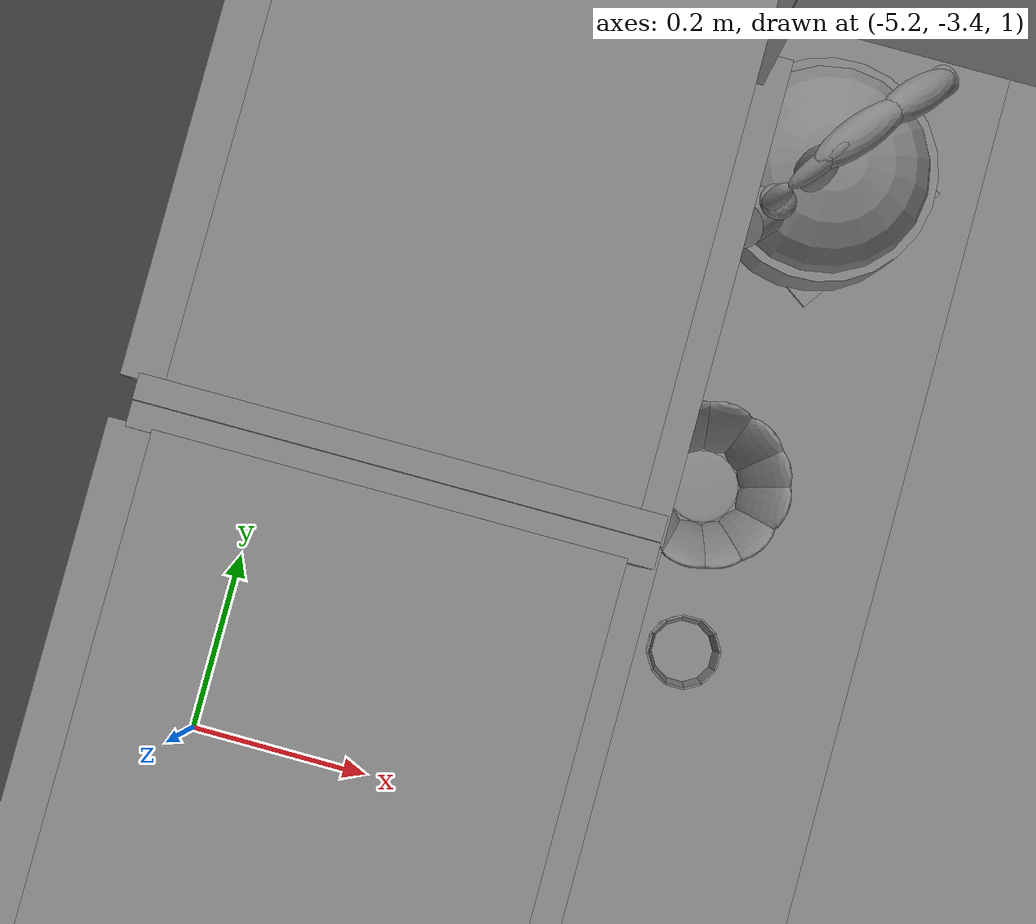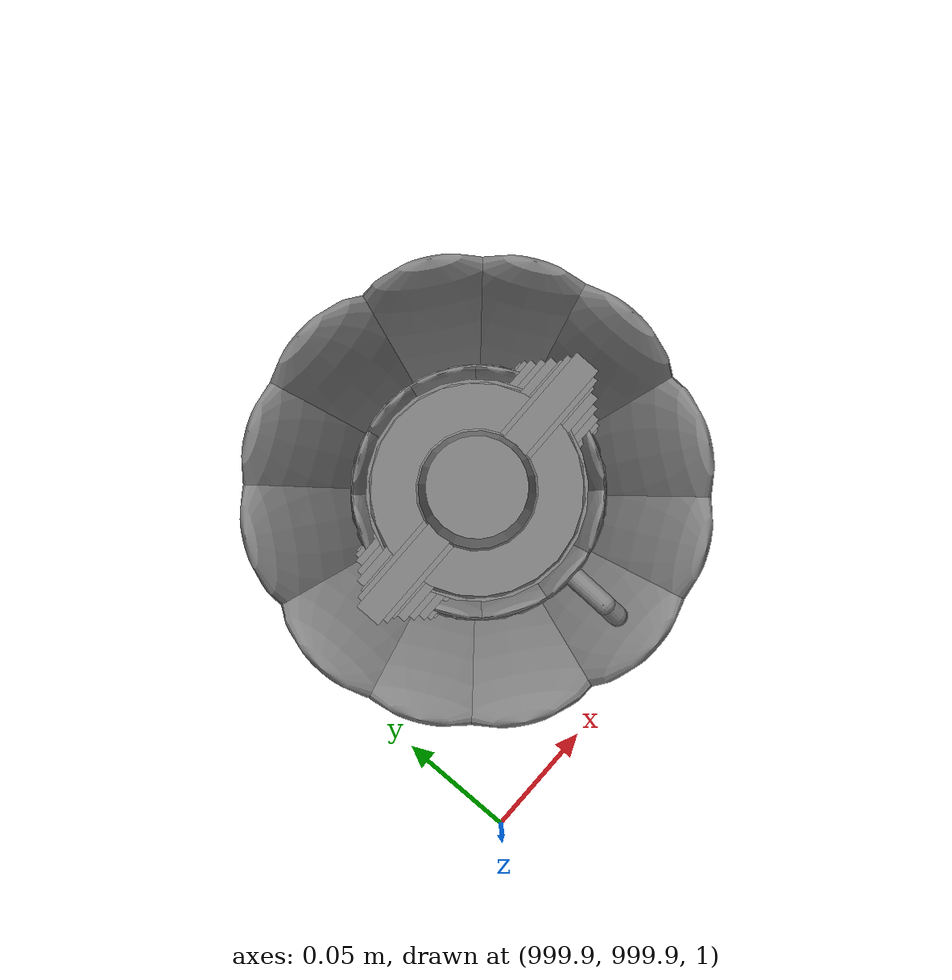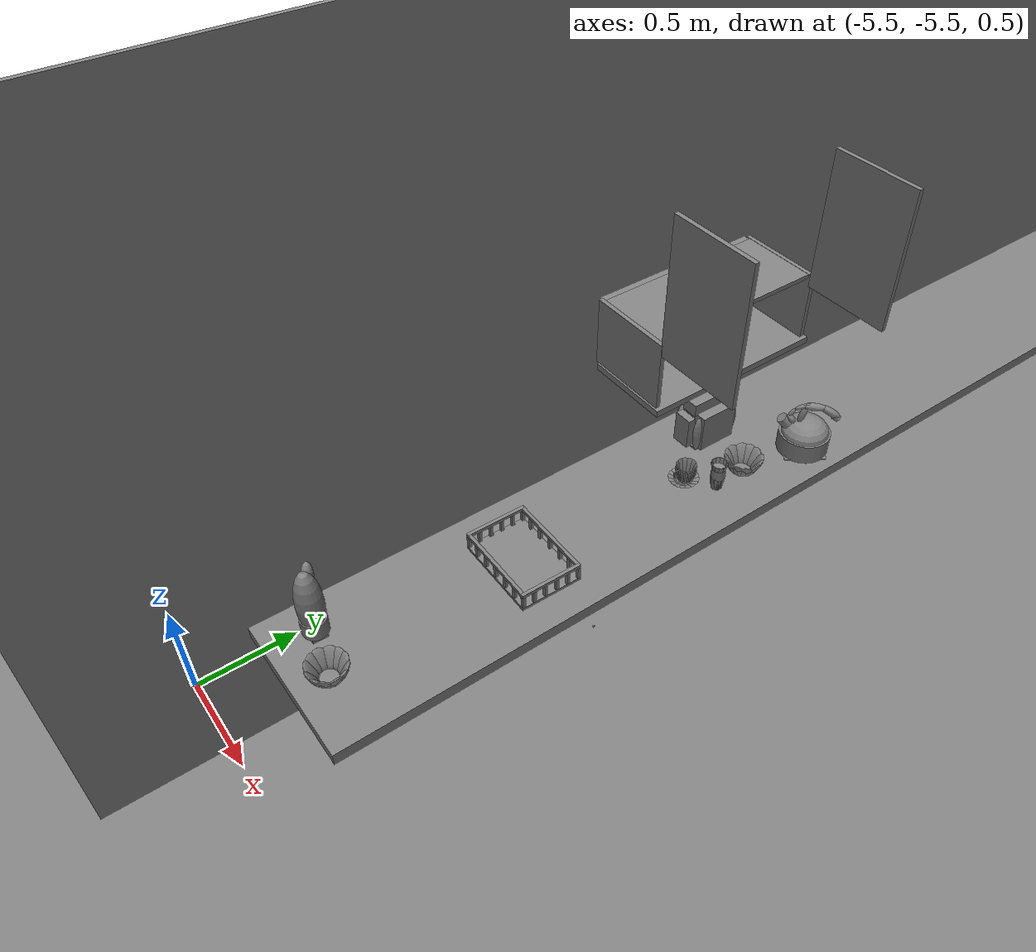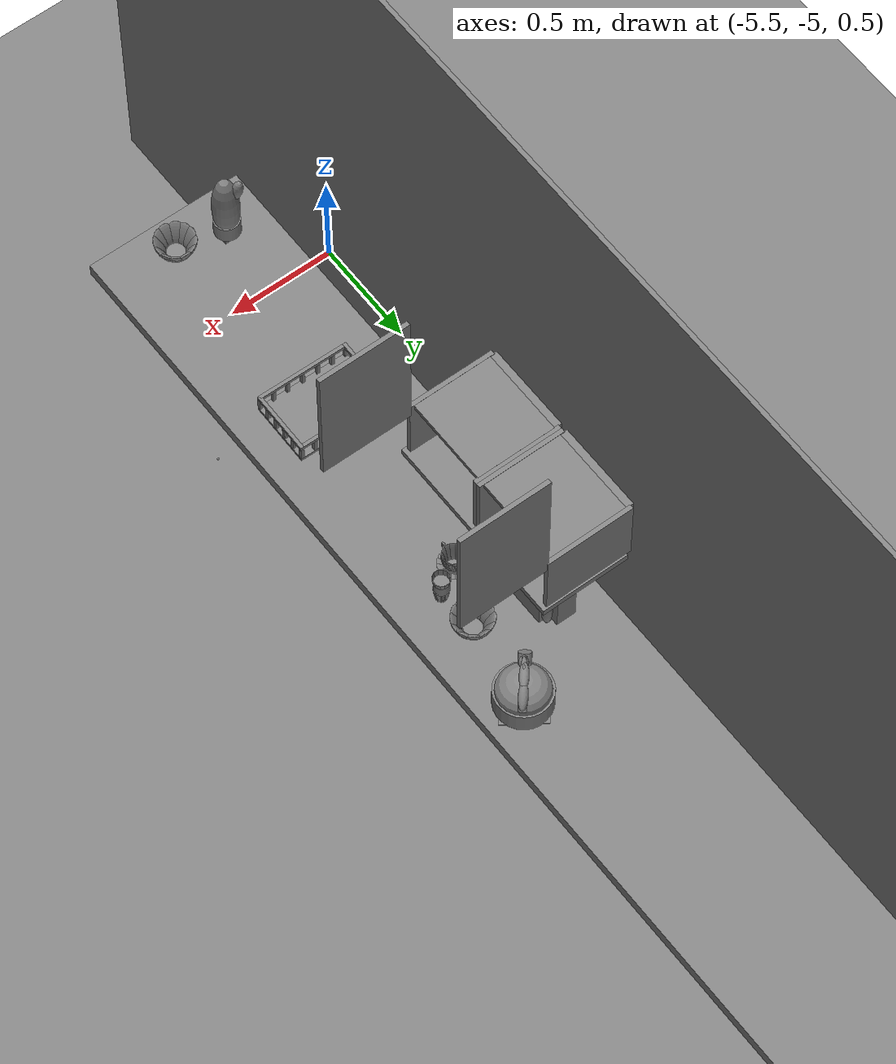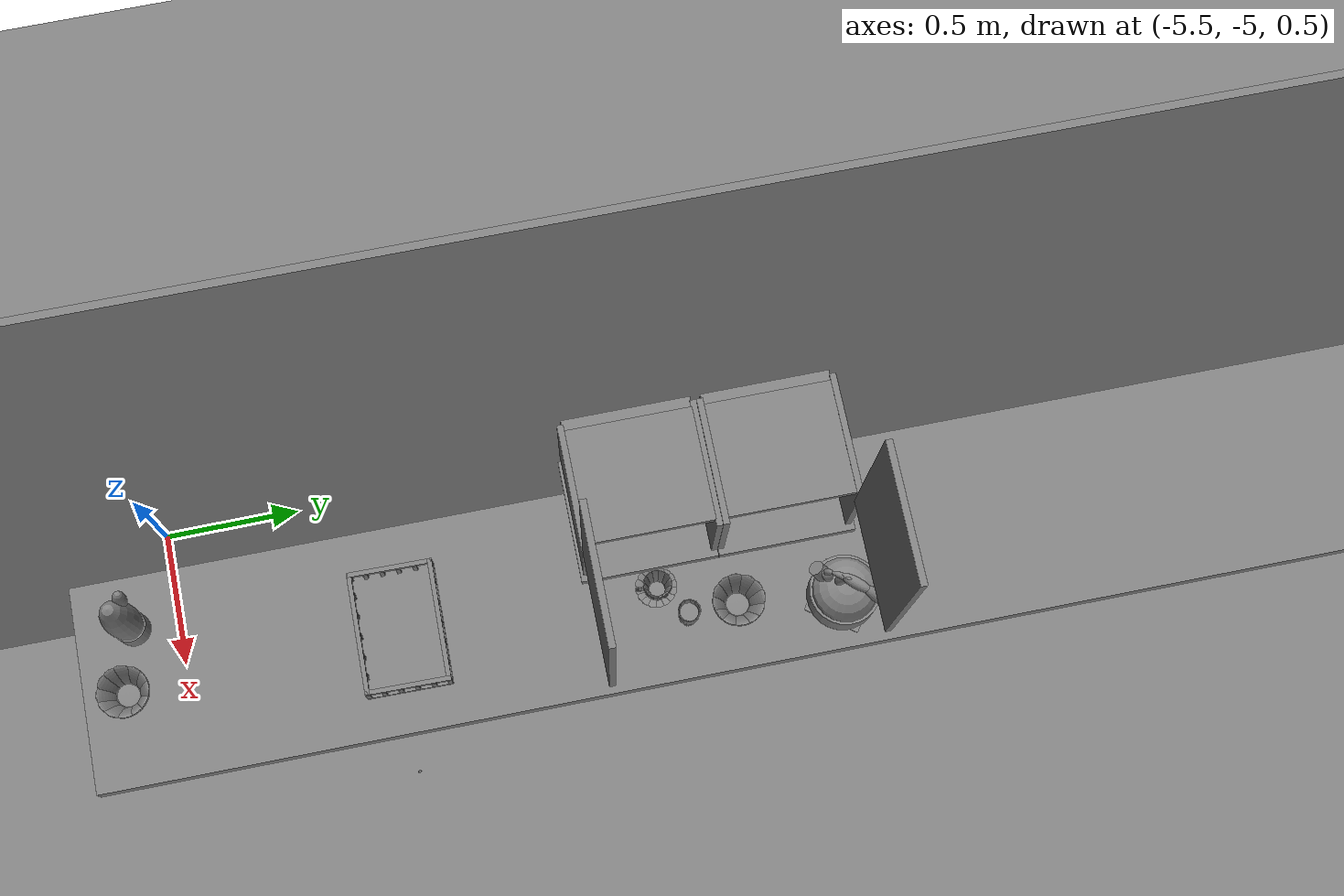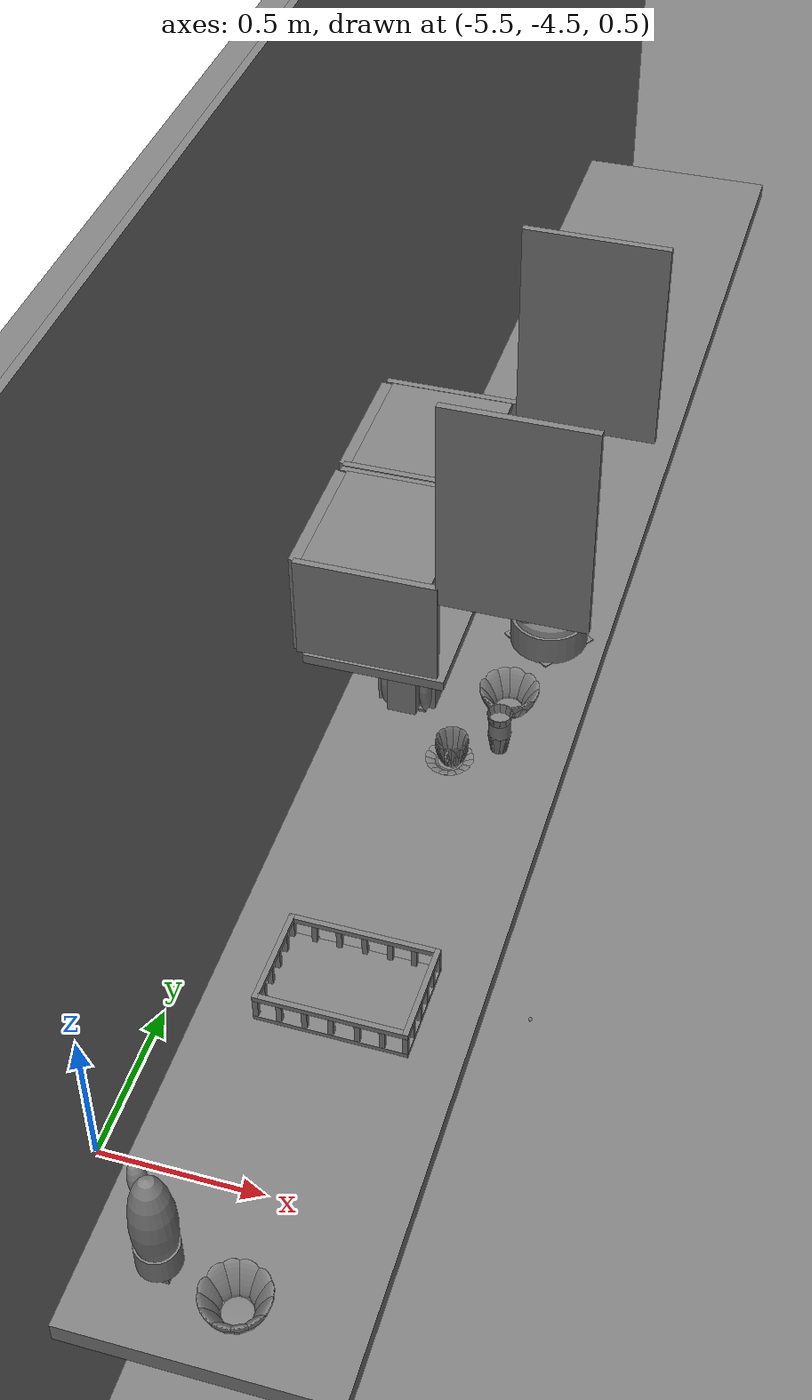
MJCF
<mujoco>
    <option gravity="0.000000000 0.000000000 -9.810000420" timestep="0.0049999999" integrator="implicitfast" density="9.8000002" viscosity="1.8000001e-05" noslip_iterations="10" iterations="100" sdf_iterations="50">
        <flag multiccd="disable"/>
    </option>
    <size memory="1000M"/>
    <compiler coordinate="local"/>
    <worldbody>
        <light cutoff="30" pos="0 1 1" dir="0 -1 -2"/>
        <light cutoff="30" pos="0 -1 1" dir="0 1 -2"/>
        <body pos="-5.046103477 -5.051773071 1.001502514" euler="0.000000000 0.000000000 0.000000000" name="Interactive Objcets_huapen">
            <geom contype="1" conaffinity="1" density="1000" type="ellipsoid" material="" rgba="0.500000000 0.500000000 0.500000000 1.000000000" solimp="0.899999976 0.949999988 0.001000000" friction="1.000000000 0.005000000 0.000100000" solref="0.020000000 1.000000000" margin="0" condim="3" group="0" pos="0.008062840 0.004346371 0.205056787" quat="1.000000000 0.000000000 0.000000000 0.000000000" size="0.059999999 0.059999999 0.180000007" name="Interactive Objcets_huapen_hua_A3A08AF8_B5DD_4EC8_B800_CA0E41552F07"/>
            <geom contype="1" conaffinity="1" density="1000" type="cylinder" material="" rgba="0.500000000 0.500000000 0.500000000 1.000000000" solimp="0.899999976 0.949999988 0.001000000" friction="1.000000000 0.005000000 0.000100000" solref="0.020000000 1.000000000" margin="0" condim="3" group="0" pos="0.008062840 0.003952026 0.080107450" quat="1.000000000 0.000000000 0.000000000 0.000000000" size="0.057999998 0.039999999 1.000000000" name="Interactive Objcets_huapen_hua_91EC4359_C884_49D3_9B93_D3CA0ACB899B"/>
            <geom contype="1" conaffinity="1" density="1000" type="box" material="" rgba="0.500000000 0.500000000 0.500000000 1.000000000" solimp="0.899999976 0.949999988 0.001000000" friction="1.000000000 0.005000000 0.000100000" solref="0.020000000 1.000000000" margin="0" condim="3" group="0" pos="0.008062840 0.003952503 0.020566106" quat="1.000000000 0.000000000 0.000000000 0.000000000" size="0.035000000 0.035000000 0.020000000" name="Interactive Objcets_huapen_hua_5EAFD96D_87C4_44F9_8DD4_D0089D5C2FE8"/>
            <geom contype="1" conaffinity="1" density="1000" type="ellipsoid" material="" rgba="0.500000000 0.500000000 0.500000000 1.000000000" solimp="0.899999976 0.949999988 0.001000000" friction="1.000000000 0.005000000 0.000100000" solref="0.020000000 1.000000000" margin="0" condim="3" group="0" pos="-0.029900074 0.033599377 0.321917295" quat="0.992658079 -0.083605267 -0.087364964 0.002748166" size="0.025000000 0.025000000 0.059999999" name="Interactive Objcets_huapen_hua_E54BA264_342E_44C7_ADC9_C64323B72680"/>
            <freejoint name="Interactive Objcets_huapen"/>
        </body>
        <body pos="-4.310908794 -3.769278765 1.810482979" euler="84.412643433 5.614285469 -169.174468994" mocap="true" name="spotlight2_SpotLight"/>
        <body pos="1000.000000000 1000.000000000 1.000000000" euler="0.000000000 0.000000000 0.000000000" name="openloong_gripper_2f85_fix_base_usda_bottle_red">
            <geom contype="1" conaffinity="1" density="1000" type="ellipsoid" material="" rgba="0.500000000 0.500000000 0.500000000 1.000000000" solimp="0.899999976 0.949999988 0.001000000" friction="1.000000000 0.005000000 0.000100000" solref="0.020000000 1.000000000" margin="0" condim="3" group="0" pos="0.000000000 0.000000000 0.144284487" quat="1.000000000 0.000000000 0.000000000 0.000000000" size="0.021000000 0.021000000 0.079999998" name="openloong_gripper_2f85_fix_base_usda_geom_4D39CCD0_BB7C_4587_A725_0F7D8A04D77E"/>
            <geom contype="1" conaffinity="1" density="1000" type="cylinder" material="" rgba="0.500000000 0.500000000 0.500000000 1.000000000" solimp="0.899999976 0.949999988 0.001000000" friction="1.000000000 0.005000000 0.000100000" solref="0.020000000 1.000000000" margin="0" condim="3" group="0" pos="0.000000000 0.000000000 0.220618963" quat="1.000000000 0.000000000 0.000000000 0.000000000" size="0.016000001 0.010000000 1.000000000" name="openloong_gripper_2f85_fix_base_usda_geom_75130BA5_E4FC_4304_8FF5_B61D22698748"/>
            <geom contype="1" conaffinity="1" density="1000" type="ellipsoid" material="" rgba="0.500000000 0.500000000 0.500000000 1.000000000" solimp="0.899999976 0.949999988 0.001000000" friction="1.000000000 0.005000000 0.000100000" solref="0.020000000 1.000000000" margin="0" condim="3" group="0" pos="0.000000000 0.000000000 0.118945479" quat="1.000000000 0.000000000 0.000000000 0.000000000" size="0.030999999 0.030999999 0.029999999" name="openloong_gripper_2f85_fix_base_usda_geom_E977D34D_3023_4EE3_946F_3325EC4D971E"/>
            <geom contype="1" conaffinity="1" density="1000" type="box" material="" rgba="0.500000000 0.500000000 0.500000000 1.000000000" solimp="0.899999976 0.949999988 0.001000000" friction="1.000000000 0.005000000 0.000100000" solref="0.020000000 1.000000000" margin="0" condim="3" group="0" pos="0.000000000 0.000000000 0.002189159" quat="1.000000000 0.000000000 0.000000000 0.000000000" size="0.020000000 0.020000000 0.003000000" name="openloong_gripper_2f85_fix_base_usda_geom_819AAC16_AE17_481F_AF77_5A8E7BB092DC"/>
            <geom contype="1" conaffinity="1" density="1000" type="cylinder" material="" rgba="0.500000000 0.500000000 0.500000000 1.000000000" solimp="0.899999976 0.949999988 0.001000000" friction="1.000000000 0.005000000 0.000100000" solref="0.020000000 1.000000000" margin="0" condim="3" group="0" pos="0.000000000 -0.000366211 0.060884237" quat="1.000000000 0.000000000 0.000000000 0.000000000" size="0.030999999 0.057999998 1.000000000" name="openloong_gripper_2f85_fix_base_usda_geom_EE6B894A_1ED7_4209_A981_C0D64F2D6D6F"/>
            <freejoint name="openloong_gripper_2f85_fix_base_usda_bottle_red_joint"/>
            <site size="0.005000000 0.005000000 0.005000000" rgba="0.500000000 0.500000000 0.500000000 1.000000000" pos="0.000000000 0.000000000 0.000000000" quat="0.999961913 0.008726535 0.000000000 0.000000000" group="0" type="sphere" name="openloong_gripper_2f85_fix_base_usda_bottle_redsite"/>
        </body>
        <body pos="-4.277421951 -4.321980000 1.743550062" euler="121.145088196 -46.370853424 137.764389038" mocap="true" name="spotlight5_SpotLight"/>
        <body pos="1000.000000000 1000.000000000 1.000000000" euler="0.000000000 0.000000000 0.000000000" name="openloong_gripper_2f85_fix_base_usda_jar_01">
            <geom contype="1" conaffinity="1" density="1000" type="box" material="" rgba="0.500000000 0.500000000 0.500000000 1.000000000" solimp="0.899999976 0.949999988 0.001000000" friction="1.000000000 0.005000000 0.000100000" solref="0.020000000 1.000000000" margin="0" condim="3" group="0" pos="0.000000000 0.000000000 0.006158113" quat="1.000000000 0.000000000 0.000000000 0.000000000" size="0.020000000 0.020000000 0.005000000" name="openloong_gripper_2f85_fix_base_usda_geom_E1A121F4_9A22_46BE_B8D0_2C42211FAED4"/>
            <geom contype="1" conaffinity="1" density="1000" type="cylinder" material="" rgba="0.500000000 0.500000000 0.500000000 1.000000000" solimp="0.899999976 0.949999988 0.001000000" friction="1.000000000 0.005000000 0.000100000" solref="0.020000000 1.000000000" margin="0" condim="3" group="0" pos="0.000000000 0.000000000 0.062744498" quat="1.000000000 0.000000000 0.000000000 0.000000000" size="0.041000001 0.052999999 1.000000000" name="openloong_gripper_2f85_fix_base_usda_geom_4E58F454_CA6B_4F32_990C_D5D415362AD3"/>
            <geom contype="1" conaffinity="1" density="1000" type="ellipsoid" material="" rgba="0.500000000 0.500000000 0.500000000 1.000000000" solimp="0.899999976 0.949999988 0.001000000" friction="1.000000000 0.005000000 0.000100000" solref="0.020000000 1.000000000" margin="0" condim="3" group="0" pos="0.000000000 0.000000000 0.122252703" quat="1.000000000 0.000000000 0.000000000 0.000000000" size="0.035999998 0.035999998 0.010000000" name="openloong_gripper_2f85_fix_base_usda_geom_3407C5DE_F561_4407_80E7_CD200D9A4C9E"/>
            <geom contype="1" conaffinity="1" density="1000" type="cylinder" material="" rgba="0.500000000 0.500000000 0.500000000 1.000000000" solimp="0.899999976 0.949999988 0.001000000" friction="1.000000000 0.005000000 0.000100000" solref="0.020000000 1.000000000" margin="0" condim="3" group="0" pos="0.000000000 0.000000000 0.015747190" quat="1.000000000 0.000000000 0.000000000 0.000000000" size="0.035000000 0.010000000 1.000000000" name="openloong_gripper_2f85_fix_base_usda_geom_3E4C92A3_574F_4BE3_8686_D959CFE3B3FA"/>
            <geom contype="1" conaffinity="1" density="1000" type="ellipsoid" material="" rgba="0.500000000 0.500000000 0.500000000 1.000000000" solimp="0.899999976 0.949999988 0.001000000" friction="1.000000000 0.005000000 0.000100000" solref="0.020000000 1.000000000" margin="0" condim="3" group="0" pos="0.000000000 0.000000000 0.115815401" quat="1.000000000 0.000000000 0.000000000 0.000000000" size="0.039999999 0.039999999 0.010000000" name="openloong_gripper_2f85_fix_base_usda_geom_26EE01A3_A541_45B3_B003_0241340A6F54"/>
            <geom contype="1" conaffinity="1" density="1000" type="cylinder" material="" rgba="0.500000000 0.500000000 0.500000000 1.000000000" solimp="0.899999976 0.949999988 0.001000000" friction="1.000000000 0.005000000 0.000100000" solref="0.020000000 1.000000000" margin="0" condim="3" group="0" pos="0.000000000 0.000000000 0.133183479" quat="1.000000000 0.000000000 0.000000000 0.000000000" size="0.037999999 0.006500000 1.000000000" name="openloong_gripper_2f85_fix_base_usda_geom_B8A4FEE4_7A15_46C7_94ED_6F1F6AC2A553"/>
            <freejoint name="openloong_gripper_2f85_fix_base_usda_jar_01_joint"/>
            <site size="0.005000000 0.005000000 0.005000000" rgba="0.500000000 0.500000000 0.500000000 1.000000000" pos="0.000000000 0.000000000 0.000000000" quat="1.000000000 0.000000000 0.000000000 0.000000000" group="0" type="sphere" name="openloong_gripper_2f85_fix_base_usda_jar_01site"/>
        </body>
        <body pos="1000.000000000 1000.000000000 1.000000000" euler="0.000000000 0.000000000 0.000000000" name="openloong_gripper_2f85_fix_base_usda_salt">
            <geom contype="1" conaffinity="1" density="1000" type="box" material="" rgba="0.500000000 0.500000000 0.500000000 1.000000000" solimp="0.899999976 0.949999988 0.001000000" friction="1.000000000 0.005000000 0.000100000" solref="0.020000000 1.000000000" margin="0" condim="3" group="0" pos="0.000305176 0.000000000 0.084862232" quat="1.000000000 0.000000000 0.000000000 0.000000000" size="0.048999999 0.018999999 0.005000000" name="openloong_gripper_2f85_fix_base_usda_geom_060BBE46_B7DE_48E7_80F1_90CE8C9406BB"/>
            <geom contype="1" conaffinity="1" density="1000" type="box" material="" rgba="0.500000000 0.500000000 0.500000000 1.000000000" solimp="0.899999976 0.949999988 0.001000000" friction="1.000000000 0.005000000 0.000100000" solref="0.020000000 1.000000000" margin="0" condim="3" group="0" pos="0.000305176 0.000000000 0.104564309" quat="1.000000000 0.000000000 0.000000000 0.000000000" size="0.052000001 0.014000000 0.005000000" name="openloong_gripper_2f85_fix_base_usda_geom_15FD32CF_A6EA_400D_A37E_DDBAD0E15015"/>
            <geom contype="1" conaffinity="1" density="1000" type="box" material="" rgba="0.500000000 0.500000000 0.500000000 1.000000000" solimp="0.899999976 0.949999988 0.001000000" friction="1.000000000 0.005000000 0.000100000" solref="0.020000000 1.000000000" margin="0" condim="3" group="0" pos="0.000305176 0.000000000 0.114487171" quat="1.000000000 0.000000000 0.000000000 0.000000000" size="0.054000001 0.011500000 0.005000000" name="openloong_gripper_2f85_fix_base_usda_geom_E95D6F75_2311_4E79_A083_49E00F0D3381"/>
            <geom contype="1" conaffinity="1" density="1000" type="box" material="" rgba="0.500000000 0.500000000 0.500000000 1.000000000" solimp="0.899999976 0.949999988 0.001000000" friction="1.000000000 0.005000000 0.000100000" solref="0.020000000 1.000000000" margin="0" condim="3" group="0" pos="0.000305176 0.000000000 0.075103164" quat="1.000000000 0.000000000 0.000000000 0.000000000" size="0.048000000 0.020000000 0.005000000" name="openloong_gripper_2f85_fix_base_usda_geom_91E6F502_7D7F_4B33_B45D_BAC621E6EADB"/>
            <geom contype="1" conaffinity="1" density="1000" type="box" material="" rgba="0.500000000 0.500000000 0.500000000 1.000000000" solimp="0.899999976 0.949999988 0.001000000" friction="1.000000000 0.005000000 0.000100000" solref="0.020000000 1.000000000" margin="0" condim="3" group="0" pos="0.000305176 0.000000000 0.134892464" quat="1.000000000 0.000000000 0.000000000 0.000000000" size="0.057000000 0.007000000 0.005000000" name="openloong_gripper_2f85_fix_base_usda_geom_28150987_2003_4AF3_B012_833DF242D7CC"/>
            <geom contype="1" conaffinity="1" density="1000" type="box" material="" rgba="0.500000000 0.500000000 0.500000000 1.000000000" solimp="0.899999976 0.949999988 0.001000000" friction="1.000000000 0.005000000 0.000100000" solref="0.020000000 1.000000000" margin="0" condim="3" group="0" pos="0.000305176 0.000000000 0.094920278" quat="1.000000000 0.000000000 0.000000000 0.000000000" size="0.050000001 0.017000001 0.005000000" name="openloong_gripper_2f85_fix_base_usda_geom_708AA4A4_A645_4CF6_8E74_484F42D62FE9"/>
            <geom contype="1" conaffinity="1" density="1000" type="box" material="" rgba="0.500000000 0.500000000 0.500000000 1.000000000" solimp="0.899999976 0.949999988 0.001000000" friction="1.000000000 0.005000000 0.000100000" solref="0.020000000 1.000000000" margin="0" condim="3" group="0" pos="0.000305176 0.000000000 0.065204859" quat="1.000000000 0.000000000 0.000000000 0.000000000" size="0.045000002 0.021000000 0.005000000" name="openloong_gripper_2f85_fix_base_usda_geom_302F1BA0_2ACA_4806_A456_985609A24D34"/>
            <geom contype="1" conaffinity="1" density="1000" type="box" material="" rgba="0.500000000 0.500000000 0.500000000 1.000000000" solimp="0.899999976 0.949999988 0.001000000" friction="1.000000000 0.005000000 0.000100000" solref="0.020000000 1.000000000" margin="0" condim="3" group="0" pos="0.000305176 0.000000000 0.144135714" quat="1.000000000 0.000000000 0.000000000 0.000000000" size="0.059000000 0.005000000 0.004000000" name="openloong_gripper_2f85_fix_base_usda_geom_6078AC5C_995D_4EEF_B1B5_34A96B048070"/>
            <geom contype="1" conaffinity="1" density="1000" type="box" material="" rgba="0.500000000 0.500000000 0.500000000 1.000000000" solimp="0.899999976 0.949999988 0.001000000" friction="1.000000000 0.005000000 0.000100000" solref="0.020000000 1.000000000" margin="0" condim="3" group="0" pos="0.000000000 0.000000000 0.031593561" quat="1.000000000 0.000000000 0.000000000 0.000000000" size="0.041999999 0.024000000 0.029999999" name="openloong_gripper_2f85_fix_base_usda_geom_C2E862BA_F750_4704_9C43_3E11B0FF1D47"/>
            <geom contype="1" conaffinity="1" density="1000" type="box" material="" rgba="0.500000000 0.500000000 0.500000000 1.000000000" solimp="0.899999976 0.949999988 0.001000000" friction="1.000000000 0.005000000 0.000100000" solref="0.020000000 1.000000000" margin="0" condim="3" group="0" pos="0.000305176 0.000000000 0.124608755" quat="1.000000000 0.000000000 0.000000000 0.000000000" size="0.055000000 0.008000000 0.005000000" name="openloong_gripper_2f85_fix_base_usda_geom_7B8A935B_542B_4BE9_8C06_A9B3ABF965D6"/>
            <freejoint name="openloong_gripper_2f85_fix_base_usda_salt_joint"/>
            <site size="0.005000000 0.005000000 0.005000000" rgba="0.500000000 0.500000000 0.500000000 1.000000000" pos="0.000000000 0.000000000 0.000000000" quat="1.000000000 0.000000000 0.000000000 0.000000000" group="0" type="sphere" name="openloong_gripper_2f85_fix_base_usda_saltsite"/>
        </body>
        <body pos="1000.000000000 1000.000000000 1.000000000" euler="0.000000000 0.000000000 0.000000000" name="openloong_gripper_2f85_fix_base_usda_bow_yellow_kps">
            <geom contype="1" conaffinity="1" density="1000" type="ellipsoid" material="" rgba="0.500000000 0.500000000 0.500000000 1.000000000" solimp="0.899999976 0.949999988 0.001000000" friction="1.000000000 0.005000000 0.000100000" solref="0.020000000 1.000000000" margin="0" condim="3" group="0" pos="-0.052185059 0.040283203 0.044118762" quat="0.919264615 -0.076883033 -0.225593656 -0.313287765" size="0.010000000 0.039999999 0.052000001" name="openloong_gripper_2f85_fix_base_usda_geom_293A681E_069C_48A4_8AA4_D30F04630D0B"/>
            <geom contype="1" conaffinity="1" density="1000" type="ellipsoid" material="" rgba="0.500000000 0.500000000 0.500000000 1.000000000" solimp="0.899999976 0.949999988 0.001000000" friction="1.000000000 0.005000000 0.000100000" solref="0.020000000 1.000000000" margin="0" condim="3" group="0" pos="-0.000061035 0.065979004 0.044118762" quat="0.687598765 -0.168314874 -0.168741167 -0.685860336" size="0.010000000 0.039999999 0.052000001" name="openloong_gripper_2f85_fix_base_usda_geom_1762CC68_6E7F_40B1_8778_8A1601CD7518"/>
            <geom contype="1" conaffinity="1" density="1000" type="box" material="" rgba="0.500000000 0.500000000 0.500000000 1.000000000" solimp="0.899999976 0.949999988 0.001000000" friction="1.000000000 0.005000000 0.000100000" solref="0.020000000 1.000000000" margin="0" condim="3" group="0" pos="0.000061035 0.000000000 -0.002001643" quat="1.000000000 0.000000000 0.000000000 0.000000000" size="0.029999999 0.029999999 0.002000000" name="openloong_gripper_2f85_fix_base_usda_geom_2EE175A7_B50B_4849_8D73_C8D31F8A8090"/>
            <geom contype="1" conaffinity="1" density="1000" type="ellipsoid" material="" rgba="0.500000000 0.500000000 0.500000000 1.000000000" solimp="0.899999976 0.949999988 0.001000000" friction="1.000000000 0.005000000 0.000100000" solref="0.020000000 1.000000000" margin="0" condim="3" group="0" pos="0.029418945 -0.059082031 0.044118762" quat="0.825555861 0.125530601 0.202597082 -0.511521280" size="0.010000000 0.039999999 0.052000001" name="openloong_gripper_2f85_fix_base_usda_geom_5790566B_7E3F_4CC7_AF54_C104EB02D382"/>
            <geom contype="1" conaffinity="1" density="1000" type="ellipsoid" material="" rgba="0.500000000 0.500000000 0.500000000 1.000000000" solimp="0.899999976 0.949999988 0.001000000" friction="1.000000000 0.005000000 0.000100000" solref="0.020000000 1.000000000" margin="0" condim="3" group="0" pos="0.000244141 -0.065979004 0.044118762" quat="0.687598765 0.168314651 0.168741375 -0.685860336" size="0.010000000 0.039999999 0.052000001" name="openloong_gripper_2f85_fix_base_usda_geom_BFB51CB4_F3BA_4018_88C8_5619FD0553B3"/>
            <geom contype="1" conaffinity="1" density="1000" type="ellipsoid" material="" rgba="0.500000000 0.500000000 0.500000000 1.000000000" solimp="0.899999976 0.949999988 0.001000000" friction="1.000000000 0.005000000 0.000100000" solref="0.020000000 1.000000000" margin="0" condim="3" group="0" pos="0.000061035 0.000000000 0.000446677" quat="1.000000000 0.000000000 0.000000000 0.000000000" size="0.039999999 0.039999999 0.002000000" name="openloong_gripper_2f85_fix_base_usda_geom_B14260EE_D6E9_489F_BE5E_AE16CA973521"/>
            <geom contype="1" conaffinity="1" density="1000" type="ellipsoid" material="" rgba="0.500000000 0.500000000 0.500000000 1.000000000" solimp="0.899999976 0.949999988 0.001000000" friction="1.000000000 0.005000000 0.000100000" solref="0.020000000 1.000000000" margin="0" condim="3" group="0" pos="0.059082031 0.029541016 0.044118762" quat="0.223252773 -0.231952220 -0.054787423 -0.945174456" size="0.010000000 0.039999999 0.052000001" name="openloong_gripper_2f85_fix_base_usda_geom_2D61F3E5_34BA_46F0_9418_411938ECC6EF"/>
            <geom contype="1" conaffinity="1" density="1000" type="ellipsoid" material="" rgba="0.500000000 0.500000000 0.500000000 1.000000000" solimp="0.899999976 0.949999988 0.001000000" friction="1.000000000 0.005000000 0.000100000" solref="0.020000000 1.000000000" margin="0" condim="3" group="0" pos="0.000061035 0.000000000 0.007335305" quat="1.000000000 0.000000000 0.000000000 0.000000000" size="0.039999999 0.039999999 0.002000000" name="openloong_gripper_2f85_fix_base_usda_geom_E5EE3705_1422_4A40_9FBA_BE21938E431B"/>
            <geom contype="1" conaffinity="1" density="1000" type="ellipsoid" material="" rgba="0.500000000 0.500000000 0.500000000 1.000000000" solimp="0.899999976 0.949999988 0.001000000" friction="1.000000000 0.005000000 0.000100000" solref="0.020000000 1.000000000" margin="0" condim="3" group="0" pos="-0.029296875 0.059082031 0.044118762" quat="0.825555861 -0.125530809 -0.202596918 -0.511521280" size="0.010000000 0.039999999 0.052000001" name="openloong_gripper_2f85_fix_base_usda_geom_8F8FCF8A_E92A_441B_9AD9_0E2348EDBC4B"/>
            <geom contype="1" conaffinity="1" density="1000" type="ellipsoid" material="" rgba="0.500000000 0.500000000 0.500000000 1.000000000" solimp="0.899999976 0.949999988 0.001000000" friction="1.000000000 0.005000000 0.000100000" solref="0.020000000 1.000000000" margin="0" condim="3" group="0" pos="0.040222168 0.052368164 0.044118762" quat="0.429593176 -0.213750049 -0.105424821 -0.871002972" size="0.010000000 0.039999999 0.052000001" name="openloong_gripper_2f85_fix_base_usda_geom_14610DAC_A384_4378_80ED_B7D7C791CCC5"/>
            <geom contype="1" conaffinity="1" density="1000" type="ellipsoid" material="" rgba="0.500000000 0.500000000 0.500000000 1.000000000" solimp="0.899999976 0.949999988 0.001000000" friction="1.000000000 0.005000000 0.000100000" solref="0.020000000 1.000000000" margin="0" condim="3" group="0" pos="0.066040039 0.000000000 0.044118762" quat="0.971183062 -0.000000156 0.238334835 0.000000030" size="0.010000000 0.039999999 0.052000001" name="openloong_gripper_2f85_fix_base_usda_geom_5FDD5F93_73E8_45F8_A203_9608C8E47839"/>
            <geom contype="1" conaffinity="1" density="1000" type="ellipsoid" material="" rgba="0.500000000 0.500000000 0.500000000 1.000000000" solimp="0.899999976 0.949999988 0.001000000" friction="1.000000000 0.005000000 0.000100000" solref="0.020000000 1.000000000" margin="0" condim="3" group="0" pos="0.052307129 -0.040283203 0.044118762" quat="0.919264674 0.076882750 0.225593731 -0.313287705" size="0.010000000 0.039999999 0.052000001" name="openloong_gripper_2f85_fix_base_usda_geom_64E284E4_B8CA_4026_A26C_2F903F2CE1DC"/>
            <geom contype="1" conaffinity="1" density="1000" type="ellipsoid" material="" rgba="0.500000000 0.500000000 0.500000000 1.000000000" solimp="0.899999976 0.949999988 0.001000000" friction="1.000000000 0.005000000 0.000100000" solref="0.020000000 1.000000000" margin="0" condim="3" group="0" pos="-0.065917969 0.000000000 0.044118762" quat="0.971183062 -0.000000142 -0.238334835 0.000000030" size="0.010000000 0.039999999 0.052000001" name="openloong_gripper_2f85_fix_base_usda_geom_839CDAF4_6836_4BE2_958C_0232B67B52AF"/>
            <geom contype="1" conaffinity="1" density="1000" type="ellipsoid" material="" rgba="0.500000000 0.500000000 0.500000000 1.000000000" solimp="0.899999976 0.949999988 0.001000000" friction="1.000000000 0.005000000 0.000100000" solref="0.020000000 1.000000000" margin="0" condim="3" group="0" pos="-0.058898926 -0.029541016 0.044118762" quat="0.223252758 0.231952101 0.054787733 -0.945174575" size="0.010000000 0.039999999 0.052000001" name="openloong_gripper_2f85_fix_base_usda_geom_8C7DB3A2_2CCB_4068_813B_72DEEE323685"/>
            <geom contype="1" conaffinity="1" density="1000" type="ellipsoid" material="" rgba="0.500000000 0.500000000 0.500000000 1.000000000" solimp="0.899999976 0.949999988 0.001000000" friction="1.000000000 0.005000000 0.000100000" solref="0.020000000 1.000000000" margin="0" condim="3" group="0" pos="-0.040100098 -0.052368164 0.044118762" quat="0.429593235 0.213749886 0.105425082 -0.871003032" size="0.010000000 0.039999999 0.052000001" name="openloong_gripper_2f85_fix_base_usda_geom_2A40151B_5302_409B_A283_A7F804E2A259"/>
            <freejoint name="openloong_gripper_2f85_fix_base_usda_bow_yellow_kps_joint"/>
            <site size="0.005000000 0.005000000 0.005000000" rgba="0.500000000 0.500000000 0.500000000 1.000000000" pos="0.000000000 0.000000000 0.000000000" quat="0.999961913 0.008726534 0.000000000 0.000000000" group="0" type="sphere" name="openloong_gripper_2f85_fix_base_usda_bow_yellow_kps"/>
        </body>
        <body pos="1000.000000000 1000.000000000 1.000000000" euler="0.000000000 0.000000000 0.000000000" name="openloong_gripper_2f85_fix_base_usda_coffeecup_white_kps">
            <geom contype="1" conaffinity="1" density="1000" type="capsule" material="" rgba="0.500000000 0.500000000 0.500000000 1.000000000" solimp="0.899999976 0.949999988 0.001000000" friction="1.000000000 0.005000000 0.000100000" solref="0.020000000 1.000000000" margin="0" condim="3" group="0" pos="-0.000854492 -0.065795898 0.050029993" quat="0.343559504 -0.613204718 0.626912475 0.336047262" size="0.004000000 0.005000000 1.000000000" name="openloong_gripper_2f85_fix_base_usda_geom_A56A92C3_96EB_4EEF_937F_30FF57686D04"/>
            <geom contype="1" conaffinity="1" density="1000" type="ellipsoid" material="" rgba="0.500000000 0.500000000 0.500000000 1.000000000" solimp="0.899999976 0.949999988 0.001000000" friction="1.000000000 0.005000000 0.000100000" solref="0.020000000 1.000000000" margin="0" condim="3" group="0" pos="-0.000793457 -0.038452148 0.048040152" quat="0.711656272 0.066323131 -0.067805752 0.696095467" size="0.005000000 0.029999999 0.048999999" name="openloong_gripper_2f85_fix_base_usda_geom_3D6B5D22_FD08_409C_BF9F_08054E8AAF85"/>
            <geom contype="1" conaffinity="1" density="1000" type="ellipsoid" material="" rgba="0.500000000 0.500000000 0.500000000 1.000000000" solimp="0.899999976 0.949999988 0.001000000" friction="1.000000000 0.005000000 0.000100000" solref="0.020000000 1.000000000" margin="0" condim="3" group="0" pos="0.037719727 -0.001892090 0.048040152" quat="0.995387912 0.001371633 0.094835162 -0.014391154" size="0.005000000 0.029999999 0.048999999" name="openloong_gripper_2f85_fix_base_usda_geom_308781F1_448B_4602_937E_BCFD1B8E8F64"/>
            <geom contype="1" conaffinity="1" density="1000" type="ellipsoid" material="" rgba="0.500000000 0.500000000 0.500000000 1.000000000" solimp="0.899999976 0.949999988 0.001000000" friction="1.000000000 0.005000000 0.000100000" solref="0.020000000 1.000000000" margin="0" condim="3" group="0" pos="0.033996582 0.015502930 0.048040152" quat="0.970659733 -0.021051638 0.092478797 0.220962167" size="0.005000000 0.029999999 0.048999999" name="openloong_gripper_2f85_fix_base_usda_geom_87C4CF95_7D80_46C9_B049_E8CD6E4E9B5E"/>
            <geom contype="1" conaffinity="1" density="1000" type="box" material="" rgba="0.500000000 0.500000000 0.500000000 1.000000000" solimp="0.899999976 0.949999988 0.001000000" friction="1.000000000 0.005000000 0.000100000" solref="0.020000000 1.000000000" margin="0" condim="3" group="0" pos="0.000793457 -0.000183105 0.000156164" quat="0.714879215 0.000000000 0.000000000 0.699247897" size="0.020000000 0.020000000 0.002000000" name="openloong_gripper_2f85_fix_base_usda_geom_D9B467D9_95BA_45D9_8B54_E1F2125A2203"/>
            <geom contype="1" conaffinity="1" density="1000" type="ellipsoid" material="" rgba="0.500000000 0.500000000 0.500000000 1.000000000" solimp="0.899999976 0.949999988 0.001000000" friction="1.000000000 0.005000000 0.000100000" solref="0.020000000 1.000000000" margin="0" condim="3" group="0" pos="-0.019409180 -0.033081055 0.048040152" quat="0.866879702 0.046630561 -0.082595348 0.489411235" size="0.005000000 0.029999999 0.048999999" name="openloong_gripper_2f85_fix_base_usda_geom_1892FBA1_95E9_4DA1_83B4_F5A0FD031778"/>
            <geom contype="1" conaffinity="1" density="1000" type="ellipsoid" material="" rgba="0.500000000 0.500000000 0.500000000 1.000000000" solimp="0.899999976 0.949999988 0.001000000" friction="1.000000000 0.005000000 0.000100000" solref="0.020000000 1.000000000" margin="0" condim="3" group="0" pos="-0.016052246 0.033264160 0.048040152" quat="0.840792537 -0.050782297 -0.080109790 -0.532983541" size="0.005000000 0.029999999 0.048999999" name="openloong_gripper_2f85_fix_base_usda_geom_5077A702_E81E_4F11_A4DC_504EB06CEA7A"/>
            <geom contype="1" conaffinity="1" density="1000" type="capsule" material="" rgba="0.500000000 0.500000000 0.500000000 1.000000000" solimp="0.899999976 0.949999988 0.001000000" friction="1.000000000 0.005000000 0.000100000" solref="0.020000000 1.000000000" margin="0" condim="3" group="0" pos="-0.000549316 -0.053527832 0.046825886" quat="0.505496025 -0.494442940 0.505495846 0.494442940" size="0.004000000 0.005000000 1.000000000" name="openloong_gripper_2f85_fix_base_usda_geom_D14516B4_9640_4AB0_A8C0_2043E11DCAE1"/>
            <geom contype="1" conaffinity="1" density="1000" type="ellipsoid" material="" rgba="0.500000000 0.500000000 0.500000000 1.000000000" solimp="0.899999976 0.949999988 0.001000000" friction="1.000000000 0.005000000 0.000100000" solref="0.020000000 1.000000000" margin="0" condim="3" group="0" pos="-0.032104492 0.018920898 0.048040152" quat="0.958129764 -0.025742561 -0.091288343 -0.270168930" size="0.005000000 0.029999999 0.048999999" name="openloong_gripper_2f85_fix_base_usda_geom_7700191C_A7D2_4F1E_9D04_BE58E2138434"/>
            <geom contype="1" conaffinity="1" density="1000" type="ellipsoid" material="" rgba="0.500000000 0.500000000 0.500000000 1.000000000" solimp="0.899999976 0.949999988 0.001000000" friction="1.000000000 0.005000000 0.000100000" solref="0.020000000 1.000000000" margin="0" condim="3" group="0" pos="-0.037597656 0.000305176 0.048040152" quat="0.995387554 -0.001371440 -0.094839431 -0.014389008" size="0.005000000 0.029999999 0.048999999" name="openloong_gripper_2f85_fix_base_usda_geom_7E91BC41_5A95_483A_ACAC_A4A1F9932BE7"/>
            <geom contype="1" conaffinity="1" density="1000" type="capsule" material="" rgba="0.500000000 0.500000000 0.500000000 1.000000000" solimp="0.899999976 0.949999988 0.001000000" friction="1.000000000 0.005000000 0.000100000" solref="0.020000000 1.000000000" margin="0" condim="3" group="0" pos="-0.000366211 -0.043762207 0.044118762" quat="0.260488123 -0.651174724 0.665731549 0.254792154" size="0.004000000 0.003000000 1.000000000" name="openloong_gripper_2f85_fix_base_usda_geom_A39B66DB_5AC7_44E2_AA8D_AE9F4B38C651"/>
            <geom contype="1" conaffinity="1" density="1000" type="capsule" material="" rgba="0.500000000 0.500000000 0.500000000 1.000000000" solimp="0.899999976 0.949999988 0.001000000" friction="1.000000000 0.005000000 0.000100000" solref="0.020000000 1.000000000" margin="0" condim="3" group="0" pos="-0.000915527 -0.068542480 0.082936406" quat="0.624995589 -0.339446366 0.347034454 0.611329615" size="0.004000000 0.004000000 1.000000000" name="openloong_gripper_2f85_fix_base_usda_geom_6E88F863_E8BA_455E_BDF8_94CC440ACEA5"/>
            <geom contype="1" conaffinity="1" density="1000" type="ellipsoid" material="" rgba="0.500000000 0.500000000 0.500000000 1.000000000" solimp="0.899999976 0.949999988 0.001000000" friction="1.000000000 0.005000000 0.000100000" solref="0.020000000 1.000000000" margin="0" condim="3" group="0" pos="0.016113281 -0.034851074 0.048040152" quat="0.840793252 0.050779939 0.080106191 -0.532983422" size="0.005000000 0.029999999 0.048999999" name="openloong_gripper_2f85_fix_base_usda_geom_8128A632_29E8_433E_A0C2_5C8FB37D4805"/>
            <geom contype="1" conaffinity="1" density="1000" type="ellipsoid" material="" rgba="0.500000000 0.500000000 0.500000000 1.000000000" solimp="0.899999976 0.949999988 0.001000000" friction="1.000000000 0.005000000 0.000100000" solref="0.020000000 1.000000000" margin="0" condim="3" group="0" pos="0.000854492 0.036865234 0.048040152" quat="0.711656570 -0.066320375 0.067802906 0.696095705" size="0.005000000 0.029999999 0.048999999" name="openloong_gripper_2f85_fix_base_usda_geom_EC70B0E8_E66D_4249_AAB7_ADEBDB31A093"/>
            <geom contype="1" conaffinity="1" density="1000" type="ellipsoid" material="" rgba="0.500000000 0.500000000 0.500000000 1.000000000" solimp="0.899999976 0.949999988 0.001000000" friction="1.000000000 0.005000000 0.000100000" solref="0.020000000 1.000000000" margin="0" condim="3" group="0" pos="-0.033935547 -0.017089844 0.048040152" quat="0.970659137 0.021052625 -0.092483103 0.220962465" size="0.005000000 0.029999999 0.048999999" name="openloong_gripper_2f85_fix_base_usda_geom_95842273_BD36_4FC8_9550_138556FFC35F"/>
            <geom contype="1" conaffinity="1" density="1000" type="ellipsoid" material="" rgba="0.500000000 0.500000000 0.500000000 1.000000000" solimp="0.899999976 0.949999988 0.001000000" friction="1.000000000 0.005000000 0.000100000" solref="0.020000000 1.000000000" margin="0" condim="3" group="0" pos="0.019531250 0.031494141 0.048040152" quat="0.866880119 -0.046628602 0.082591817 0.489411235" size="0.005000000 0.029999999 0.048999999" name="openloong_gripper_2f85_fix_base_usda_geom_0B4BDB12_5364_4687_A7F5_9DC4FA0D0F44"/>
            <geom contype="1" conaffinity="1" density="1000" type="ellipsoid" material="" rgba="0.500000000 0.500000000 0.500000000 1.000000000" solimp="0.899999976 0.949999988 0.001000000" friction="1.000000000 0.005000000 0.000100000" solref="0.020000000 1.000000000" margin="0" condim="3" group="0" pos="0.032165527 -0.020507812 0.048040152" quat="0.958128154 0.025740955 0.091285400 -0.270175666" size="0.005000000 0.029999999 0.048999999" name="openloong_gripper_2f85_fix_base_usda_geom_53E9927B_A0E2_4D70_BA5D_50C5364C29D4"/>
            <geom contype="1" conaffinity="1" density="1000" type="capsule" material="" rgba="0.500000000 0.500000000 0.500000000 1.000000000" solimp="0.899999976 0.949999988 0.001000000" friction="1.000000000 0.005000000 0.000100000" solref="0.020000000 1.000000000" margin="0" condim="3" group="0" pos="-0.000610352 -0.056823730 0.083572865" quat="0.452654332 -0.541215360 0.553313971 0.442756712" size="0.004000000 0.009000000 1.000000000" name="openloong_gripper_2f85_fix_base_usda_geom_7B1E5FE6_8A91_4665_A349_2CD608B47B18"/>
            <geom contype="1" conaffinity="1" density="1000" type="ellipsoid" material="" rgba="0.500000000 0.500000000 0.500000000 1.000000000" solimp="0.899999976 0.949999988 0.001000000" friction="1.000000000 0.005000000 0.000100000" solref="0.020000000 1.000000000" margin="0" condim="3" group="0" pos="0.000061035 -0.000183105 0.001848221" quat="0.714879215 0.000000000 0.000000000 0.699247897" size="0.029999999 0.029999999 0.001000000" name="openloong_gripper_2f85_fix_base_usda_geom_F0043C85_31E3_4B97_BEA3_E60E633CF714"/>
            <geom contype="1" conaffinity="1" density="1000" type="capsule" material="" rgba="0.500000000 0.500000000 0.500000000 1.000000000" solimp="0.899999976 0.949999988 0.001000000" friction="1.000000000 0.005000000 0.000100000" solref="0.020000000 1.000000000" margin="0" condim="3" group="0" pos="-0.000976562 -0.071838379 0.066101432" quat="0.031849027 -0.698553741 0.714169443 0.031152546" size="0.004000000 0.012000000 1.000000000" name="openloong_gripper_2f85_fix_base_usda_geom_E628FE1E_AC3E_4CFE_996B_9DCCDD3973ED"/>
            <freejoint name="openloong_gripper_2f85_fix_base_usda_coffeecup_white_kps_joint"/>
            <site size="0.005000000 0.005000000 0.005000000" rgba="0.500000000 0.500000000 0.500000000 1.000000000" pos="0.000000000 0.000000000 0.000000000" quat="0.999961913 0.008726534 0.000000000 0.000000000" group="0" type="sphere" name="openloong_gripper_2f85_fix_base_usda_coffeecup_white_kps"/>
        </body>
        <body pos="-4.146216869 -4.184763908 1.728762031" euler="59.640388489 -79.845222473 -115.731002808" mocap="true" name="spotlight4_SpotLight"/>
        <body pos="0.000000000 0.000000000 0.000000000" euler="0.000000000 0.000000000 0.000000000" name="Static Objcets_Static Objcets">
            <geom contype="1" conaffinity="1" density="1000" type="box" material="" rgba="0.500000000 0.500000000 0.500000000 1.000000000" solimp="0.899999976 0.949999988 0.001000000" friction="1.000000000 0.005000000 0.000100000" solref="0.020000000 1.000000000" margin="0" condim="3" group="0" pos="-4.999745846 -3.497932911 1.764780521" quat="0.707107067 0.707106471 0.000000000 0.000000000" size="0.200000003 0.159999996 0.010000000" name="Static Objcets_geom_208272ED_58BC_4CC5_912C_1715C925A640"/>
            <geom contype="1" conaffinity="1" density="1000" type="box" material="" rgba="0.500000000 0.500000000 0.500000000 1.000000000" solimp="0.899999976 0.949999988 0.001000000" friction="1.000000000 0.005000000 0.000100000" solref="0.020000000 1.000000000" margin="0" condim="3" group="0" pos="-4.979488373 -3.297635794 1.591412544" quat="0.707106829 0.707106709 0.000000000 0.000000000" size="0.200000003 0.015000000 0.219999999" name="Static Objcets_geom_E423448A_1E69_47DD_9E87_A0894F885695"/>
            <geom contype="1" conaffinity="1" density="1000" type="box" material="" rgba="0.500000000 0.500000000 0.500000000 1.000000000" solimp="0.899999976 0.949999988 0.001000000" friction="1.000000000 0.005000000 0.000100000" solref="0.020000000 1.000000000" margin="0" condim="3" group="0" pos="-4.999745846 -3.087441683 1.763863802" quat="0.707107067 0.707106471 0.000000000 0.000000000" size="0.200000003 0.159999996 0.010000000" name="Static Objcets_geom_368B6128_C964_4D66_A718_6255F58B0DE0"/>
            <geom contype="1" conaffinity="1" density="1000" type="box" material="" rgba="0.500000000 0.500000000 0.500000000 1.000000000" solimp="0.899999976 0.949999988 0.001000000" friction="1.000000000 0.005000000 0.000100000" solref="0.020000000 1.000000000" margin="0" condim="3" group="0" pos="-5.189302921 -3.293644905 1.760152459" quat="0.707107067 0.707106471 0.000000000 0.000000000" size="0.025000000 0.159999996 0.200000003" name="Static Objcets_geom_38000060_A462_4BBA_93D8_AE66E2D9ACBA"/>
            <geom contype="1" conaffinity="1" density="1000" type="box" material="" rgba="0.500000000 0.500000000 0.500000000 1.000000000" solimp="0.899999976 0.949999988 0.001000000" friction="1.000000000 0.005000000 0.000100000" solref="0.020000000 1.000000000" margin="0" condim="3" group="0" pos="-5.000125408 -3.294431210 1.913951039" quat="0.707107067 0.707106471 0.000000000 0.000000000" size="0.180000007 0.010000000 0.200000003" name="Static Objcets_geom_69B342F3_149C_4BE3_8492_B3DD0BA15766"/>
            <geom contype="1" conaffinity="1" density="1000" type="box" material="" rgba="0.500000000 0.500000000 0.500000000 1.000000000" solimp="0.899999976 0.949999988 0.001000000" friction="1.000000000 0.005000000 0.000100000" solref="0.020000000 1.000000000" margin="0" condim="3" group="0" pos="-5.000125408 -2.861802340 1.913950682" quat="0.707107067 0.707106471 0.000000000 0.000000000" size="0.180000007 0.010000000 0.200000003" name="Static Objcets_geom_2FCB921C_34F0_44C1_8F81_1E9483F3DAB7"/>
            <geom contype="1" conaffinity="1" density="1000" type="box" material="" rgba="0.500000000 0.500000000 0.500000000 1.000000000" solimp="0.899999976 0.949999988 0.001000000" friction="1.000000000 0.005000000 0.000100000" solref="0.020000000 1.000000000" margin="0" condim="3" group="0" pos="-4.979488373 -2.855390549 1.591412187" quat="0.707106709 0.707106769 0.000000000 0.000000000" size="0.200000003 0.015000000 0.219999999" name="Static Objcets_geom_E0318635_33C6_49D1_9820_836B28CEBAB9"/>
            <geom contype="1" conaffinity="1" density="1000" type="box" material="" rgba="0.500000000 0.500000000 0.500000000 1.000000000" solimp="0.899999976 0.949999988 0.001000000" friction="1.000000000 0.005000000 0.000100000" solref="0.020000000 1.000000000" margin="0" condim="3" group="0" pos="-4.999745846 -3.066934109 1.765979409" quat="0.707107067 0.707106471 0.000000000 0.000000000" size="0.200000003 0.159999996 0.010000000" name="Static Objcets_geom_F449132B_8B2D_4869_A7EE_BB3137204AC6"/>
            <geom contype="1" conaffinity="1" density="1000" type="box" material="" rgba="0.500000000 0.500000000 0.500000000 1.000000000" solimp="0.899999976 0.949999988 0.001000000" friction="1.000000000 0.005000000 0.000100000" solref="0.020000000 1.000000000" margin="0" condim="3" group="0" pos="-4.999745846 -2.653569937 1.764779806" quat="0.707107067 0.707106471 0.000000000 0.000000000" size="0.200000003 0.159999996 0.010000000" name="Static Objcets_geom_39C579AE_8B76_4095_B493_455137C5989B"/>
            <geom contype="1" conaffinity="1" density="1000" type="box" material="" rgba="0.500000000 0.500000000 0.500000000 1.000000000" solimp="0.899999976 0.949999988 0.001000000" friction="1.000000000 0.005000000 0.000100000" solref="0.020000000 1.000000000" margin="0" condim="3" group="0" pos="-5.189302921 -2.861564636 1.760152102" quat="0.707107067 0.707106471 0.000000000 0.000000000" size="0.025000000 0.159999996 0.200000003" name="Static Objcets_geom_529EC615_55FB_427D_8A63_FEA3BCD91813"/>
            <geom contype="1" conaffinity="1" density="1000" type="box" material="" rgba="0.500000000 0.500000000 0.500000000 1.000000000" solimp="0.899999976 0.949999988 0.001000000" friction="1.000000000 0.005000000 0.000100000" solref="0.020000000 1.000000000" margin="0" condim="3" group="0" pos="-4.873187065 -2.461376429 0.977675021" quat="0.707107067 0.707106471 0.000000000 0.000000000" size="0.370000005 0.029999999 2.799999952" name="Static Objcets_geom_A6652468_4B0D_4CFA_B7D0_BD1EAF20FD1A"/>
            <geom contype="1" conaffinity="1" density="1000" type="box" material="" rgba="0.500000000 0.500000000 0.500000000 1.000000000" solimp="0.899999976 0.949999988 0.001000000" friction="1.000000000 0.005000000 0.000100000" solref="0.020000000 1.000000000" margin="0" condim="3" group="0" pos="-5.244853973 -2.375543594 1.820221663" quat="0.707107008 0.707106531 0.000000000 0.000000000" size="0.010000000 1.500000000 3.700000048" name="Static Objcets_geom_28A4DF82_6695_4C82_9EF9_E5EC41722972"/>
            <geom contype="1" conaffinity="1" density="1000" type="box" material="" rgba="0.500000000 0.500000000 0.500000000 1.000000000" solimp="0.899999976 0.949999988 0.001000000" friction="1.000000000 0.005000000 0.000100000" solref="0.020000000 1.000000000" margin="0" condim="3" group="0" pos="-0.720102787 0.222944975 -1.102830648" quat="0.000000954 1.000000000 0.000000000 0.000000000" size="8.000000000 8.000000000 0.010000000" name="Static Objcets_geom_266F7D25_C3E5_47F1_B4E2_4569A3579A9B"/>
        </body>
        <body pos="-4.685121059 -2.618872881 1.139834642" euler="-89.999885559 -75.046211243 -179.999633789" name="Interactive Objcets_shuihu">
            <geom contype="1" conaffinity="1" density="1000" type="ellipsoid" material="" rgba="0.500000000 0.500000000 0.500000000 1.000000000" solimp="0.899999976 0.949999988 0.001000000" friction="1.000000000 0.005000000 0.000100000" solref="0.020000000 1.000000000" margin="0" condim="3" group="0" pos="0.031587839 0.066336274 0.011863232" quat="0.813834965 -0.098448642 0.568551302 0.068776846" size="0.020000000 0.059999999 0.015000000" name="Interactive Objcets_geom_B5574343_3321_4A67_9291_1D7CB3A702DF"/>
            <geom contype="1" conaffinity="1" density="1000" type="cylinder" material="" rgba="0.500000000 0.500000000 0.500000000 1.000000000" solimp="0.899999976 0.949999988 0.001000000" friction="1.000000000 0.005000000 0.000100000" solref="0.020000000 1.000000000" margin="0" condim="3" group="0" pos="0.097564876 0.019223809 0.042538166" quat="0.757945418 -0.330064029 0.507527351 0.242883876" size="0.027000001 0.032499999 1.000000000" name="Interactive Objcets_geom_97EBA00B_D674_4ECA_B474_76FA86285251"/>
            <geom contype="1" conaffinity="1" density="1000" type="ellipsoid" material="" rgba="0.500000000 0.500000000 0.500000000 1.000000000" solimp="0.899999976 0.949999988 0.001000000" friction="1.000000000 0.005000000 0.000100000" solref="0.020000000 1.000000000" margin="0" condim="3" group="0" pos="0.079775751 0.074323297 0.032407284" quat="0.807211578 -0.212389767 0.536951303 0.122406662" size="0.011000000 0.029999999 0.010000000" name="Interactive Objcets_geom_E42C4930_0D02_4DBC_B46D_B12007C3D928"/>
            <geom contype="1" conaffinity="1" density="1000" type="cylinder" material="" rgba="0.500000000 0.500000000 0.500000000 1.000000000" solimp="0.899999976 0.949999988 0.001000000" friction="1.000000000 0.005000000 0.000100000" solref="0.020000000 1.000000000" margin="0" condim="3" group="0" pos="0.006719470 -0.083229184 -0.000185013" quat="0.579664290 -0.579662681 0.404957741 0.404956520" size="0.123000003 0.050000001 1.000000000" name="Interactive Objcets_geom_1808D0CA_2928_4EB7_9B0E_C2C7544C1D13"/>
            <geom contype="1" conaffinity="1" density="1000" type="cylinder" material="" rgba="0.500000000 0.500000000 0.500000000 1.000000000" solimp="0.899999976 0.949999988 0.001000000" friction="1.000000000 0.005000000 0.000100000" solref="0.020000000 1.000000000" margin="0" condim="3" group="0" pos="-0.109747589 0.061178923 -0.054180622" quat="0.791120291 -0.252390862 0.522301614 0.193980843" size="0.017000001 0.015000000 1.000000000" name="Interactive Objcets_geom_05AB6069_EC27_40D3_8E15_73D29DADE65D"/>
            <geom contype="1" conaffinity="1" density="1000" type="ellipsoid" material="" rgba="0.500000000 0.500000000 0.500000000 1.000000000" solimp="0.899999976 0.949999988 0.001000000" friction="1.000000000 0.005000000 0.000100000" solref="0.020000000 1.000000000" margin="0" condim="3" group="0" pos="-0.012925148 0.115441918 -0.008463383" quat="0.573223114 -0.617213011 0.363985062 0.397464871" size="0.020000000 0.059999999 0.017999999" name="Interactive Objcets_geom_8CD62B99_C725_4D94_B1C5_85E1AEBDBF93"/>
            <geom contype="1" conaffinity="1" density="1000" type="ellipsoid" material="" rgba="0.500000000 0.500000000 0.500000000 1.000000000" solimp="0.899999976 0.949999988 0.001000000" friction="1.000000000 0.005000000 0.000100000" solref="0.020000000 1.000000000" margin="0" condim="3" group="0" pos="0.076839805 0.041928887 0.028444767" quat="0.777403057 0.260122687 0.543099582 -0.181723833" size="0.020000000 0.029999999 0.015000000" name="Interactive Objcets_geom_F4A7D56E_A7DF_4BE4_A18A_3C37F6044E22"/>
            <geom contype="1" conaffinity="1" density="1000" type="ellipsoid" material="" rgba="0.500000000 0.500000000 0.500000000 1.000000000" solimp="0.899999976 0.949999988 0.001000000" friction="1.000000000 0.005000000 0.000100000" solref="0.020000000 1.000000000" margin="0" condim="3" group="0" pos="-0.081469536 0.090929627 -0.040654182" quat="0.423473954 -0.728255510 0.250199795 0.477193654" size="0.020000000 0.059999999 0.017999999" name="Interactive Objcets_geom_CD63E814_A0B2_4838_9C15_83BDEA94066F"/>
            <geom contype="1" conaffinity="1" density="1000" type="ellipsoid" material="" rgba="0.500000000 0.500000000 0.500000000 1.000000000" solimp="0.899999976 0.949999988 0.001000000" friction="1.000000000 0.005000000 0.000100000" solref="0.020000000 1.000000000" margin="0" condim="3" group="0" pos="0.036164403 0.116219044 0.012343884" quat="0.691036344 -0.468154669 0.465933800 0.293608427" size="0.011000000 0.039999999 0.010000000" name="Interactive Objcets_geom_FE7CDAD9_7CF1_4AFB_B1C2_87E29602C3E9"/>
            <geom contype="1" conaffinity="1" density="1000" type="box" material="" rgba="0.500000000 0.500000000 0.500000000 1.000000000" solimp="0.899999976 0.949999988 0.001000000" friction="1.000000000 0.005000000 0.000100000" solref="0.020000000 1.000000000" margin="0" condim="3" group="0" pos="0.006720424 -0.132364750 -0.000183582" quat="0.579664230 -0.579662681 0.404957652 0.404956520" size="0.100000001 0.100000001 0.005000000" name="Interactive Objcets_geom_C520E61E_FD3F_4BC9_8775_32D863929A37"/>
            <geom contype="1" conaffinity="1" density="1000" type="ellipsoid" material="" rgba="0.500000000 0.500000000 0.500000000 1.000000000" solimp="0.899999976 0.949999988 0.001000000" friction="1.000000000 0.005000000 0.000100000" solref="0.020000000 1.000000000" margin="0" condim="3" group="0" pos="0.006307602 -0.038442492 -0.000561237" quat="0.579664290 -0.579662681 0.404957741 0.404956520" size="0.115000002 0.115000002 0.079999998" name="Interactive Objcets_geom_810193D2_9173_477B_B5F9_C321199E53C9"/>
            <freejoint name="Interactive Objcets_shuihu"/>
        </body>
        <body pos="-4.821335316 -5.105734825 1.007418752" euler="0.000000000 0.000000000 89.999946594" name="Interactive Objcets_bow_04">
            <geom contype="1" conaffinity="1" density="1000" type="ellipsoid" material="" rgba="0.500000000 0.500000000 0.500000000 1.000000000" solimp="0.899999976 0.949999988 0.001000000" friction="1.000000000 0.005000000 0.000100000" solref="0.020000000 1.000000000" margin="0" condim="3" group="0" pos="-0.000090122 0.065967083 0.044118762" quat="0.687598825 -0.168314755 -0.168741047 -0.685860395" size="0.010000000 0.039999999 0.052000001" name="Interactive Objcets_geom_479CB939_7385_4F01_A82E_63B9017469B5"/>
            <geom contype="1" conaffinity="1" density="1000" type="ellipsoid" material="" rgba="0.500000000 0.500000000 0.500000000 1.000000000" solimp="0.899999976 0.949999988 0.001000000" friction="1.000000000 0.005000000 0.000100000" solref="0.020000000 1.000000000" margin="0" condim="3" group="0" pos="-0.040080309 -0.052354813 0.044118762" quat="0.429593146 0.213749856 0.105425127 -0.871003032" size="0.010000000 0.039999999 0.052000001" name="Interactive Objcets_geom_8320698A_C878_4E9B_A4DB_1C5912AA7BF8"/>
            <geom contype="1" conaffinity="1" density="1000" type="ellipsoid" material="" rgba="0.500000000 0.500000000 0.500000000 1.000000000" solimp="0.899999976 0.949999988 0.001000000" friction="1.000000000 0.005000000 0.000100000" solref="0.020000000 1.000000000" margin="0" condim="3" group="0" pos="-0.029293537 0.059069157 0.044118762" quat="0.825556040 -0.125530839 -0.202596709 -0.511521041" size="0.010000000 0.039999999 0.052000001" name="Interactive Objcets_geom_A0E04936_469A_42EF_9AFF_FCBD3B4EED74"/>
            <geom contype="1" conaffinity="1" density="1000" type="ellipsoid" material="" rgba="0.500000000 0.500000000 0.500000000 1.000000000" solimp="0.899999976 0.949999988 0.001000000" friction="1.000000000 0.005000000 0.000100000" solref="0.020000000 1.000000000" margin="0" condim="3" group="0" pos="-0.065898657 -0.000007629 0.044118762" quat="0.971183062 -0.000000142 -0.238334835 0.000000030" size="0.010000000 0.039999999 0.052000001" name="Interactive Objcets_geom_B406034C_60E2_4558_B664_4332D3392F73"/>
            <geom contype="1" conaffinity="1" density="1000" type="ellipsoid" material="" rgba="0.500000000 0.500000000 0.500000000 1.000000000" solimp="0.899999976 0.949999988 0.001000000" friction="1.000000000 0.005000000 0.000100000" solref="0.020000000 1.000000000" margin="0" condim="3" group="0" pos="0.000082970 0.000000000 0.000446677" quat="1.000000000 0.000000000 0.000000000 0.000000000" size="0.039999999 0.039999999 0.002000000" name="Interactive Objcets_geom_3E845ED2_2420_4D0F_B932_5294B3F91031"/>
            <geom contype="1" conaffinity="1" density="1000" type="ellipsoid" material="" rgba="0.500000000 0.500000000 0.500000000 1.000000000" solimp="0.899999976 0.949999988 0.001000000" friction="1.000000000 0.005000000 0.000100000" solref="0.020000000 1.000000000" margin="0" condim="3" group="0" pos="0.000243664 -0.065983295 0.044118762" quat="0.687598884 0.168314576 0.168741226 -0.685860336" size="0.010000000 0.039999999 0.052000001" name="Interactive Objcets_geom_49E86A38_8191_4BA4_ADE7_C1B9630919FF"/>
            <geom contype="1" conaffinity="1" density="1000" type="ellipsoid" material="" rgba="0.500000000 0.500000000 0.500000000 1.000000000" solimp="0.899999976 0.949999988 0.001000000" friction="1.000000000 0.005000000 0.000100000" solref="0.020000000 1.000000000" margin="0" condim="3" group="0" pos="0.000082970 0.000000000 0.003118873" quat="1.000000000 0.000000000 0.000000000 0.000000000" size="0.039999999 0.039999999 0.002000000" name="Interactive Objcets_geom_8795682E_A00F_40B3_A3C0_7BA91FD93411"/>
            <geom contype="1" conaffinity="1" density="1000" type="ellipsoid" material="" rgba="0.500000000 0.500000000 0.500000000 1.000000000" solimp="0.899999976 0.949999988 0.001000000" friction="1.000000000 0.005000000 0.000100000" solref="0.020000000 1.000000000" margin="0" condim="3" group="0" pos="0.040234327 0.052339077 0.044118762" quat="0.429593533 -0.213750005 -0.105424747 -0.871002972" size="0.010000000 0.039999999 0.052000001" name="Interactive Objcets_geom_4D98E9F2_7C53_44F6_96DC_D14D40B6FB95"/>
            <geom contype="1" conaffinity="1" density="1000" type="ellipsoid" material="" rgba="0.500000000 0.500000000 0.500000000 1.000000000" solimp="0.899999976 0.949999988 0.001000000" friction="1.000000000 0.005000000 0.000100000" solref="0.020000000 1.000000000" margin="0" condim="3" group="0" pos="0.066051960 -0.000007629 0.044118762" quat="0.971183062 -0.000000156 0.238334835 0.000000030" size="0.010000000 0.039999999 0.052000001" name="Interactive Objcets_geom_B19F09A8_8CE1_4648_9E3E_ED3B73C45C23"/>
            <geom contype="1" conaffinity="1" density="1000" type="ellipsoid" material="" rgba="0.500000000 0.500000000 0.500000000 1.000000000" solimp="0.899999976 0.949999988 0.001000000" friction="1.000000000 0.005000000 0.000100000" solref="0.020000000 1.000000000" margin="0" condim="3" group="0" pos="-0.058925867 -0.029528618 0.044118762" quat="0.223252863 0.231952116 0.054787725 -0.945174456" size="0.010000000 0.039999999 0.052000001" name="Interactive Objcets_geom_F25C76B0_78DB_481E_A459_7FDCAD1B321D"/>
            <geom contype="1" conaffinity="1" density="1000" type="ellipsoid" material="" rgba="0.500000000 0.500000000 0.500000000 1.000000000" solimp="0.899999976 0.949999988 0.001000000" friction="1.000000000 0.005000000 0.000100000" solref="0.020000000 1.000000000" margin="0" condim="3" group="0" pos="0.029448032 -0.059085369 0.044118762" quat="0.825555801 0.125530601 0.202597082 -0.511521280" size="0.010000000 0.039999999 0.052000001" name="Interactive Objcets_geom_38589CBE_24D0_43E8_AFF7_694363396ACC"/>
            <geom contype="1" conaffinity="1" density="1000" type="ellipsoid" material="" rgba="0.500000000 0.500000000 0.500000000 1.000000000" solimp="0.899999976 0.949999988 0.001000000" friction="1.000000000 0.005000000 0.000100000" solref="0.020000000 1.000000000" margin="0" condim="3" group="0" pos="0.059080124 0.029511929 0.044118762" quat="0.223252952 -0.231952190 -0.054787360 -0.945174456" size="0.010000000 0.039999999 0.052000001" name="Interactive Objcets_geom_3027F588_F1A7_47ED_9CAE_5BD5EADDB29D"/>
            <geom contype="1" conaffinity="1" density="1000" type="ellipsoid" material="" rgba="0.500000000 0.500000000 0.500000000 1.000000000" solimp="0.899999976 0.949999988 0.001000000" friction="1.000000000 0.005000000 0.000100000" solref="0.020000000 1.000000000" margin="0" condim="3" group="0" pos="-0.052167892 0.040281773 0.044118762" quat="0.919264615 -0.076883025 -0.225593626 -0.313287735" size="0.010000000 0.039999999 0.052000001" name="Interactive Objcets_geom_D3C4C328_F5D5_443A_8C35_48C0DCD52DF0"/>
            <geom contype="1" conaffinity="1" density="1000" type="ellipsoid" material="" rgba="0.500000000 0.500000000 0.500000000 1.000000000" solimp="0.899999976 0.949999988 0.001000000" friction="1.000000000 0.005000000 0.000100000" solref="0.020000000 1.000000000" margin="0" condim="3" group="0" pos="0.052321672 -0.040297985 0.044118762" quat="0.919264674 0.076882720 0.225593746 -0.313287675" size="0.010000000 0.039999999 0.052000001" name="Interactive Objcets_geom_1ADF9949_D6D0_4E76_AED7_1FDF9E480DB6"/>
            <freejoint name="Interactive Objcets_bow_04"/>
        </body>
        <body pos="-4.835184574 -3.254794121 1.033557892" euler="0.000000000 0.000000000 0.000000000" name="Interactive Objcets_cupplate_01">
            <geom contype="1" conaffinity="1" density="1000" type="ellipsoid" material="" rgba="0.500000000 0.500000000 0.500000000 1.000000000" solimp="0.899999976 0.949999988 0.001000000" friction="1.000000000 0.005000000 0.000100000" solref="0.020000000 1.000000000" margin="0" condim="3" group="0" pos="0.052457333 0.022318602 0.000154614" quat="0.165263638 -0.548659503 -0.111679509 -0.811904132" size="0.002000000 0.020000000 0.017000001" name="Interactive Objcets_geom_F191FEAA_79B3_4E99_9A9A_CBF0CA3A5973"/>
            <geom contype="1" conaffinity="1" density="1000" type="ellipsoid" material="" rgba="0.500000000 0.500000000 0.500000000 1.000000000" solimp="0.899999976 0.949999988 0.001000000" friction="1.000000000 0.005000000 0.000100000" solref="0.020000000 1.000000000" margin="0" condim="3" group="0" pos="0.000000000 0.000000000 -0.007192612" quat="1.000000000 0.000000000 0.000000000 0.000000000" size="0.039999999 0.039999999 0.001000000" name="Interactive Objcets_geom_E43F437B_765F_447B_9F46_E5776AA3BAFF"/>
            <geom contype="1" conaffinity="1" density="1000" type="ellipsoid" material="" rgba="0.500000000 0.500000000 0.500000000 1.000000000" solimp="0.899999976 0.949999988 0.001000000" friction="1.000000000 0.005000000 0.000100000" solref="0.020000000 1.000000000" margin="0" condim="3" group="0" pos="0.022432804 0.052464008 0.000154614" quat="0.455865860 -0.467545629 -0.308059722 -0.691871881" size="0.002000000 0.020000000 0.017000001" name="Interactive Objcets_geom_F0FA7A1A_4AE2_4483_BE77_35520B89DF25"/>
            <geom contype="1" conaffinity="1" density="1000" type="ellipsoid" material="" rgba="0.500000000 0.500000000 0.500000000 1.000000000" solimp="0.899999976 0.949999988 0.001000000" friction="1.000000000 0.005000000 0.000100000" solref="0.020000000 1.000000000" margin="0" condim="3" group="0" pos="-0.052522659 0.022613287 0.000154614" quat="0.811438143 -0.113215551 -0.548344791 -0.167535841" size="0.002000000 0.020000000 0.017000001" name="Interactive Objcets_geom_E7E7822D_C37E_4291_BDF7_8A21ED7B1A81"/>
            <geom contype="1" conaffinity="1" density="1000" type="ellipsoid" material="" rgba="0.500000000 0.500000000 0.500000000 1.000000000" solimp="0.899999976 0.949999988 0.001000000" friction="1.000000000 0.005000000 0.000100000" solref="0.020000000 1.000000000" margin="0" condim="3" group="0" pos="0.057000160 0.000000477 0.000000000" quat="0.828553081 0.000000000 0.559910476 0.000000000" size="0.002000000 0.020000000 0.017000001" name="Interactive Objcets_geom_34D944AF_446B_43A0_9769_62B82D589B1E"/>
            <geom contype="1" conaffinity="1" density="1000" type="ellipsoid" material="" rgba="0.500000000 0.500000000 0.500000000 1.000000000" solimp="0.899999976 0.949999988 0.001000000" friction="1.000000000 0.005000000 0.000100000" solref="0.020000000 1.000000000" margin="0" condim="3" group="0" pos="-0.039110661 0.041686535 0.000154614" quat="0.760133922 -0.222795680 -0.513674736 -0.329691947" size="0.002000000 0.020000000 0.017000001" name="Interactive Objcets_geom_4F5F56EE_8711_4574_B7AB_91A1A7A30F06"/>
            <geom contype="1" conaffinity="1" density="1000" type="ellipsoid" material="" rgba="0.500000000 0.500000000 0.500000000 1.000000000" solimp="0.899999976 0.949999988 0.001000000" friction="1.000000000 0.005000000 0.000100000" solref="0.020000000 1.000000000" margin="0" condim="3" group="0" pos="-0.041719437 -0.039082766 0.000000000" quat="0.304989874 0.520597219 0.206102297 -0.770377457" size="0.002000000 0.020000000 0.017000001" name="Interactive Objcets_geom_52561D9D_BA84_48E2_A259_9687CFCC3310"/>
            <geom contype="1" conaffinity="1" density="1000" type="ellipsoid" material="" rgba="0.500000000 0.500000000 0.500000000 1.000000000" solimp="0.899999976 0.949999988 0.001000000" friction="1.000000000 0.005000000 0.000100000" solref="0.020000000 1.000000000" margin="0" condim="3" group="0" pos="-0.000003815 -0.057095528 0.000000000" quat="0.586347640 0.395597160 0.396235406 -0.585402966" size="0.002000000 0.020000000 0.017000001" name="Interactive Objcets_geom_FADA14DA_646D_4926_9723_F83D94EC5D93"/>
            <geom contype="1" conaffinity="1" density="1000" type="ellipsoid" material="" rgba="0.500000000 0.500000000 0.500000000 1.000000000" solimp="0.899999976 0.949999988 0.001000000" friction="1.000000000 0.005000000 0.000100000" solref="0.020000000 1.000000000" margin="0" condim="3" group="0" pos="0.041527748 0.039082766 0.000154614" quat="0.304989874 -0.520597219 -0.206102297 -0.770377457" size="0.002000000 0.020000000 0.017000001" name="Interactive Objcets_geom_C814F3EA_E3BF_4268_826E_C1D1FC765C22"/>
            <geom contype="1" conaffinity="1" density="1000" type="ellipsoid" material="" rgba="0.500000000 0.500000000 0.500000000 1.000000000" solimp="0.899999976 0.949999988 0.001000000" friction="1.000000000 0.005000000 0.000100000" solref="0.020000000 1.000000000" margin="0" condim="3" group="0" pos="0.022139072 -0.052588940 0.000000119" quat="0.690592766 0.309367865 0.466681093 -0.457801163" size="0.002000000 0.020000000 0.017000001" name="Interactive Objcets_geom_F752A165_8724_4A48_A41F_0A5770DFF358"/>
            <geom contype="1" conaffinity="1" density="1000" type="ellipsoid" material="" rgba="0.500000000 0.500000000 0.500000000 1.000000000" solimp="0.899999976 0.949999988 0.001000000" friction="1.000000000 0.005000000 0.000100000" solref="0.020000000 1.000000000" margin="0" condim="3" group="0" pos="-0.057191849 0.000000477 0.000154614" quat="0.828553081 0.000000000 -0.559910476 0.000000000" size="0.002000000 0.020000000 0.017000001" name="Interactive Objcets_geom_400BE2E0_5770_4182_8B8A_D5E2F9CAA6CF"/>
            <geom contype="1" conaffinity="1" density="1000" type="ellipsoid" material="" rgba="0.500000000 0.500000000 0.500000000 1.000000000" solimp="0.899999976 0.949999988 0.001000000" friction="1.000000000 0.005000000 0.000100000" solref="0.020000000 1.000000000" margin="0" condim="3" group="0" pos="-0.052649021 -0.022319317 0.000000119" quat="0.165263638 0.548659503 0.111679509 -0.811904132" size="0.002000000 0.020000000 0.017000001" name="Interactive Objcets_geom_7ABC6CD8_67B9_4F11_B42D_DEE57A7FF7DD"/>
            <geom contype="1" conaffinity="1" density="1000" type="ellipsoid" material="" rgba="0.500000000 0.500000000 0.500000000 1.000000000" solimp="0.899999976 0.949999988 0.001000000" friction="1.000000000 0.005000000 0.000100000" solref="0.020000000 1.000000000" margin="0" condim="3" group="0" pos="0.038919926 -0.041685820 0.000000000" quat="0.760133922 0.222795680 0.513674736 -0.329691947" size="0.002000000 0.020000000 0.017000001" name="Interactive Objcets_geom_26A40DF7_EC71_4ADC_9CC4_DB6DB6C43C15"/>
            <geom contype="1" conaffinity="1" density="1000" type="ellipsoid" material="" rgba="0.500000000 0.500000000 0.500000000 1.000000000" solimp="0.899999976 0.949999988 0.001000000" friction="1.000000000 0.005000000 0.000100000" solref="0.020000000 1.000000000" margin="0" condim="3" group="0" pos="-0.000187874 0.057096481 0.000154614" quat="0.586347640 -0.395597160 -0.396235406 -0.585402966" size="0.002000000 0.020000000 0.017000001" name="Interactive Objcets_geom_9AE2C8FA_84EE_4FF7_9DFE_482A0283C22A"/>
            <geom contype="1" conaffinity="1" density="1000" type="ellipsoid" material="" rgba="0.500000000 0.500000000 0.500000000 1.000000000" solimp="0.899999976 0.949999988 0.001000000" friction="1.000000000 0.005000000 0.000100000" solref="0.020000000 1.000000000" margin="0" condim="3" group="0" pos="0.052331448 -0.022612572 0.000000000" quat="0.811438143 0.113215551 0.548344791 -0.167535841" size="0.002000000 0.020000000 0.017000001" name="Interactive Objcets_geom_AF072AD1_3861_4991_98BA_F68D5F5C98C0"/>
            <geom contype="1" conaffinity="1" density="1000" type="ellipsoid" material="" rgba="0.500000000 0.500000000 0.500000000 1.000000000" solimp="0.899999976 0.949999988 0.001000000" friction="1.000000000 0.005000000 0.000100000" solref="0.020000000 1.000000000" margin="0" condim="3" group="0" pos="0.000000000 0.000000000 -0.006308794" quat="1.000000000 0.000000000 0.000000000 0.000000000" size="0.035000000 0.035000000 0.001000000" name="Interactive Objcets_geom_6D5BFE00_F42E_408A_8FAD_788A222E837E"/>
            <geom contype="1" conaffinity="1" density="1000" type="ellipsoid" material="" rgba="0.500000000 0.500000000 0.500000000 1.000000000" solimp="0.899999976 0.949999988 0.001000000" friction="1.000000000 0.005000000 0.000100000" solref="0.020000000 1.000000000" margin="0" condim="3" group="0" pos="-0.022624493 -0.052463770 0.000000000" quat="0.455865860 0.467545629 0.308059722 -0.691871881" size="0.002000000 0.020000000 0.017000001" name="Interactive Objcets_geom_2804DE33_B6F3_462D_94CB_A0A560E87544"/>
            <geom contype="1" conaffinity="1" density="1000" type="ellipsoid" material="" rgba="0.500000000 0.500000000 0.500000000 1.000000000" solimp="0.899999976 0.949999988 0.001000000" friction="1.000000000 0.005000000 0.000100000" solref="0.020000000 1.000000000" margin="0" condim="3" group="0" pos="-0.022329807 0.052588463 0.000154614" quat="0.690592766 -0.309367865 -0.466681093 -0.457801163" size="0.002000000 0.020000000 0.017000001" name="Interactive Objcets_geom_9D7E753F_450F_4BFE_88F8_6F7928D193DB"/>
            <freejoint name="Interactive Objcets_cupplate_01"/>
        </body>
        <body pos="-5.020127296 -2.953741550 1.135127425" euler="89.999946594 0.000000000 0.000000000" name="Interactive Objcets_Bread">
            <geom contype="1" conaffinity="1" density="1000" type="ellipsoid" material="" rgba="0.500000000 0.500000000 0.500000000 1.000000000" solimp="0.899999976 0.949999988 0.001000000" friction="1.000000000 0.005000000 0.000100000" solref="0.020000000 1.000000000" margin="0" condim="3" group="0" pos="-0.069190502 -0.026057363 0.101458766" quat="0.707107067 -0.707106471 0.000000021 -0.000000021" size="0.020000000 0.029999999 0.094999999" name="Interactive Objcets_geom_ABE58831_215D_4CE9_B543_83B7F9E895D5"/>
            <geom contype="1" conaffinity="1" density="1000" type="box" material="" rgba="0.500000000 0.500000000 0.500000000 1.000000000" solimp="0.899999976 0.949999988 0.001000000" friction="1.000000000 0.005000000 0.000100000" solref="0.020000000 1.000000000" margin="0" condim="3" group="0" pos="-0.008702755 -0.017670274 -0.135069147" quat="0.707107067 -0.707106471 0.000000021 -0.000000021" size="0.045000002 0.020000000 0.079999998" name="Interactive Objcets_geom_3AF3E8CA_6B46_489F_853E_9E3375278654"/>
            <geom contype="1" conaffinity="1" density="1000" type="box" material="" rgba="0.500000000 0.500000000 0.500000000 1.000000000" solimp="0.899999976 0.949999988 0.001000000" friction="1.000000000 0.005000000 0.000100000" solref="0.020000000 1.000000000" margin="0" condim="3" group="0" pos="0.033925056 -0.123201847 0.086778767" quat="0.707107067 -0.707106471 0.000000021 -0.000000021" size="0.020000000 0.020000000 0.005000000" name="Interactive Objcets_geom_C4ECF0A0_BA41_41E0_9668_DAF5E124DCBE"/>
            <geom contype="1" conaffinity="1" density="1000" type="box" material="" rgba="0.500000000 0.500000000 0.500000000 1.000000000" solimp="0.899999976 0.949999988 0.001000000" friction="1.000000000 0.005000000 0.000100000" solref="0.020000000 1.000000000" margin="0" condim="3" group="0" pos="-0.008702755 0.104617000 -0.003706597" quat="0.707107067 -0.707106471 0.000000021 -0.000000021" size="0.039999999 0.119999997 0.030999999" name="Interactive Objcets_geom_B37C44E6_871A_4518_BA0F_FF682E64B4C6"/>
            <geom contype="1" conaffinity="1" density="1000" type="ellipsoid" material="" rgba="0.500000000 0.500000000 0.500000000 1.000000000" solimp="0.899999976 0.949999988 0.001000000" friction="1.000000000 0.005000000 0.000100000" solref="0.020000000 1.000000000" margin="0" condim="3" group="0" pos="0.052222252 -0.026057363 0.101459242" quat="0.707107067 -0.707106471 0.000000021 -0.000000021" size="0.020000000 0.029999999 0.094999999" name="Interactive Objcets_geom_0813BBEF_2DE3_4CB3_85D9_FACABB34CDE9"/>
            <geom contype="1" conaffinity="1" density="1000" type="ellipsoid" material="" rgba="0.500000000 0.500000000 0.500000000 1.000000000" solimp="0.899999976 0.949999988 0.001000000" friction="1.000000000 0.005000000 0.000100000" solref="0.020000000 1.000000000" margin="0" condim="3" group="0" pos="0.052222252 -0.026057243 -0.106481344" quat="0.707107067 -0.707106471 0.000000021 -0.000000021" size="0.020000000 0.029999999 0.094999999" name="Interactive Objcets_geom_879A863A_3619_443A_BF19_F470511F8461"/>
            <geom contype="1" conaffinity="1" density="1000" type="box" material="" rgba="0.500000000 0.500000000 0.500000000 1.000000000" solimp="0.899999976 0.949999988 0.001000000" friction="1.000000000 0.005000000 0.000100000" solref="0.020000000 1.000000000" margin="0" condim="3" group="0" pos="-0.050020695 -0.123201847 0.086778767" quat="0.707107067 -0.707106471 0.000000021 -0.000000021" size="0.020000000 0.020000000 0.005000000" name="Interactive Objcets_geom_AF08DF5D_7F6D_4C8C_8E38_BFFC8E55DFA3"/>
            <geom contype="1" conaffinity="1" density="1000" type="box" material="" rgba="0.500000000 0.500000000 0.500000000 1.000000000" solimp="0.899999976 0.949999988 0.001000000" friction="1.000000000 0.005000000 0.000100000" solref="0.020000000 1.000000000" margin="0" condim="3" group="0" pos="0.033925056 -0.123201728 -0.092369899" quat="0.707107067 -0.707106471 0.000000021 -0.000000021" size="0.020000000 0.020000000 0.005000000" name="Interactive Objcets_geom_80928FFA_97C3_4E9E_8078_23F15B180D05"/>
            <geom contype="1" conaffinity="1" density="1000" type="box" material="" rgba="0.500000000 0.500000000 0.500000000 1.000000000" solimp="0.899999976 0.949999988 0.001000000" friction="1.000000000 0.005000000 0.000100000" solref="0.020000000 1.000000000" margin="0" condim="3" group="0" pos="-0.050020695 -0.123201728 -0.092370376" quat="0.707107067 -0.707106471 0.000000021 -0.000000021" size="0.020000000 0.020000000 0.005000000" name="Interactive Objcets_geom_F9D6D1CA_2773_4C00_A39A_2D13D116DEF4"/>
            <geom contype="1" conaffinity="1" density="1000" type="box" material="" rgba="0.500000000 0.500000000 0.500000000 1.000000000" solimp="0.899999976 0.949999988 0.001000000" friction="1.000000000 0.005000000 0.000100000" solref="0.020000000 1.000000000" margin="0" condim="3" group="0" pos="-0.008702755 -0.017670155 0.134585604" quat="0.707107067 -0.707106471 0.000000021 -0.000000021" size="0.045000002 0.020000000 0.079999998" name="Interactive Objcets_geom_27AC8F0D_2BDD_4992_9F2B_D989039B910E"/>
            <geom contype="1" conaffinity="1" density="1000" type="box" material="" rgba="0.500000000 0.500000000 0.500000000 1.000000000" solimp="0.899999976 0.949999988 0.001000000" friction="1.000000000 0.005000000 0.000100000" solref="0.020000000 1.000000000" margin="0" condim="3" group="0" pos="-0.008702755 -0.016588926 0.000174277" quat="0.707107067 -0.707106471 0.000000021 -0.000000021" size="0.090000004 0.100000001 0.094999999" name="Interactive Objcets_geom_0987986B_3277_4BE0_B6B4_E4659980A8C8"/>
            <geom contype="1" conaffinity="1" density="1000" type="ellipsoid" material="" rgba="0.500000000 0.500000000 0.500000000 1.000000000" solimp="0.899999976 0.949999988 0.001000000" friction="1.000000000 0.005000000 0.000100000" solref="0.020000000 1.000000000" margin="0" condim="3" group="0" pos="-0.067312241 -0.026057482 -0.101716787" quat="0.707107067 -0.707106471 0.000000021 -0.000000021" size="0.020000000 0.029999999 0.094999999" name="Interactive Objcets_geom_05806344_DF9E_45EC_8659_BB907092A5A7"/>
            <freejoint name="Interactive Objcets_Bread"/>
        </body>
        <body pos="-4.705342293 -3.169416904 1.103703976" euler="0.000000000 0.000000000 0.000000000" name="Interactive Objcets_cup_02">
            <geom contype="1" conaffinity="1" density="1000" type="box" material="" rgba="0.500000000 0.500000000 0.500000000 1.000000000" solimp="0.899999976 0.949999988 0.001000000" friction="1.000000000 0.005000000 0.000100000" solref="0.020000000 1.000000000" margin="0" condim="3" group="0" pos="-0.016875744 0.022189617 -0.037281752" quat="0.944716334 -0.074092269 -0.024973858 0.318430305" size="0.010000000 0.001000000 0.035000000" name="Interactive Objcets_geom_FE3CDC5F_A981_4322_9534_A6951BFA3130"/>
            <geom contype="1" conaffinity="1" density="1000" type="box" material="" rgba="0.500000000 0.500000000 0.500000000 1.000000000" solimp="0.899999976 0.949999988 0.001000000" friction="1.000000000 0.005000000 0.000100000" solref="0.020000000 1.000000000" margin="0" condim="3" group="0" pos="0.029378891 -0.018181801 0.062637210" quat="0.870895982 0.068302706 0.038053915 0.485208035" size="0.010000000 0.001000000 0.015000000" name="Interactive Objcets_geom_F8D161B5_13A4_4775_BDAC_C41BD1F28C97"/>
            <geom contype="1" conaffinity="1" density="1000" type="box" material="" rgba="0.500000000 0.500000000 0.500000000 1.000000000" solimp="0.899999976 0.949999988 0.001000000" friction="1.000000000 0.005000000 0.000100000" solref="0.020000000 1.000000000" margin="0" condim="3" group="0" pos="0.027999878 0.000000000 -0.037281752" quat="0.704941988 -0.055288255 0.055288251 -0.704942048" size="0.010000000 0.001000000 0.035000000" name="Interactive Objcets_geom_B48630CE_5932_455B_A8D5_D4FAE900E016"/>
            <geom contype="1" conaffinity="1" density="1000" type="box" material="" rgba="0.500000000 0.500000000 0.500000000 1.000000000" solimp="0.899999976 0.949999988 0.001000000" friction="1.000000000 0.005000000 0.000100000" solref="0.020000000 1.000000000" margin="0" condim="3" group="0" pos="0.022285938 0.016949892 -0.037281752" quat="0.893179297 -0.070051625 0.034732576 -0.442851186" size="0.010000000 0.001000000 0.035000000" name="Interactive Objcets_geom_70E63A69_F20F_4BDC_B193_1BAFAEDD1A84"/>
            <geom contype="1" conaffinity="1" density="1000" type="cylinder" material="" rgba="0.500000000 0.500000000 0.500000000 1.000000000" solimp="0.899999976 0.949999988 0.001000000" friction="1.000000000 0.005000000 0.000100000" solref="0.020000000 1.000000000" margin="0" condim="3" group="0" pos="0.000000000 0.000000000 0.022491097" quat="1.000000000 0.000000030 0.000000000 0.000000000" size="0.033000000 0.025000000 1.000000000" name="Interactive Objcets_geom_C8F5E0CA_5CBB_4D36_8B34_F27257CC688E"/>
            <geom contype="1" conaffinity="1" density="1000" type="box" material="" rgba="0.500000000 0.500000000 0.500000000 1.000000000" solimp="0.899999976 0.949999988 0.001000000" friction="1.000000000 0.005000000 0.000100000" solref="0.020000000 1.000000000" margin="0" condim="3" group="0" pos="0.000000000 0.034549713 0.062637210" quat="0.996938646 -0.078187965 0.000000000 0.000000000" size="0.010000000 0.001000000 0.015000000" name="Interactive Objcets_geom_D25272B7_4A9F_4D44_8A12_BD6F80CC99DE"/>
            <geom contype="1" conaffinity="1" density="1000" type="box" material="" rgba="0.500000000 0.500000000 0.500000000 1.000000000" solimp="0.899999976 0.949999988 0.001000000" friction="1.000000000 0.005000000 0.000100000" solref="0.020000000 1.000000000" margin="0" condim="3" group="0" pos="-0.018181324 -0.029377937 0.062637210" quat="0.958910167 0.075206861 -0.021389510 -0.272722572" size="0.010000000 0.001000000 0.015000000" name="Interactive Objcets_geom_2DD2305D_D3C6_4568_A5E3_03700E65A8BD"/>
            <geom contype="1" conaffinity="1" density="1000" type="box" material="" rgba="0.500000000 0.500000000 0.500000000 1.000000000" solimp="0.899999976 0.949999988 0.001000000" friction="1.000000000 0.005000000 0.000100000" solref="0.020000000 1.000000000" margin="0" condim="3" group="0" pos="-0.034549713 0.000000000 0.062637210" quat="0.704941988 0.055288255 -0.055288251 -0.704942048" size="0.010000000 0.001000000 0.015000000" name="Interactive Objcets_geom_0072DAF8_A28E_48B9_B0C0_09EA16F63BD0"/>
            <geom contype="1" conaffinity="1" density="1000" type="box" material="" rgba="0.500000000 0.500000000 0.500000000 1.000000000" solimp="0.899999976 0.949999988 0.001000000" friction="1.000000000 0.005000000 0.000100000" solref="0.020000000 1.000000000" margin="0" condim="3" group="0" pos="0.011943817 0.025323629 -0.037281752" quat="0.972834349 -0.076298930 0.017089661 -0.217898533" size="0.010000000 0.001000000 0.035000000" name="Interactive Objcets_geom_2C76E218_7107_4A11_80D1_E8E433593812"/>
            <geom contype="1" conaffinity="1" density="1000" type="box" material="" rgba="0.500000000 0.500000000 0.500000000 1.000000000" solimp="0.899999976 0.949999988 0.001000000" friction="1.000000000 0.005000000 0.000100000" solref="0.020000000 1.000000000" margin="0" condim="3" group="0" pos="0.017436981 -0.029826880 0.062637210" quat="0.962265730 0.075468659 0.020441191 0.260636479" size="0.010000000 0.001000000 0.015000000" name="Interactive Objcets_geom_8C97EDD0_346A_428F_A9E3_9AE450573120"/>
            <geom contype="1" conaffinity="1" density="1000" type="box" material="" rgba="0.500000000 0.500000000 0.500000000 1.000000000" solimp="0.899999976 0.949999988 0.001000000" friction="1.000000000 0.005000000 0.000100000" solref="0.020000000 1.000000000" margin="0" condim="3" group="0" pos="0.000000000 -0.034549713 0.062637210" quat="0.996938646 0.078187965 0.000000000 0.000000000" size="0.010000000 0.001000000 0.015000000" name="Interactive Objcets_geom_C70560D1_D04E_4450_96DC_A0EE327525A9"/>
            <geom contype="1" conaffinity="1" density="1000" type="box" material="" rgba="0.500000000 0.500000000 0.500000000 1.000000000" solimp="0.899999976 0.949999988 0.001000000" friction="1.000000000 0.005000000 0.000100000" solref="0.020000000 1.000000000" margin="0" condim="3" group="0" pos="0.016875744 -0.022189379 -0.037281752" quat="0.944716334 0.074092269 0.024973858 0.318430305" size="0.010000000 0.001000000 0.035000000" name="Interactive Objcets_geom_54BCDE3B_5E87_4074_8668_5B82F25259E3"/>
            <geom contype="1" conaffinity="1" density="1000" type="box" material="" rgba="0.500000000 0.500000000 0.500000000 1.000000000" solimp="0.899999976 0.949999988 0.001000000" friction="1.000000000 0.005000000 0.000100000" solref="0.020000000 1.000000000" margin="0" condim="3" group="0" pos="-0.025214195 0.011891127 -0.037281752" quat="0.841975451 -0.066034243 -0.041866414 0.533820212" size="0.010000000 0.001000000 0.035000000" name="Interactive Objcets_geom_24A08874_807C_4B34_961B_807DF08465BE"/>
            <geom contype="1" conaffinity="1" density="1000" type="box" material="" rgba="0.500000000 0.500000000 0.500000000 1.000000000" solimp="0.899999976 0.949999988 0.001000000" friction="1.000000000 0.005000000 0.000100000" solref="0.020000000 1.000000000" margin="0" condim="3" group="0" pos="0.000000000 0.027877331 -0.037281752" quat="0.996938646 -0.078187965 0.000000000 0.000000000" size="0.010000000 0.001000000 0.035000000" name="Interactive Objcets_geom_5BC1148D_ECCD_462E_A8C9_BA8335085604"/>
            <geom contype="1" conaffinity="1" density="1000" type="box" material="" rgba="0.500000000 0.500000000 0.500000000 1.000000000" solimp="0.899999976 0.949999988 0.001000000" friction="1.000000000 0.005000000 0.000100000" solref="0.020000000 1.000000000" margin="0" condim="3" group="0" pos="0.000000000 0.000000000 -0.075536966" quat="1.000000000 0.000000000 0.000000000 0.000000000" size="0.015000000 0.015000000 0.002000000" name="Interactive Objcets_geom_3BB186D1_C037_49DF_A980_F97F1BD45C36"/>
            <geom contype="1" conaffinity="1" density="1000" type="box" material="" rgba="0.500000000 0.500000000 0.500000000 1.000000000" solimp="0.899999976 0.949999988 0.001000000" friction="1.000000000 0.005000000 0.000100000" solref="0.020000000 1.000000000" margin="0" condim="3" group="0" pos="-0.022286415 -0.016949654 -0.037281752" quat="0.893179297 0.070051625 -0.034732576 -0.442851186" size="0.010000000 0.001000000 0.035000000" name="Interactive Objcets_geom_330946DF_5767_4954_82D4_FDF9BDB6B18A"/>
            <geom contype="1" conaffinity="1" density="1000" type="box" material="" rgba="0.500000000 0.500000000 0.500000000 1.000000000" solimp="0.899999976 0.949999988 0.001000000" friction="1.000000000 0.005000000 0.000100000" solref="0.020000000 1.000000000" margin="0" condim="3" group="0" pos="-0.017436504 0.029826880 0.062637210" quat="0.962265730 -0.075468659 -0.020441191 0.260636479" size="0.010000000 0.001000000 0.015000000" name="Interactive Objcets_geom_95912680_B9D1_422E_91E7_1BB27F99BD42"/>
            <geom contype="1" conaffinity="1" density="1000" type="box" material="" rgba="0.500000000 0.500000000 0.500000000 1.000000000" solimp="0.899999976 0.949999988 0.001000000" friction="1.000000000 0.005000000 0.000100000" solref="0.020000000 1.000000000" margin="0" condim="3" group="0" pos="0.034549713 0.000000000 0.062637210" quat="0.704941988 -0.055288255 0.055288251 -0.704942048" size="0.010000000 0.001000000 0.015000000" name="Interactive Objcets_geom_8B76BE0A_881B_4FB0_9FC7_9BB74100EA40"/>
            <geom contype="1" conaffinity="1" density="1000" type="box" material="" rgba="0.500000000 0.500000000 0.500000000 1.000000000" solimp="0.899999976 0.949999988 0.001000000" friction="1.000000000 0.005000000 0.000100000" solref="0.020000000 1.000000000" margin="0" condim="3" group="0" pos="0.029827118 0.017437220 0.062637210" quat="0.864722252 -0.067819774 0.038910985 -0.496126890" size="0.010000000 0.001000000 0.015000000" name="Interactive Objcets_geom_FE6ACC24_E6F8_4E2F_A9EA_3D7E900C4A1B"/>
            <geom contype="1" conaffinity="1" density="1000" type="box" material="" rgba="0.500000000 0.500000000 0.500000000 1.000000000" solimp="0.899999976 0.949999988 0.001000000" friction="1.000000000 0.005000000 0.000100000" solref="0.020000000 1.000000000" margin="0" condim="3" group="0" pos="0.018182278 0.029379368 0.062637210" quat="0.958910167 -0.075206861 0.021389510 -0.272722572" size="0.010000000 0.001000000 0.015000000" name="Interactive Objcets_geom_F55433A4_9D02_45E4_86BC_545C5A198BF8"/>
            <geom contype="1" conaffinity="1" density="1000" type="box" material="" rgba="0.500000000 0.500000000 0.500000000 1.000000000" solimp="0.899999976 0.949999988 0.001000000" friction="1.000000000 0.005000000 0.000100000" solref="0.020000000 1.000000000" margin="0" condim="3" group="0" pos="-0.027999878 0.000000000 -0.037281752" quat="0.704941988 0.055288255 -0.055288251 -0.704942048" size="0.010000000 0.001000000 0.035000000" name="Interactive Objcets_geom_135AD6F2_C394_4FEE_9ACA_355D2F8B52EE"/>
            <geom contype="1" conaffinity="1" density="1000" type="box" material="" rgba="0.500000000 0.500000000 0.500000000 1.000000000" solimp="0.899999976 0.949999988 0.001000000" friction="1.000000000 0.005000000 0.000100000" solref="0.020000000 1.000000000" margin="0" condim="3" group="0" pos="0.000000000 -0.027877331 -0.037281752" quat="0.996938646 0.078187965 0.000000000 0.000000000" size="0.010000000 0.001000000 0.035000000" name="Interactive Objcets_geom_D5BB0B53_0488_49C8_811A_6757C9FFD645"/>
            <geom contype="1" conaffinity="1" density="1000" type="box" material="" rgba="0.500000000 0.500000000 0.500000000 1.000000000" solimp="0.899999976 0.949999988 0.001000000" friction="1.000000000 0.005000000 0.000100000" solref="0.020000000 1.000000000" margin="0" condim="3" group="0" pos="-0.029377937 0.018182278 0.062637210" quat="0.870895982 -0.068302706 -0.038053915 0.485208035" size="0.010000000 0.001000000 0.015000000" name="Interactive Objcets_geom_060AC979_1305_44A2_8DD8_4D3A8D144EE5"/>
            <geom contype="1" conaffinity="1" density="1000" type="box" material="" rgba="0.500000000 0.500000000 0.500000000 1.000000000" solimp="0.899999976 0.949999988 0.001000000" friction="1.000000000 0.005000000 0.000100000" solref="0.020000000 1.000000000" margin="0" condim="3" group="0" pos="0.025214195 -0.011892319 -0.037281752" quat="0.841975451 0.066034243 0.041866414 0.533820212" size="0.010000000 0.001000000 0.035000000" name="Interactive Objcets_geom_6CA51CF8_32F2_483D_90EF_1087F8CD0BBA"/>
            <geom contype="1" conaffinity="1" density="1000" type="box" material="" rgba="0.500000000 0.500000000 0.500000000 1.000000000" solimp="0.899999976 0.949999988 0.001000000" friction="1.000000000 0.005000000 0.000100000" solref="0.020000000 1.000000000" margin="0" condim="3" group="0" pos="-0.029826641 -0.017436504 0.062637210" quat="0.864722252 0.067819774 -0.038910985 -0.496126890" size="0.010000000 0.001000000 0.015000000" name="Interactive Objcets_geom_0D26F3A6_A667_490C_B709_F277DAB06FC8"/>
            <freejoint name="Interactive Objcets_cup_02"/>
        </body>
        <body pos="-4.805274963 -2.665403366 1.876015186" euler="89.999877930 89.999969482 0.000000000" name="Interactive Objcets_guimen_02">
            <geom contype="1" conaffinity="1" density="1000" type="box" material="" rgba="0.500000000 0.500000000 0.500000000 1.000000000" solimp="0.899999976 0.949999988 0.001000000" friction="1.000000000 0.005000000 0.000100000" solref="0.020000000 1.000000000" margin="0" condim="3" group="0" pos="0.006727815 0.314709663 0.203009367" quat="0.999999940 0.000000000 0.000000000 0.000000000" size="0.010000000 0.317999989 0.204999998" name="Interactive Objcets_geom_40680CED_03D1_404F_B933_E4DB72541BC2"/>
            <joint armature="0" stiffness="0" damping="1" axis="0.000000 1.000000 0.000000" type="hinge" name="Interactive Objcets_guimen_02"/>
        </body>
        <body pos="-4.827295780 -3.287638187 1.074643731" euler="0.000000000 0.000000000 89.999992371" name="Interactive Objcets_coffeecup_01">
            <geom contype="1" conaffinity="1" density="1000" type="ellipsoid" material="" rgba="0.500000000 0.500000000 0.500000000 1.000000000" solimp="0.899999976 0.949999988 0.001000000" friction="1.000000000 0.005000000 0.000100000" solref="0.020000000 1.000000000" margin="0" condim="3" group="0" pos="0.053700209 0.033117294 0.002976775" quat="0.496025741 -0.082236379 -0.047260769 -0.863111615" size="0.005000000 0.029999999 0.048999999" name="Interactive Objcets_geom_645C0519_478A_4484_BA75_4114D99DDF80"/>
            <geom contype="1" conaffinity="1" density="1000" type="ellipsoid" material="" rgba="0.500000000 0.500000000 0.500000000 1.000000000" solimp="0.899999976 0.949999988 0.001000000" friction="1.000000000 0.005000000 0.000100000" solref="0.020000000 1.000000000" margin="0" condim="3" group="0" pos="0.068445444 0.017385960 0.002976775" quat="0.228377223 -0.092319682 -0.021759447 -0.968941331" size="0.005000000 0.029999999 0.048999999" name="Interactive Objcets_geom_5A6C60B8_3368_42A1_B211_E022AADB19BF"/>
            <geom contype="1" conaffinity="1" density="1000" type="capsule" material="" rgba="0.500000000 0.500000000 0.500000000 1.000000000" solimp="0.899999976 0.949999988 0.001000000" friction="1.000000000 0.005000000 0.000100000" solref="0.020000000 1.000000000" margin="0" condim="3" group="0" pos="-0.030251026 0.000000000 0.004966617" quat="0.480583906 -0.000000000 0.876948774 -0.000000126" size="0.004000000 0.005000000 1.000000000" name="Interactive Objcets_geom_1FBD5084_4AF3_4BAC_A2FA_085838B04646"/>
            <geom contype="1" conaffinity="1" density="1000" type="ellipsoid" material="" rgba="0.500000000 0.500000000 0.500000000 1.000000000" solimp="0.899999976 0.949999988 0.001000000" friction="1.000000000 0.005000000 0.000100000" solref="0.020000000 1.000000000" margin="0" condim="3" group="0" pos="0.034471050 -0.037125111 0.002976775" quat="0.701517045 0.067293778 0.066836871 -0.706313014" size="0.005000000 0.029999999 0.048999999" name="Interactive Objcets_geom_0F4C74DD_21EF_4695_B628_F458B8791DD2"/>
            <geom contype="1" conaffinity="1" density="1000" type="ellipsoid" material="" rgba="0.500000000 0.500000000 0.500000000 1.000000000" solimp="0.899999976 0.949999988 0.001000000" friction="1.000000000 0.005000000 0.000100000" solref="0.020000000 1.000000000" margin="0" condim="3" group="0" pos="0.035336256 0.000558376 -0.045152068" quat="0.999999881 0.000000000 0.000000000 0.000000000" size="0.029999999 0.029999999 0.001000000" name="Interactive Objcets_geom_D1FBD7CE_97F7_48D3_BD10_8643E71CCB21"/>
            <geom contype="1" conaffinity="1" density="1000" type="capsule" material="" rgba="0.500000000 0.500000000 0.500000000 1.000000000" solimp="0.899999976 0.949999988 0.001000000" friction="1.000000000 0.005000000 0.000100000" solref="0.020000000 1.000000000" margin="0" condim="3" group="0" pos="-0.021276474 0.000000000 0.038509369" quat="0.633189917 0.000000000 0.773996413 0.000000000" size="0.004000000 0.009000000 1.000000000" name="Interactive Objcets_geom_5D6B7108_84B3_412B_A7DB_B37F3A5BDED5"/>
            <geom contype="1" conaffinity="1" density="1000" type="capsule" material="" rgba="0.500000000 0.500000000 0.500000000 1.000000000" solimp="0.899999976 0.949999988 0.001000000" friction="1.000000000 0.005000000 0.000100000" solref="0.020000000 1.000000000" margin="0" condim="3" group="0" pos="-0.018014431 0.000000000 0.001762271" quat="0.707106769 -0.000000004 0.707106709 -0.000000088" size="0.004000000 0.005000000 1.000000000" name="Interactive Objcets_geom_A6D04226_F25C_4261_A68C_F9F9EB5003C5"/>
            <geom contype="1" conaffinity="1" density="1000" type="ellipsoid" material="" rgba="0.500000000 0.500000000 0.500000000 1.000000000" solimp="0.899999976 0.949999988 0.001000000" friction="1.000000000 0.005000000 0.000100000" solref="0.020000000 1.000000000" margin="0" condim="3" group="0" pos="0.001010895 -0.016271591 0.002976775" quat="0.228377163 0.092315644 0.021758538 -0.968941689" size="0.005000000 0.029999999 0.048999999" name="Interactive Objcets_geom_6E9B8068_41A7_4443_BB0A_B6A1C661838C"/>
            <geom contype="1" conaffinity="1" density="1000" type="capsule" material="" rgba="0.500000000 0.500000000 0.500000000 1.000000000" solimp="0.899999976 0.949999988 0.001000000" friction="1.000000000 0.005000000 0.000100000" solref="0.020000000 1.000000000" margin="0" condim="3" group="0" pos="-0.008219719 0.000000000 -0.000944734" quat="0.364379913 0.000000063 0.931250274 -0.000000063" size="0.004000000 0.003000000 1.000000000" name="Interactive Objcets_geom_BF273101_517F_4866_BD82_5BD6B6A4010E"/>
            <geom contype="1" conaffinity="1" density="1000" type="ellipsoid" material="" rgba="0.500000000 0.500000000 0.500000000 1.000000000" solimp="0.899999976 0.949999988 0.001000000" friction="1.000000000 0.005000000 0.000100000" solref="0.020000000 1.000000000" margin="0" condim="3" group="0" pos="0.002039194 0.019308567 0.002976775" quat="0.961933970 -0.024419386 -0.091652036 -0.256293654" size="0.005000000 0.029999999 0.048999999" name="Interactive Objcets_geom_2837B465_EB19_4271_AF26_7A181AB964DC"/>
            <geom contype="1" conaffinity="1" density="1000" type="capsule" material="" rgba="0.500000000 0.500000000 0.500000000 1.000000000" solimp="0.899999976 0.949999988 0.001000000" friction="1.000000000 0.005000000 0.000100000" solref="0.020000000 1.000000000" margin="0" condim="3" group="0" pos="-0.033022881 0.000000000 0.037873149" quat="0.874267220 0.000000042 0.485444903 -0.000000084" size="0.004000000 0.004000000 1.000000000" name="Interactive Objcets_geom_D9725A4E_8DD5_4531_B8F9_353A3DBF24E6"/>
            <geom contype="1" conaffinity="1" density="1000" type="ellipsoid" material="" rgba="0.500000000 0.500000000 0.500000000 1.000000000" solimp="0.899999976 0.949999988 0.001000000" friction="1.000000000 0.005000000 0.000100000" solref="0.020000000 1.000000000" margin="0" condim="3" group="0" pos="0.034984604 0.038240910 0.002976775" quat="0.701516926 -0.067296736 -0.066839755 -0.706312656" size="0.005000000 0.029999999 0.048999999" name="Interactive Objcets_geom_82D38CF5_1643_4B91_92D1_109391D98986"/>
            <geom contype="1" conaffinity="1" density="1000" type="ellipsoid" material="" rgba="0.500000000 0.500000000 0.500000000 1.000000000" solimp="0.899999976 0.949999988 0.001000000" friction="1.000000000 0.005000000 0.000100000" solref="0.020000000 1.000000000" margin="0" condim="3" group="0" pos="-0.002956629 0.000558376 0.002976775" quat="0.995491505 0.000000004 -0.094849378 -0.000000089" size="0.005000000 0.029999999 0.048999999" name="Interactive Objcets_geom_2A10F363_FC81_4F99_942A_A57977CAAF9F"/>
            <geom contype="1" conaffinity="1" density="1000" type="ellipsoid" material="" rgba="0.500000000 0.500000000 0.500000000 1.000000000" solimp="0.899999976 0.949999988 0.001000000" friction="1.000000000 0.005000000 0.000100000" solref="0.020000000 1.000000000" margin="0" condim="3" group="0" pos="0.017669693 0.034160614 0.002976775" quat="0.848410904 -0.049618516 -0.080835648 -0.520770907" size="0.005000000 0.029999999 0.048999999" name="Interactive Objcets_geom_A551894D_DBAE_4CA6_B474_E5D7DDCD97FB"/>
            <geom contype="1" conaffinity="1" density="1000" type="ellipsoid" material="" rgba="0.500000000 0.500000000 0.500000000 1.000000000" solimp="0.899999976 0.949999988 0.001000000" friction="1.000000000 0.005000000 0.000100000" solref="0.020000000 1.000000000" margin="0" condim="3" group="0" pos="0.051787138 -0.033043861 0.002976775" quat="0.848411202 0.049616337 0.080832161 -0.520771146" size="0.005000000 0.029999999 0.048999999" name="Interactive Objcets_geom_3C27228B_CD53_4927_B3A5_F8255036AC7E"/>
            <geom contype="1" conaffinity="1" density="1000" type="ellipsoid" material="" rgba="0.500000000 0.500000000 0.500000000 1.000000000" solimp="0.899999976 0.949999988 0.001000000" friction="1.000000000 0.005000000 0.000100000" solref="0.020000000 1.000000000" margin="0" condim="3" group="0" pos="0.035336256 0.000558376 -0.043215394" quat="0.999999881 0.000000000 0.000000000 0.000000000" size="0.029999999 0.029999999 0.001000000" name="Interactive Objcets_geom_315A4DE5_B93B_44AD_8F57_060AD6AEC4E2"/>
            <geom contype="1" conaffinity="1" density="1000" type="capsule" material="" rgba="0.500000000 0.500000000 0.500000000 1.000000000" solimp="0.899999976 0.949999988 0.001000000" friction="1.000000000 0.005000000 0.000100000" solref="0.020000000 1.000000000" margin="0" condim="3" group="0" pos="-0.036300898 0.000000000 0.021037936" quat="0.044551343 -0.000000000 0.999007046 -0.000000126" size="0.004000000 0.012000000 1.000000000" name="Interactive Objcets_geom_D92216BF_8D53_424C_AC08_877C4843434D"/>
            <geom contype="1" conaffinity="1" density="1000" type="ellipsoid" material="" rgba="0.500000000 0.500000000 0.500000000 1.000000000" solimp="0.899999976 0.949999988 0.001000000" friction="1.000000000 0.005000000 0.000100000" solref="0.020000000 1.000000000" margin="0" condim="3" group="0" pos="0.067416430 -0.018191338 0.002976775" quat="0.961934388 0.024418317 0.091648072 -0.256293803" size="0.005000000 0.029999999 0.048999999" name="Interactive Objcets_geom_EE5D2ECA_87AF_4F8E_AC74_C7ABC6DA54B0"/>
            <geom contype="1" conaffinity="1" density="1000" type="ellipsoid" material="" rgba="0.500000000 0.500000000 0.500000000 1.000000000" solimp="0.899999976 0.949999988 0.001000000" friction="1.000000000 0.005000000 0.000100000" solref="0.020000000 1.000000000" margin="0" condim="3" group="0" pos="0.015755907 -0.032001972 0.002976775" quat="0.496025920 0.082232773 0.047258731 -0.863112032" size="0.005000000 0.029999999 0.048999999" name="Interactive Objcets_geom_37D2D207_B3D4_40CF_BDDA_73FC8756F12E"/>
            <geom contype="1" conaffinity="1" density="1000" type="ellipsoid" material="" rgba="0.500000000 0.500000000 0.500000000 1.000000000" solimp="0.899999976 0.949999988 0.001000000" friction="1.000000000 0.005000000 0.000100000" solref="0.020000000 1.000000000" margin="0" condim="3" group="0" pos="0.072411790 0.000558376 0.002976775" quat="0.995491922 -0.000000019 0.094845265 -0.000000089" size="0.005000000 0.029999999 0.048999999" name="Interactive Objcets_geom_62E123D5_E9C9_4779_80AF_85041F3D8EE8"/>
            <freejoint name="Interactive Objcets_coffeecup_01"/>
        </body>
        <body pos="-4.802892208 -3.488179445 1.876015186" euler="89.999992371 -89.999946594 0.000000000" name="Interactive Objcets_guimen_01">
            <geom contype="1" conaffinity="1" density="1000" type="box" material="" rgba="0.500000000 0.500000000 0.500000000 1.000000000" solimp="0.899999976 0.949999988 0.001000000" friction="1.000000000 0.005000000 0.000100000" solref="0.020000000 1.000000000" margin="0" condim="3" group="0" pos="0.006727934 0.314709902 -0.203009605" quat="1.000000000 0.000000119 -0.000000119 0.000000000" size="0.010000000 0.317999989 0.204999998" name="Interactive Objcets_geom_573492C1_C4B1_4D52_9E5A_154411FA49C5"/>
            <joint armature="0" stiffness="0" damping="1" axis="0.000000 1.000000 0.000000" type="hinge" name="Interactive Objcets_guimen_01"/>
        </body>
        <body pos="-4.721817970 -2.990536690 1.027358174" euler="0.000000000 0.000000000 89.999946594" name="Interactive Objcets_bow_02">
            <geom contype="1" conaffinity="1" density="1000" type="ellipsoid" material="" rgba="0.500000000 0.500000000 0.500000000 1.000000000" solimp="0.899999976 0.949999988 0.001000000" friction="1.000000000 0.005000000 0.000100000" solref="0.020000000 1.000000000" margin="0" condim="3" group="0" pos="-0.058925860 -0.029528141 0.044118762" quat="0.223252773 0.231952101 0.054787740 -0.945174515" size="0.010000000 0.039999999 0.052000001" name="Interactive Objcets_geom_59BC84B6_B71E_40CE_B564_FDC933B439F3"/>
            <geom contype="1" conaffinity="1" density="1000" type="ellipsoid" material="" rgba="0.500000000 0.500000000 0.500000000 1.000000000" solimp="0.899999976 0.949999988 0.001000000" friction="1.000000000 0.005000000 0.000100000" solref="0.020000000 1.000000000" margin="0" condim="3" group="0" pos="0.000082973 0.000000000 0.000446677" quat="1.000000000 0.000000000 0.000000000 0.000000000" size="0.039999999 0.039999999 0.002000000" name="Interactive Objcets_geom_92589135_95B9_4D3E_9224_A2847D16F616"/>
            <geom contype="1" conaffinity="1" density="1000" type="ellipsoid" material="" rgba="0.500000000 0.500000000 0.500000000 1.000000000" solimp="0.899999976 0.949999988 0.001000000" friction="1.000000000 0.005000000 0.000100000" solref="0.020000000 1.000000000" margin="0" condim="3" group="0" pos="0.029448029 -0.059084892 0.044118762" quat="0.825555801 0.125530601 0.202597082 -0.511521280" size="0.010000000 0.039999999 0.052000001" name="Interactive Objcets_geom_4C73D16E_B825_421D_BC04_516DCDC4F920"/>
            <geom contype="1" conaffinity="1" density="1000" type="ellipsoid" material="" rgba="0.500000000 0.500000000 0.500000000 1.000000000" solimp="0.899999976 0.949999988 0.001000000" friction="1.000000000 0.005000000 0.000100000" solref="0.020000000 1.000000000" margin="0" condim="3" group="0" pos="0.000082973 0.000000000 0.005656481" quat="1.000000000 0.000000000 0.000000000 0.000000000" size="0.039999999 0.039999999 0.002000000" name="Interactive Objcets_geom_EA8DC1A8_2665_4D35_8625_E3F377CEAEE3"/>
            <geom contype="1" conaffinity="1" density="1000" type="ellipsoid" material="" rgba="0.500000000 0.500000000 0.500000000 1.000000000" solimp="0.899999976 0.949999988 0.001000000" friction="1.000000000 0.005000000 0.000100000" solref="0.020000000 1.000000000" margin="0" condim="3" group="0" pos="-0.040080305 -0.052354336 0.044118762" quat="0.429593205 0.213749886 0.105425082 -0.871003032" size="0.010000000 0.039999999 0.052000001" name="Interactive Objcets_geom_77AC4D57_8BB6_402B_A4CD_1E7525AB1663"/>
            <geom contype="1" conaffinity="1" density="1000" type="ellipsoid" material="" rgba="0.500000000 0.500000000 0.500000000 1.000000000" solimp="0.899999976 0.949999988 0.001000000" friction="1.000000000 0.005000000 0.000100000" solref="0.020000000 1.000000000" margin="0" condim="3" group="0" pos="-0.065898418 -0.000007629 0.044118762" quat="0.971183062 -0.000000142 -0.238334835 0.000000030" size="0.010000000 0.039999999 0.052000001" name="Interactive Objcets_geom_72A9695F_B555_491E_BD6A_C2589795E81F"/>
            <geom contype="1" conaffinity="1" density="1000" type="ellipsoid" material="" rgba="0.500000000 0.500000000 0.500000000 1.000000000" solimp="0.899999976 0.949999988 0.001000000" friction="1.000000000 0.005000000 0.000100000" solref="0.020000000 1.000000000" margin="0" condim="3" group="0" pos="0.059080135 0.029512405 0.044118762" quat="0.223252743 -0.231952220 -0.054787420 -0.945174456" size="0.010000000 0.039999999 0.052000001" name="Interactive Objcets_geom_E7D8D958_0E9E_43DE_B4BA_FC53C3604E50"/>
            <geom contype="1" conaffinity="1" density="1000" type="ellipsoid" material="" rgba="0.500000000 0.500000000 0.500000000 1.000000000" solimp="0.899999976 0.949999988 0.001000000" friction="1.000000000 0.005000000 0.000100000" solref="0.020000000 1.000000000" margin="0" condim="3" group="0" pos="0.066052437 -0.000007629 0.044118762" quat="0.971183062 -0.000000156 0.238334835 0.000000030" size="0.010000000 0.039999999 0.052000001" name="Interactive Objcets_geom_7C467372_A111_4184_A57F_70E0C3EEB6EE"/>
            <geom contype="1" conaffinity="1" density="1000" type="ellipsoid" material="" rgba="0.500000000 0.500000000 0.500000000 1.000000000" solimp="0.899999976 0.949999988 0.001000000" friction="1.000000000 0.005000000 0.000100000" solref="0.020000000 1.000000000" margin="0" condim="3" group="0" pos="0.000243668 -0.065982819 0.044118762" quat="0.687598705 0.168314636 0.168741375 -0.685860336" size="0.010000000 0.039999999 0.052000001" name="Interactive Objcets_geom_807736C5_BD80_4123_9D0A_762663615EAB"/>
            <geom contype="1" conaffinity="1" density="1000" type="ellipsoid" material="" rgba="0.500000000 0.500000000 0.500000000 1.000000000" solimp="0.899999976 0.949999988 0.001000000" friction="1.000000000 0.005000000 0.000100000" solref="0.020000000 1.000000000" margin="0" condim="3" group="0" pos="-0.000090118 0.065967560 0.044118762" quat="0.687598705 -0.168314859 -0.168741152 -0.685860336" size="0.010000000 0.039999999 0.052000001" name="Interactive Objcets_geom_318DBB42_84BA_43FC_AC82_072DC3F6AFD4"/>
            <geom contype="1" conaffinity="1" density="1000" type="ellipsoid" material="" rgba="0.500000000 0.500000000 0.500000000 1.000000000" solimp="0.899999976 0.949999988 0.001000000" friction="1.000000000 0.005000000 0.000100000" solref="0.020000000 1.000000000" margin="0" condim="3" group="0" pos="0.052321676 -0.040297508 0.044118762" quat="0.919264674 0.076882742 0.225593731 -0.313287675" size="0.010000000 0.039999999 0.052000001" name="Interactive Objcets_geom_5C3FB721_D977_4B6F_8734_1825ECE7E63B"/>
            <geom contype="1" conaffinity="1" density="1000" type="ellipsoid" material="" rgba="0.500000000 0.500000000 0.500000000 1.000000000" solimp="0.899999976 0.949999988 0.001000000" friction="1.000000000 0.005000000 0.000100000" solref="0.020000000 1.000000000" margin="0" condim="3" group="0" pos="0.040234569 0.052338600 0.044118762" quat="0.429593176 -0.213750035 -0.105424814 -0.871002913" size="0.010000000 0.039999999 0.052000001" name="Interactive Objcets_geom_589604F7_AE6B_49A4_A2AD_CFAACCFFDF8B"/>
            <geom contype="1" conaffinity="1" density="1000" type="ellipsoid" material="" rgba="0.500000000 0.500000000 0.500000000 1.000000000" solimp="0.899999976 0.949999988 0.001000000" friction="1.000000000 0.005000000 0.000100000" solref="0.020000000 1.000000000" margin="0" condim="3" group="0" pos="-0.052167647 0.040282249 0.044118762" quat="0.919264615 -0.076883025 -0.225593641 -0.313287735" size="0.010000000 0.039999999 0.052000001" name="Interactive Objcets_geom_965ACE96_BCBB_430F_96DC_EE01AC7139D6"/>
            <geom contype="1" conaffinity="1" density="1000" type="ellipsoid" material="" rgba="0.500000000 0.500000000 0.500000000 1.000000000" solimp="0.899999976 0.949999988 0.001000000" friction="1.000000000 0.005000000 0.000100000" solref="0.020000000 1.000000000" margin="0" condim="3" group="0" pos="-0.029293532 0.059069633 0.044118762" quat="0.825555801 -0.125530809 -0.202596903 -0.511521280" size="0.010000000 0.039999999 0.052000001" name="Interactive Objcets_geom_D12F75F6_EB4F_4CA6_9C22_F422AED9E69E"/>
            <freejoint name="Interactive Objcets_bow_02"/>
        </body>
        <body pos="-4.860558033 -4.149443150 1.004824400" euler="0.000000000 0.000000000 -90.691085815" name="openloong_gripper_2f85_fix_base_usda_Basket_Kitchen_01">
            <geom contype="1" conaffinity="1" density="1000" type="box" material="" rgba="0.500000000 0.500000000 0.500000000 1.000000000" solimp="0.899999976 0.949999988 0.001000000" friction="1.000000000 0.005000000 0.000100000" solref="0.020000000 1.000000000" margin="0" condim="3" group="0" pos="0.086542420 0.207580194 0.047888089" quat="0.707106888 0.000000000 0.000000000 0.707106292" size="0.007600000 0.007600000 0.032000002" name="openloong_gripper_2f85_fix_base_usda_geom_D1C28546_959C_4DB6_9FA5_A209317F2891"/>
            <geom contype="1" conaffinity="1" density="1000" type="box" material="" rgba="0.500000000 0.500000000 0.500000000 1.000000000" solimp="0.899999976 0.949999988 0.001000000" friction="1.000000000 0.005000000 0.000100000" solref="0.020000000 1.000000000" margin="0" condim="3" group="0" pos="-0.140816495 0.143604279 0.047889519" quat="0.707106888 0.000000000 0.000000000 0.707106292" size="0.007600000 0.007600000 0.032000002" name="openloong_gripper_2f85_fix_base_usda_geom_2D8ACE41_3EBC_4585_8518_0E5A0F780FF5"/>
            <geom contype="1" conaffinity="1" density="1000" type="box" material="" rgba="0.500000000 0.500000000 0.500000000 1.000000000" solimp="0.899999976 0.949999988 0.001000000" friction="1.000000000 0.005000000 0.000100000" solref="0.020000000 1.000000000" margin="0" condim="3" group="0" pos="-0.140816122 -0.070957564 0.047889043" quat="0.707106888 0.000000000 0.000000000 0.707106292" size="0.007600000 0.007600000 0.032000002" name="openloong_gripper_2f85_fix_base_usda_geom_1DA96B71_A17A_41D2_BAC9_82CE10472BA1"/>
            <geom contype="1" conaffinity="1" density="1000" type="box" material="" rgba="0.500000000 0.500000000 0.500000000 1.000000000" solimp="0.899999976 0.949999988 0.001000000" friction="1.000000000 0.005000000 0.000100000" solref="0.020000000 1.000000000" margin="0" condim="3" group="0" pos="0.140802577 0.207579806 0.047887992" quat="0.707106888 0.000000000 0.000000000 0.707106292" size="0.007600000 0.007600000 0.032000002" name="openloong_gripper_2f85_fix_base_usda_geom_18924AFA_FEF4_4149_9E00_F994B4257C21"/>
            <geom contype="1" conaffinity="1" density="1000" type="box" material="" rgba="0.500000000 0.500000000 0.500000000 1.000000000" solimp="0.899999976 0.949999988 0.001000000" friction="1.000000000 0.005000000 0.000100000" solref="0.020000000 1.000000000" margin="0" condim="3" group="0" pos="0.086541556 -0.207637027 0.047888376" quat="0.707106888 0.000000000 0.000000000 0.707106292" size="0.007600000 0.007600000 0.032000002" name="openloong_gripper_2f85_fix_base_usda_geom_0E7A56C7_D049_4740_85D9_3621085D426B"/>
            <geom contype="1" conaffinity="1" density="1000" type="box" material="" rgba="0.500000000 0.500000000 0.500000000 1.000000000" solimp="0.899999976 0.949999988 0.001000000" friction="1.000000000 0.005000000 0.000100000" solref="0.020000000 1.000000000" margin="0" condim="3" group="0" pos="0.140633583 -0.000002289 0.087263778" quat="0.707106888 0.000000000 0.000000000 0.707106292" size="0.215199992 0.008000000 0.008400000" name="openloong_gripper_2f85_fix_base_usda_geom_4C730807_31D0_4A21_98C8_D77D7F001DC7"/>
            <geom contype="1" conaffinity="1" density="1000" type="box" material="" rgba="0.500000000 0.500000000 0.500000000 1.000000000" solimp="0.899999976 0.949999988 0.001000000" friction="1.000000000 0.005000000 0.000100000" solref="0.020000000 1.000000000" margin="0" condim="3" group="0" pos="-0.027960682 -0.207637414 0.047888566" quat="0.707106888 0.000000000 0.000000000 0.707106292" size="0.007600000 0.007600000 0.032000002" name="openloong_gripper_2f85_fix_base_usda_geom_422CAF13_9564_4E1E_A195_7176CD34C6FA"/>
            <geom contype="1" conaffinity="1" density="1000" type="box" material="" rgba="0.500000000 0.500000000 0.500000000 1.000000000" solimp="0.899999976 0.949999988 0.001000000" friction="1.000000000 0.005000000 0.000100000" solref="0.020000000 1.000000000" margin="0" condim="3" group="0" pos="-0.140816122 -0.141625986 0.047889043" quat="0.707106888 0.000000000 0.000000000 0.707106292" size="0.007600000 0.007600000 0.032000002" name="openloong_gripper_2f85_fix_base_usda_geom_F2E1F7D1_8A48_486B_8430_ACE48CE2F7BA"/>
            <geom contype="1" conaffinity="1" density="1000" type="box" material="" rgba="0.500000000 0.500000000 0.500000000 1.000000000" solimp="0.899999976 0.949999988 0.001000000" friction="1.000000000 0.005000000 0.000100000" solref="0.020000000 1.000000000" margin="0" condim="3" group="0" pos="-0.140816122 0.207579806 0.047888756" quat="0.707106888 0.000000000 0.000000000 0.707106292" size="0.007600000 0.007600000 0.032000002" name="openloong_gripper_2f85_fix_base_usda_geom_974FE16D_F8D5_443F_B29A_F300F88EF4A0"/>
            <geom contype="1" conaffinity="1" density="1000" type="box" material="" rgba="0.500000000 0.500000000 0.500000000 1.000000000" solimp="0.899999976 0.949999988 0.001000000" friction="1.000000000 0.005000000 0.000100000" solref="0.020000000 1.000000000" margin="0" condim="3" group="0" pos="0.140800670 -0.070957184 0.047888566" quat="0.707106888 0.000000000 0.000000000 0.707106292" size="0.007600000 0.007600000 0.032000002" name="openloong_gripper_2f85_fix_base_usda_geom_978B82C4_4729_4407_9E83_E8A583A647D0"/>
            <geom contype="1" conaffinity="1" density="1000" type="box" material="" rgba="0.500000000 0.500000000 0.500000000 1.000000000" solimp="0.899999976 0.949999988 0.001000000" friction="1.000000000 0.005000000 0.000100000" solref="0.020000000 1.000000000" margin="0" condim="3" group="0" pos="0.140800476 0.002392578 0.047888566" quat="0.707106888 0.000000000 0.000000000 0.707106292" size="0.007600000 0.007600000 0.032000002" name="openloong_gripper_2f85_fix_base_usda_geom_5A13248C_555C_4788_B948_CBD10605695F"/>
            <geom contype="1" conaffinity="1" density="1000" type="box" material="" rgba="0.500000000 0.500000000 0.500000000 1.000000000" solimp="0.899999976 0.949999988 0.001000000" friction="1.000000000 0.005000000 0.000100000" solref="0.020000000 1.000000000" margin="0" condim="3" group="0" pos="-0.140543744 -0.000001907 0.087263875" quat="0.707106888 0.000000000 0.000000000 0.707106292" size="0.215199992 0.008000000 0.008400000" name="openloong_gripper_2f85_fix_base_usda_geom_309173B4_9550_4EE3_B4B7_FAB3AFFAA335"/>
            <geom contype="1" conaffinity="1" density="1000" type="box" material="" rgba="0.500000000 0.500000000 0.500000000 1.000000000" solimp="0.899999976 0.949999988 0.001000000" friction="1.000000000 0.005000000 0.000100000" solref="0.020000000 1.000000000" margin="0" condim="3" group="0" pos="-0.140816122 0.075379945 0.047889329" quat="0.707106888 0.000000000 0.000000000 0.707106292" size="0.007600000 0.007600000 0.032000002" name="openloong_gripper_2f85_fix_base_usda_geom_291F2C4B_FDC4_48D7_8434_5A8EB1E5E885"/>
            <geom contype="1" conaffinity="1" density="1000" type="box" material="" rgba="0.500000000 0.500000000 0.500000000 1.000000000" solimp="0.899999976 0.949999988 0.001000000" friction="1.000000000 0.005000000 0.000100000" solref="0.020000000 1.000000000" margin="0" condim="3" group="0" pos="0.140801057 -0.141625986 0.047888376" quat="0.707106888 0.000000000 0.000000000 0.707106292" size="0.007600000 0.007600000 0.032000002" name="openloong_gripper_2f85_fix_base_usda_geom_8530D14C_90BB_4629_9649_2B6082AA7806"/>
            <geom contype="1" conaffinity="1" density="1000" type="box" material="" rgba="0.500000000 0.500000000 0.500000000 1.000000000" solimp="0.899999976 0.949999988 0.001000000" friction="1.000000000 0.005000000 0.000100000" solref="0.020000000 1.000000000" margin="0" condim="3" group="0" pos="-0.000000095 -0.207718655 0.087264061" quat="0.707106888 0.000000000 0.000000000 0.707106292" size="0.008000000 0.148000002 0.008400000" name="openloong_gripper_2f85_fix_base_usda_geom_6C11109D_619A_4D00_A6F2_36F7C24C4681"/>
            <geom contype="1" conaffinity="1" density="1000" type="box" material="" rgba="0.500000000 0.500000000 0.500000000 1.000000000" solimp="0.899999976 0.949999988 0.001000000" friction="1.000000000 0.005000000 0.000100000" solref="0.020000000 1.000000000" margin="0" condim="3" group="0" pos="0.029044246 -0.207636639 0.047888566" quat="0.707106888 0.000000000 0.000000000 0.707106292" size="0.007600000 0.007600000 0.032000002" name="openloong_gripper_2f85_fix_base_usda_geom_8344F2D0_4AB3_48BE_AB72_4CAF78219083"/>
            <geom contype="1" conaffinity="1" density="1000" type="box" material="" rgba="0.500000000 0.500000000 0.500000000 1.000000000" solimp="0.899999976 0.949999988 0.001000000" friction="1.000000000 0.005000000 0.000100000" solref="0.020000000 1.000000000" margin="0" condim="3" group="0" pos="0.140800387 0.075379185 0.047888566" quat="0.707106888 0.000000000 0.000000000 0.707106292" size="0.007600000 0.007600000 0.032000002" name="openloong_gripper_2f85_fix_base_usda_geom_ADBAA58E_74DD_4529_8A3E_470C9F26CF49"/>
            <geom contype="1" conaffinity="1" density="1000" type="box" material="" rgba="0.500000000 0.500000000 0.500000000 1.000000000" solimp="0.899999976 0.949999988 0.001000000" friction="1.000000000 0.005000000 0.000100000" solref="0.020000000 1.000000000" margin="0" condim="3" group="0" pos="-0.027959539 0.207579806 0.047888566" quat="0.707106888 0.000000000 0.000000000 0.707106292" size="0.007600000 0.007600000 0.032000002" name="openloong_gripper_2f85_fix_base_usda_geom_B530991D_2891_4558_8121_BAB0DF3D040D"/>
            <geom contype="1" conaffinity="1" density="1000" type="box" material="" rgba="0.500000000 0.500000000 0.500000000 1.000000000" solimp="0.899999976 0.949999988 0.001000000" friction="1.000000000 0.005000000 0.000100000" solref="0.020000000 1.000000000" margin="0" condim="3" group="0" pos="0.140799999 0.143603906 0.047888756" quat="0.707106888 0.000000000 0.000000000 0.707106292" size="0.007600000 0.007600000 0.032000002" name="openloong_gripper_2f85_fix_base_usda_geom_A0E7302D_AFFB_4C75_A882_64416990EC9C"/>
            <geom contype="1" conaffinity="1" density="1000" type="box" material="" rgba="0.500000000 0.500000000 0.500000000 1.000000000" solimp="0.899999976 0.949999988 0.001000000" friction="1.000000000 0.005000000 0.000100000" solref="0.020000000 1.000000000" margin="0" condim="3" group="0" pos="-0.140816122 0.002392960 0.047889233" quat="0.707106888 0.000000000 0.000000000 0.707106292" size="0.007600000 0.007600000 0.032000002" name="openloong_gripper_2f85_fix_base_usda_geom_F7020B22_3C01_4592_945A_86072E63840C"/>
            <geom contype="1" conaffinity="1" density="1000" type="box" material="" rgba="0.500000000 0.500000000 0.500000000 1.000000000" solimp="0.899999976 0.949999988 0.001000000" friction="1.000000000 0.005000000 0.000100000" solref="0.020000000 1.000000000" margin="0" condim="3" group="0" pos="-0.085476778 0.207579806 0.047888566" quat="0.707106888 0.000000000 0.000000000 0.707106292" size="0.007600000 0.007600000 0.032000002" name="openloong_gripper_2f85_fix_base_usda_geom_9D7C27FC_F65D_4257_8DF2_13458661ABBF"/>
            <geom contype="1" conaffinity="1" density="1000" type="box" material="" rgba="0.500000000 0.500000000 0.500000000 1.000000000" solimp="0.899999976 0.949999988 0.001000000" friction="1.000000000 0.005000000 0.000100000" solref="0.020000000 1.000000000" margin="0" condim="3" group="0" pos="-0.000000191 0.207717896 0.087264061" quat="0.707106888 0.000000000 0.000000000 0.707106292" size="0.008000000 0.148000002 0.008400000" name="openloong_gripper_2f85_fix_base_usda_geom_B5A8F69F_7881_41C4_8383_607372F32A1A"/>
            <geom contype="1" conaffinity="1" density="1000" type="box" material="" rgba="0.500000000 0.500000000 0.500000000 1.000000000" solimp="0.899999976 0.949999988 0.001000000" friction="1.000000000 0.005000000 0.000100000" solref="0.020000000 1.000000000" margin="0" condim="3" group="0" pos="0.029045487 0.207580194 0.047888376" quat="0.707106888 0.000000000 0.000000000 0.707106292" size="0.007600000 0.007600000 0.032000002" name="openloong_gripper_2f85_fix_base_usda_geom_51BDB59D_5897_47A9_B2CB_2DD377437186"/>
            <geom contype="1" conaffinity="1" density="1000" type="box" material="" rgba="0.500000000 0.500000000 0.500000000 1.000000000" solimp="0.899999976 0.949999988 0.001000000" friction="1.000000000 0.005000000 0.000100000" solref="0.020000000 1.000000000" margin="0" condim="3" group="0" pos="-0.140816122 -0.207637027 0.047889043" quat="0.707106888 0.000000000 0.000000000 0.707106292" size="0.007600000 0.007600000 0.032000002" name="openloong_gripper_2f85_fix_base_usda_geom_CB54B564_F668_49E3_AD0F_A8C8C925BFF0"/>
            <geom contype="1" conaffinity="1" density="1000" type="box" material="" rgba="0.500000000 0.500000000 0.500000000 1.000000000" solimp="0.899999976 0.949999988 0.001000000" friction="1.000000000 0.005000000 0.000100000" solref="0.020000000 1.000000000" margin="0" condim="3" group="0" pos="-0.085477069 -0.207637414 0.047888853" quat="0.707106888 0.000000000 0.000000000 0.707106292" size="0.007600000 0.007600000 0.032000002" name="openloong_gripper_2f85_fix_base_usda_geom_7239FAB2_ED5C_4672_9404_0CB258AF61F4"/>
            <geom contype="1" conaffinity="1" density="1000" type="box" material="" rgba="0.500000000 0.500000000 0.500000000 1.000000000" solimp="0.899999976 0.949999988 0.001000000" friction="1.000000000 0.005000000 0.000100000" solref="0.020000000 1.000000000" margin="0" condim="3" group="0" pos="-0.000012207 -0.000000381 0.008534431" quat="0.707106888 0.000000000 0.000000000 0.707106292" size="0.215199992 0.148800001 0.008400000" name="openloong_gripper_2f85_fix_base_usda_geom_90AC9FAA_F680_4D42_AB7D_D7314A1D585E"/>
            <geom contype="1" conaffinity="1" density="1000" type="box" material="" rgba="0.500000000 0.500000000 0.500000000 1.000000000" solimp="0.899999976 0.949999988 0.001000000" friction="1.000000000 0.005000000 0.000100000" solref="0.020000000 1.000000000" margin="0" condim="3" group="0" pos="0.140801430 -0.207637027 0.047888186" quat="0.707106888 0.000000000 0.000000000 0.707106292" size="0.007600000 0.007600000 0.032000002" name="openloong_gripper_2f85_fix_base_usda_geom_ED2F2FBF_9DF2_42B5_B4B5_E2FF728C9CEB"/>
            <freejoint name="openloong_gripper_2f85_fix_base_usda_Basket_Kitchen_01_joint"/>
            <site size="0.005000000 0.005000000 0.005000000" rgba="0.500000000 0.500000000 0.500000000 1.000000000" pos="0.000000000 0.000000000 0.000000000" quat="1.000000000 0.000000000 0.000000000 0.000000000" group="0" type="sphere" name="openloong_gripper_2f85_fix_base_usda_Basket_Kitchen_01site"/>
        </body>
        <body pos="-4.356668472 -4.161190033 -0.097664952" euler="0.000000000 0.000000000 180.000000000" mocap="true" name="openloong_gripper_2f85_fix_base_usda_leftHandMocap"/>
        <body pos="-4.356668472 -4.161190033 -0.097664952" euler="0.000000000 0.000000000 180.000000000" mocap="true" name="openloong_gripper_2f85_fix_base_usda_rightHandMocap"/>
        <body pos="-4.356668472 -4.161190033 1.102335095" euler="0.000000000 0.000000000 180.000000000" name="openloong_gripper_2f85_fix_base_usda_base_link">
            <geom contype="1" conaffinity="1" density="1000" type="mesh" material="" rgba="0.783999979 0.783999979 0.783999979 1.000000000" solimp="0.899999976 0.949999988 0.001000000" friction="1.000000000 0.005000000 0.000100000" solref="0.020000000 1.000000000" margin="0" condim="3" group="3" mesh="base_link" pos="0.000000000 0.000000000 0.000000000" quat="1.000000000 0.000000000 0.000000000 0.000000000" size="1.000000000 1.000000000 1.000000000" name="openloong_gripper_2f85_fix_base_usda__geom_7_7ED6B70C_8B07_4B64_AD43_B2980A12B3FA"/>
            <site size="0.005000000 0.005000000 0.005000000" rgba="0.500000000 0.500000000 0.500000000 1.000000000" pos="0.000000000 0.000000000 0.000000000" quat="1.000000000 0.000000000 0.000000000 0.000000000" group="0" type="sphere" name="openloong_gripper_2f85_fix_base_usda_imu"/>
            <inertial mass="22.447001" pos="-0.005664100 -0.001336700 0.238289997" diaginertia="0.374352545 0.277180195 0.220617250" quat="0.999247074 0.035235517 -0.015086859 0.006023135"/>
            <body pos="0.000000000 0.000000000 0.300000072" euler="0.000000000 0.000000000 0.000000000" name="openloong_gripper_2f85_fix_base_usda_dummy_body">
                <geom contype="1" conaffinity="1" density="1000" type="sphere" material="" rgba="0.783999979 0.783999979 0.783999979 1.000000000" solimp="0.899999976 0.949999988 0.001000000" friction="1.000000000 0.005000000 0.000100000" solref="0.020000000 1.000000000" margin="0" condim="3" group="3" pos="0.000000000 0.000000000 0.000000000" quat="1.000000000 0.000000000 0.000000000 0.000000000" size="0.010000000 0.000000000 0.000000000" name="openloong_gripper_2f85_fix_base_usda__geom_8_3F726CAC_9568_4A25_A114_845D9BE065CF"/>
                <joint armature="0.0099999998" stiffness="0" damping="0.1" axis="0.000000 0.000000 1.000000" type="hinge" name="openloong_gripper_2f85_fix_base_usda_dummy_joint"/>
                <site size="0.010000000 0.005000000 0.005000000" rgba="0.500000000 0.500000000 0.500000000 1.000000000" pos="0.000000000 0.000000000 0.000000000" quat="1.000000000 0.000000000 0.000000000 0.000000000" group="3" type="sphere" name="openloong_gripper_2f85_fix_base_usda_dummy_site"/>
            </body>
            <body pos="0.009000063 0.000000000 0.406399965" euler="0.000000000 0.000000000 0.000000000" name="openloong_gripper_2f85_fix_base_usda_Link_head_yaw">
                <geom contype="1" conaffinity="1" density="1000" type="mesh" material="" rgba="0.783999979 0.783999979 0.783999979 1.000000000" solimp="0.899999976 0.949999988 0.001000000" friction="1.000000000 0.005000000 0.000100000" solref="0.020000000 1.000000000" margin="0" condim="3" group="3" mesh="Link_head_yaw" pos="0.000000000 0.000000000 0.000000000" quat="1.000000000 0.000000000 0.000000000 0.000000000" size="1.000000000 1.000000000 1.000000000" name="openloong_gripper_2f85_fix_base_usda__geom_10_DA531C55_C891_41CD_BE7B_E83984767D89"/>
                <inertial mass="0.84249002" pos="0.000000000 -0.002081400 0.044801001" diaginertia="0.000700588 0.000629000 0.000553812" quat="0.706933022 -0.015675601 0.015677100 0.706933022"/>
                <body pos="0.000000000 -0.034600019 0.048499942" euler="0.000000000 0.000000000 0.000000000" name="openloong_gripper_2f85_fix_base_usda_Link_head_pitch">
                    <geom contype="1" conaffinity="1" density="1000" type="mesh" material="" rgba="0.783999979 0.783999979 0.783999979 1.000000000" solimp="0.899999976 0.949999988 0.001000000" friction="1.000000000 0.005000000 0.000100000" solref="0.020000000 1.000000000" margin="0" condim="3" group="3" mesh="Link_head_pitch" pos="0.000000000 0.000000000 0.000000000" quat="1.000000000 0.000000000 0.000000000 0.000000000" size="1.000000000 1.000000000 1.000000000" name="openloong_gripper_2f85_fix_base_usda__geom_12_C63270C7_A2E5_428D_9446_8FCDAF11A89B"/>
                    <inertial mass="1.3943" pos="0.020569000 0.033004001 0.125000000" diaginertia="0.006381400 0.006289940 0.004481460" quat="0.973390222 0.008406822 0.228157058 0.019624906"/>
                    <body pos="0.000000000 0.029999971 0.000000000" euler="0.000000000 0.000000000 0.000000000" name="openloong_gripper_2f85_fix_base_usda_neck_center_body">
                        <site size="0.010000000 0.005000000 0.005000000" rgba="0.500000000 0.500000000 0.500000000 1.000000000" pos="0.000000000 0.000000000 0.000000000" quat="1.000000000 0.000000000 0.000000000 0.000000000" group="3" type="sphere" name="openloong_gripper_2f85_fix_base_usda_neck_center_site"/>
                        <body pos="0.019999981 0.000000000 0.149999976" euler="-0.000002229 39.998176575 -90.000205994" name="openloong_gripper_2f85_fix_base_usda_camera_head">
                            <site size="0.010000000 0.005000000 0.005000000" rgba="0.500000000 0.500000000 0.500000000 1.000000000" pos="0.000000000 0.000000000 0.000000000" quat="1.000000000 0.000000000 0.000000000 0.000000000" group="3" type="sphere" name="openloong_gripper_2f85_fix_base_usda_camera_head_site"/>
                        </body>
                    </body>
                </body>
            </body>
            <body pos="0.003999949 -0.161599994 0.392199993" euler="0.000000000 0.000000000 0.000000000" name="openloong_gripper_2f85_fix_base_usda_Link_arm_r_01">
                <geom contype="1" conaffinity="1" density="1000" type="mesh" material="" rgba="0.783999979 0.783999979 0.783999979 1.000000000" solimp="0.899999976 0.949999988 0.001000000" friction="1.000000000 0.005000000 0.000100000" solref="0.020000000 1.000000000" margin="0" condim="3" group="3" mesh="Link_arm_r_01" pos="0.000000000 0.000000000 0.000000000" quat="1.000000000 0.000000000 0.000000000 0.000000000" size="1.000000000 1.000000000 1.000000000" name="openloong_gripper_2f85_fix_base_usda__geom_14_2BB90157_147B_48E7_8A0C_FDEA2FC74A9B"/>
                <joint armature="0.0099999998" stiffness="0" damping="1" axis="0.000000 -1.000000 0.000000" limited="true" range="-170.000015259 170.000015259" type="hinge" name="openloong_gripper_2f85_fix_base_usda_J_arm_r_01"/>
                <inertial mass="0.75641" pos="0.004494600 -0.038293999 -0.000001874" diaginertia="0.000842990 0.000803050 0.000587120" quat="-0.000163502 0.707098067 0.000812463 0.707115054"/>
                <body pos="-0.042000055 -0.041000009 0.000000000" euler="0.000000000 0.000000000 0.000000000" name="openloong_gripper_2f85_fix_base_usda_Link_arm_r_02">
                    <geom contype="1" conaffinity="1" density="1000" type="mesh" material="" rgba="0.783999979 0.783999979 0.783999979 1.000000000" solimp="0.899999976 0.949999988 0.001000000" friction="1.000000000 0.005000000 0.000100000" solref="0.020000000 1.000000000" margin="0" condim="3" group="3" mesh="Link_arm_r_02" pos="0.000000000 0.000000000 0.000000000" quat="1.000000000 0.000000000 0.000000000 0.000000000" size="1.000000000 1.000000000 1.000000000" name="openloong_gripper_2f85_fix_base_usda__geom_16_7ABAD9FE_ED84_4AD0_B2E7_163E2F5AD04F"/>
                    <joint armature="0.0099999998" stiffness="0" damping="1" axis="-1.000000 0.000000 0.000000" limited="true" range="-105.000244141 105.000244141" type="hinge" name="openloong_gripper_2f85_fix_base_usda_J_arm_r_02"/>
                    <inertial mass="0.98500001" pos="0.041999999 -0.067430697 0.000000000" diaginertia="0.002262690 0.001730990 0.001154020" quat="0.500000000 0.500000000 -0.500000000 0.500000000"/>
                    <body pos="0.042000055 -0.122600019 0.000000000" euler="0.000000000 0.000000000 0.000000000" name="openloong_gripper_2f85_fix_base_usda_Link_arm_r_03">
                        <geom contype="1" conaffinity="1" density="1000" type="mesh" material="" rgba="0.783999979 0.783999979 0.783999979 1.000000000" solimp="0.899999976 0.949999988 0.001000000" friction="1.000000000 0.005000000 0.000100000" solref="0.020000000 1.000000000" margin="0" condim="3" group="3" mesh="Link_arm_r_03" pos="0.000000000 0.000000000 0.000000000" quat="1.000000000 0.000000000 0.000000000 0.000000000" size="1.000000000 1.000000000 1.000000000" name="openloong_gripper_2f85_fix_base_usda__geom_18_440DDD18_10BD_4C3E_94A9_00397A77B71F"/>
                        <joint armature="0.0099999998" stiffness="0" damping="1" axis="0.000000 -1.000000 0.000000" limited="true" range="-170.000015259 170.000015259" type="hinge" name="openloong_gripper_2f85_fix_base_usda_J_arm_r_03"/>
                        <inertial mass="0.95899999" pos="-0.001413580 -0.164663002 0.020757901" diaginertia="0.002101340 0.002064590 0.000754802" quat="0.560480952 0.454391927 -0.443732947 0.531497955"/>
                        <body pos="0.035300016 -0.177399993 0.024000049" euler="0.000000000 0.000000000 0.000000000" name="openloong_gripper_2f85_fix_base_usda_Link_arm_r_04">
                            <geom contype="1" conaffinity="1" density="1000" type="mesh" material="" rgba="0.783999979 0.783999979 0.783999979 1.000000000" solimp="0.899999976 0.949999988 0.001000000" friction="1.000000000 0.005000000 0.000100000" solref="0.020000000 1.000000000" margin="0" condim="3" group="3" mesh="Link_arm_r_04" pos="0.000000000 0.000000000 0.000000000" quat="1.000000000 0.000000000 0.000000000 0.000000000" size="1.000000000 1.000000000 1.000000000" name="openloong_gripper_2f85_fix_base_usda__geom_20_E6E9066C_DE44_4493_A408_DF0B250689EB"/>
                            <joint armature="0.0099999998" stiffness="0" damping="1" axis="-1.000000 0.000000 0.000000" limited="true" range="0.000000000 170.000015259" type="hinge" name="openloong_gripper_2f85_fix_base_usda_J_arm_r_04"/>
                            <inertial mass="0.60000002" pos="-0.038727000 -0.060766999 -0.021003000" diaginertia="0.001092610 0.000712422 0.000645102" quat="0.327701002 0.632602990 -0.467366993 0.523443997"/>
                            <body pos="-0.035300016 -0.103500009 -0.024000049" euler="0.000000000 0.000000000 0.000000000" name="openloong_gripper_2f85_fix_base_usda_Link_arm_r_05">
                                <geom contype="1" conaffinity="1" density="1000" type="mesh" material="" rgba="0.783999979 0.783999979 0.783999979 1.000000000" solimp="0.899999976 0.949999988 0.001000000" friction="1.000000000 0.005000000 0.000100000" solref="0.020000000 1.000000000" margin="0" condim="3" group="3" mesh="Link_arm_r_05" pos="0.000000000 0.000000000 0.000000000" quat="1.000000000 0.000000000 0.000000000 0.000000000" size="1.000000000 1.000000000 1.000000000" name="openloong_gripper_2f85_fix_base_usda__geom_22_6CFDC0FB_B10B_4969_88A4_44AAB90A87DB"/>
                                <joint armature="0.0099999998" stiffness="0" damping="1" axis="0.000000 -1.000000 0.000000" limited="true" range="-170.000015259 170.000015259" type="hinge" name="openloong_gripper_2f85_fix_base_usda_J_arm_r_05"/>
                                <inertial mass="0.68976003" pos="0.000032712 -0.068658002 -0.000111780" diaginertia="0.002522510 0.002411100 0.000448695" quat="0.707660973 0.706543028 -0.002603360 0.002470550"/>
                                <body pos="-0.026499987 -0.196500003 0.000000000" euler="0.000000000 0.000000000 0.000000000" name="openloong_gripper_2f85_fix_base_usda_Link_arm_r_06">
                                    <geom contype="1" conaffinity="1" density="1000" type="mesh" material="" rgba="0.783999979 0.783999979 0.783999979 1.000000000" solimp="0.899999976 0.949999988 0.001000000" friction="1.000000000 0.005000000 0.000100000" solref="0.020000000 1.000000000" margin="0" condim="3" group="3" mesh="Link_arm_r_06" pos="0.000000000 0.000000000 0.000000000" quat="1.000000000 0.000000000 0.000000000 0.000000000" size="1.000000000 1.000000000 1.000000000" name="openloong_gripper_2f85_fix_base_usda__geom_24_408C5F63_D732_4D95_B01F_DDEF014A12B0"/>
                                    <joint armature="0.0099999998" stiffness="0" damping="1" axis="1.000000 0.000000 0.000000" limited="true" range="-105.000244141 105.000244141" type="hinge" name="openloong_gripper_2f85_fix_base_usda_J_arm_r_06"/>
                                    <inertial mass="0.28" pos="0.026078001 -0.000000896 0.001663700" diaginertia="0.000156930 0.000145601 0.000104979" quat="0.707080841 0.001851080 0.001883810 0.707127810"/>
                                    <body pos="0.026499987 0.000000000 0.031800032" euler="0.000000000 0.000000000 0.000000000" name="openloong_gripper_2f85_fix_base_usda_Link_arm_r_07">
                                        <geom contype="1" conaffinity="1" density="1000" type="mesh" material="" rgba="0.783999979 0.783999979 0.783999979 1.000000000" solimp="0.899999976 0.949999988 0.001000000" friction="1.000000000 0.005000000 0.000100000" solref="0.020000000 1.000000000" margin="0" condim="3" group="3" mesh="Link_arm_r_07" pos="0.000000000 0.000000000 0.000000000" quat="1.000000000 0.000000000 0.000000000 0.000000000" size="1.000000000 1.000000000 1.000000000" name="openloong_gripper_2f85_fix_base_usda__geom_26_68DCC1E4_2DD1_4B9F_BF14_DEDC58265A47"/>
                                        <joint armature="0.0099999998" stiffness="0" damping="1" axis="0.000000 0.000000 1.000000" limited="true" range="-60.000133514 60.000133514" type="hinge" name="openloong_gripper_2f85_fix_base_usda_J_arm_r_07"/>
                                        <inertial mass="0.61353999" pos="-0.007859000 -0.158170000 -0.027736001" diaginertia="0.003037610 0.002570910 0.000729379" quat="0.427542925 0.443532884 -0.553093910 0.560867906"/>
                                        <body pos="0.000000000 0.287000000 -0.269999981" euler="150.000350952 0.000000000 0.000000000" name="openloong_gripper_2f85_fix_base_usda_camera_wrist_r">
                                            <site size="0.010000000 0.005000000 0.005000000" rgba="0.500000000 0.500000000 0.500000000 1.000000000" pos="0.000000000 0.000000000 0.000000000" quat="1.000000000 0.000000000 0.000000000 0.000000000" group="3" type="sphere" name="openloong_gripper_2f85_fix_base_usda_camera_wrist_r_site"/>
                                        </body>
                                        <body pos="0.000000000 -0.219999999 -0.032999992" euler="0.000000000 0.000000000 179.999969482" name="openloong_gripper_2f85_fix_base_usda_ee_center_body_r">
                                            <site size="0.010000000 0.005000000 0.005000000" rgba="0.500000000 0.500000000 0.500000000 1.000000000" pos="0.000000000 0.000000000 0.000000000" quat="1.000000000 0.000000000 0.000000000 0.000000000" group="3" type="sphere" name="openloong_gripper_2f85_fix_base_usda_ee_center_site_r"/>
                                        </body>
                                        <body pos="0.000000000 -0.065999985 -0.031000018" euler="89.999984741 0.000000000 180.000000000" name="openloong_gripper_2f85_fix_base_usda_zbr_base_link">
                                            <geom contype="1" conaffinity="1" density="1000" type="mesh" material="" rgba="0.783999979 0.783999979 0.783999979 1.000000000" solimp="0.899999976 0.949999988 0.001000000" friction="1.000000000 0.005000000 0.000100000" solref="0.020000000 1.000000000" margin="0" condim="3" group="3" mesh="base" pos="0.000000238 0.000000000 0.000000000" quat="1.000000000 0.000000000 0.000000000 0.000000000" size="1.000000238 1.000000238 1.000000238" name="openloong_gripper_2f85_fix_base_usda__geom_30_08692CD1_3917_4BE9_BA54_91A0BAB9AAC5"/>
                                            <inertial mass="0.77744102" pos="0.000000000 -0.000027039 0.035467502" diaginertia="0.000260285 0.000225381 0.000152708" quat="0.999998808 -0.001528488 0.000000000 0.000000000"/>
                                            <body pos="-0.030600794 0.004750014 0.065704525" euler="-89.999977112 0.000000000 0.000000000" name="openloong_gripper_2f85_fix_base_usda_r_left_driver">
                                                <geom contype="1" conaffinity="1" density="1000" type="mesh" material="" rgba="0.783999979 0.783999979 0.783999979 1.000000000" solimp="0.899999976 0.949999988 0.001000000" friction="1.000000000 0.005000000 0.000100000" solref="0.020000000 1.000000000" margin="0" condim="3" group="3" mesh="driver" pos="0.030601032 0.054904506 -0.004699946" quat="0.707106709 0.707106590 0.000000000 0.000000000" size="1.000000238 1.000000238 1.000000238" name="openloong_gripper_2f85_fix_base_usda__geom_32_CCD1FC47_2444_4B73_8197_CAACDF641773"/>
                                                <joint armature="0.0049999999" stiffness="0" damping="0.1" axis="0.000000 0.000000 1.000000" limited="true" range="0.000000000 51.566200256" type="hinge" name="openloong_gripper_2f85_fix_base_usda_r_left_driver_joint"/>
                                                <inertial mass="0.0089956298" pos="0.000000000 0.017754700 0.001073140" diaginertia="0.000001724 0.000001609 0.000000322" quat="0.681301236 0.732003212 0.000000000 0.000000000"/>
                                                <body pos="-0.031425007 0.004532234 -0.010199907" euler="0.000000000 0.000000000 180.000000000" name="openloong_gripper_2f85_fix_base_usda_r_left_coupler">
                                                    <geom contype="1" conaffinity="1" density="1000" type="mesh" material="" rgba="0.783999979 0.783999979 0.783999979 1.000000000" solimp="0.899999976 0.949999988 0.001000000" friction="1.000000000 0.005000000 0.000100000" solref="0.020000000 1.000000000" margin="0" condim="3" group="3" mesh="coupler" pos="-0.062026039 -0.050372269 0.005499841" quat="0.707106709 -0.707106590 0.000000000 0.000000000" size="1.000000238 1.000000238 1.000000238" name="openloong_gripper_2f85_fix_base_usda__geom_34_EF40894A_0F6F_4A1C_9C1A_EC5648ACF643"/>
                                                    <inertial mass="0.0140974" pos="0.000000000 0.003012090 0.023217499" diaginertia="0.000004162 0.000003522 0.000000888" quat="0.705635548 -0.045590367 0.045590367 0.705635548"/>
                                                </body>
                                            </body>
                                            <body pos="-0.012699845 -0.011999848 0.072220027" euler="-89.999977112 0.000000000 0.000000000" name="openloong_gripper_2f85_fix_base_usda_r_left_spring_link">
                                                <geom contype="1" conaffinity="1" density="1000" type="mesh" material="" rgba="0.783999979 0.783999979 0.783999979 1.000000000" solimp="0.899999976 0.949999988 0.001000000" friction="1.000000000 0.005000000 0.000100000" solref="0.020000000 1.000000000" margin="0" condim="3" group="3" mesh="spring_link" pos="0.012700084 0.061420009 0.012049797" quat="0.707106709 0.707106590 0.000000000 0.000000000" size="1.000000238 1.000000238 1.000000238" name="openloong_gripper_2f85_fix_base_usda__geom_36_E3F594DC_5E55_4085_97B2_46970023FA9E"/>
                                                <joint armature="0.001" stiffness="0.050000001" damping="0.00125" axis="0.000000 0.000000 1.000000" limited="true" range="-17.000000000 51.566200256" type="hinge" name="openloong_gripper_2f85_fix_base_usda_r_left_spring_link_joint"/>
                                                <inertial mass="0.0221642" pos="-0.000000009 0.018162400 0.021265799" diaginertia="0.000008969 0.000006717 0.000002639" quat="0.663403213 -0.244737089 0.244737089 0.663403213"/>
                                                <body pos="-0.038208015 -0.042500284 0.002949954" euler="180.000000000 0.000000000 -0.002179886" name="openloong_gripper_2f85_fix_base_usda_r_left_follower">
                                                    <geom contype="1" conaffinity="1" density="1000" type="mesh" material="" rgba="0.783999979 0.783999979 0.783999979 1.000000000" solimp="0.899999976 0.949999988 0.001000000" friction="1.000000000 0.005000000 0.000100000" solref="0.020000000 1.000000000" margin="0" condim="3" group="3" mesh="tongue" pos="0.050908100 -0.103919990 -0.009099843" quat="0.707106709 -0.707106590 0.000000000 -0.000000000" size="1.000000238 1.000000238 1.000000238" name="openloong_gripper_2f85_fix_base_usda__geom_40_5A1CAFD1_BE11_4B28_BF3D_F37747A94569"/>
                                                    <geom contype="1" conaffinity="1" density="1000" type="mesh" material="" rgba="0.783999979 0.783999979 0.783999979 1.000000000" solimp="0.899999976 0.949999988 0.001000000" friction="1.000000000 0.005000000 0.000100000" solref="0.020000000 1.000000000" margin="0" condim="3" group="3" mesh="follower" pos="0.050908100 -0.103919990 -0.009099843" quat="0.707106709 -0.707106590 0.000000000 -0.000000000" size="1.000000238 1.000000238 1.000000238" name="openloong_gripper_2f85_fix_base_usda__geom_39_F66E183A_1B9B_4A40_9EF0_90BFF0CB8A5F"/>
                                                    <joint armature="0.001" stiffness="0" damping="0.1" axis="0.000000 0.000000 1.000000" limited="true" range="-49.999961853 51.566200256" type="hinge" name="openloong_gripper_2f85_fix_base_usda_r_left_follower"/>
                                                    <inertial mass="0.0125222" pos="0.000000000 -0.011046000 0.012478600" diaginertia="0.000002674 0.000002456 0.000000602" quat="0.986436546 0.164143041 0.000000000 0.000000000"/>
                                                    <body pos="-0.037789591 -0.103915967 -0.009099843" euler="-89.999961853 0.000000000 -0.000000000" name="openloong_gripper_2f85_fix_base_usda_r_left_pad">
                                                        <geom contype="1" conaffinity="1" density="1000" type="box" material="" rgba="0.550000012 0.550000012 0.550000012 1.000000000" solimp="0.949999988 0.990000010 0.001000000" friction="0.699999988 0.005000000 0.000100000" solref="0.020000000 1.000000000" margin="0" condim="3" group="3" mass="1e-06" pos="0.043258440 0.000000000 0.120000005" quat="0.999999821 0.000000000 0.000000000 0.000000000" size="0.002000001 0.011000003 0.009375002" name="openloong_gripper_2f85_fix_base_usda_r_left_pad1_AD797AAA_CB88_4880_8B3B_6E2EAB55D0B4"/>
                                                        <geom contype="1" conaffinity="1" density="1000" type="box" material="" rgba="0.449999988 0.449999988 0.449999988 1.000000000" solimp="0.949999988 0.990000010 0.001000000" friction="0.600000024 0.005000000 0.000100000" solref="0.020000000 1.000000000" margin="0" condim="3" group="3" mass="1e-06" pos="0.043258201 0.000000000 0.138750002" quat="0.999999821 0.000000000 0.000000000 0.000000000" size="0.002000001 0.011000003 0.009375002" name="openloong_gripper_2f85_fix_base_usda_r_left_pad2_DC780616_3DCA_445E_85AE_92C5F21329D3"/>
                                                    </body>
                                                </body>
                                            </body>
                                            <body pos="0.030601032 -0.004749895 0.065704525" euler="89.999984741 0.000000000 180.000000000" name="openloong_gripper_2f85_fix_base_usda_r_right_driver">
                                                <geom contype="1" conaffinity="1" density="1000" type="mesh" material="" rgba="0.783999979 0.783999979 0.783999979 1.000000000" solimp="0.899999976 0.949999988 0.001000000" friction="1.000000000 0.005000000 0.000100000" solref="0.020000000 1.000000000" margin="0" condim="3" group="3" mesh="driver" pos="0.030601032 0.054904506 -0.004699946" quat="0.707106829 0.707106709 0.000000000 0.000000000" size="1.000000238 1.000000238 1.000000238" name="openloong_gripper_2f85_fix_base_usda__geom_42_7ED19F9B_6E65_4E7C_BBA2_CC0E938ADFCC"/>
                                                <joint armature="0.0049999999" stiffness="0" damping="0.1" axis="0.000000 0.000000 1.000000" limited="true" range="0.000000000 51.566200256" type="hinge" name="openloong_gripper_2f85_fix_base_usda_r_right_driver_joint"/>
                                                <inertial mass="0.0089956298" pos="0.000000000 0.017754700 0.001073140" diaginertia="0.000001724 0.000001609 0.000000322" quat="0.681301236 0.732003212 0.000000000 0.000000000"/>
                                                <body pos="-0.031425007 0.004532234 -0.010200026" euler="0.000000000 0.000000000 180.000000000" name="openloong_gripper_2f85_fix_base_usda_r_right_coupler">
                                                    <geom contype="1" conaffinity="1" density="1000" type="mesh" material="" rgba="0.783999979 0.783999979 0.783999979 1.000000000" solimp="0.899999976 0.949999988 0.001000000" friction="1.000000000 0.005000000 0.000100000" solref="0.020000000 1.000000000" margin="0" condim="3" group="3" mesh="coupler" pos="-0.062026039 -0.050372299 0.005499960" quat="0.707106829 -0.707106709 0.000000000 0.000000000" size="1.000000238 1.000000238 1.000000238" name="openloong_gripper_2f85_fix_base_usda__geom_44_1FADB004_3078_4DB1_A0E1_5569A5202DDE"/>
                                                    <inertial mass="0.0140974" pos="0.000000000 0.003012090 0.023217499" diaginertia="0.000004162 0.000003522 0.000000888" quat="0.705635548 -0.045590367 0.045590367 0.705635548"/>
                                                </body>
                                            </body>
                                            <body pos="0.012700084 0.012000087 0.072220027" euler="89.999984741 0.000000000 180.000000000" name="openloong_gripper_2f85_fix_base_usda_r_right_spring_link">
                                                <geom contype="1" conaffinity="1" density="1000" type="mesh" material="" rgba="0.783999979 0.783999979 0.783999979 1.000000000" solimp="0.899999976 0.949999988 0.001000000" friction="1.000000000 0.005000000 0.000100000" solref="0.020000000 1.000000000" margin="0" condim="3" group="3" mesh="spring_link" pos="0.012700084 0.061420009 0.012050035" quat="0.707106829 0.707106709 0.000000000 0.000000000" size="1.000000238 1.000000238 1.000000238" name="openloong_gripper_2f85_fix_base_usda__geom_46_DDE2DD5F_59A8_4B49_B7A2_3BEE47744F29"/>
                                                <joint armature="0.001" stiffness="0.050000001" damping="0.00125" axis="0.000000 0.000000 1.000000" limited="true" range="-17.000000000 51.566200256" type="hinge" name="openloong_gripper_2f85_fix_base_usda_r_right_spring_link_joint"/>
                                                <inertial mass="0.0221642" pos="-0.000000009 0.018162400 0.021265799" diaginertia="0.000008969 0.000006717 0.000002639" quat="0.663403213 -0.244737089 0.244737089 0.663403213"/>
                                                <body pos="-0.038208015 -0.042500298 0.002949954" euler="180.000000000 0.000000000 0.000000000" name="openloong_gripper_2f85_fix_base_usda_r_right_follower">
                                                    <geom contype="1" conaffinity="1" density="1000" type="mesh" material="" rgba="0.783999979 0.783999979 0.783999979 1.000000000" solimp="0.899999976 0.949999988 0.001000000" friction="1.000000000 0.005000000 0.000100000" solref="0.020000000 1.000000000" margin="0" condim="3" group="3" mesh="tongue" pos="0.050907861 -0.103920005 -0.009099962" quat="0.707106829 -0.707106709 0.000000000 0.000000000" size="1.000000238 1.000000238 1.000000238" name="openloong_gripper_2f85_fix_base_usda__geom_49_CCDD8292_F335_466A_A208_B362F99F307C"/>
                                                    <geom contype="1" conaffinity="1" density="1000" type="mesh" material="" rgba="0.783999979 0.783999979 0.783999979 1.000000000" solimp="0.899999976 0.949999988 0.001000000" friction="1.000000000 0.005000000 0.000100000" solref="0.020000000 1.000000000" margin="0" condim="3" group="3" mesh="follower" pos="0.050907861 -0.103920005 -0.009099962" quat="0.707106829 -0.707106709 0.000000000 0.000000000" size="1.000000238 1.000000238 1.000000238" name="openloong_gripper_2f85_fix_base_usda__geom_50_D24489B0_20C1_42CC_AEC9_A87F1998E927"/>
                                                    <joint armature="0.001" stiffness="0" damping="0.1" axis="0.000000 0.000000 1.000000" limited="true" range="-49.999961853 51.566200256" type="hinge" name="openloong_gripper_2f85_fix_base_usda_r_right_follower_joint"/>
                                                    <inertial mass="0.0125222" pos="0.000000000 -0.011046000 0.012478600" diaginertia="0.000002674 0.000002456 0.000000602" quat="0.986436546 0.164143041 0.000000000 0.000000000"/>
                                                    <body pos="-0.037789829 -0.103916012 -0.009099962" euler="-89.999984741 0.000000000 0.000000000" name="openloong_gripper_2f85_fix_base_usda_r_right_pad">
                                                        <geom contype="1" conaffinity="1" density="1000" type="box" material="" rgba="0.550000012 0.550000012 0.550000012 1.000000000" solimp="0.949999988 0.990000010 0.001000000" friction="0.699999988 0.005000000 0.000100000" solref="0.020000000 1.000000000" margin="0" condim="3" group="3" mass="1e-06" pos="0.043257963 0.000000000 0.119999975" quat="1.000000000 0.000000000 0.000000000 0.000000000" size="0.002000001 0.011000003 0.009375002" name="openloong_gripper_2f85_fix_base_usda_r_right_pad1_441E611E_F95B_445C_8FD0_052C1310A39D"/>
                                                        <geom contype="1" conaffinity="1" density="1000" type="box" material="" rgba="0.449999988 0.449999988 0.449999988 1.000000000" solimp="0.949999988 0.990000010 0.001000000" friction="0.600000024 0.005000000 0.000100000" solref="0.020000000 1.000000000" margin="0" condim="3" group="3" mass="1e-06" pos="0.043257963 0.000000000 0.138750046" quat="1.000000000 0.000000000 0.000000000 0.000000000" size="0.002000001 0.011000003 0.009375002" name="openloong_gripper_2f85_fix_base_usda_r_right_pad2_B82577B4_CC35_4F5A_91BC_285D7D10EB71"/>
                                                    </body>
                                                </body>
                                            </body>
                                        </body>
                                    </body>
                                </body>
                            </body>
                        </body>
                    </body>
                </body>
            </body>
            <body pos="0.003999949 0.161599994 0.392199993" euler="0.000000000 0.000000000 0.000000000" name="openloong_gripper_2f85_fix_base_usda_Link_arm_l_01">
                <geom contype="1" conaffinity="1" density="1000" type="mesh" material="" rgba="0.783999979 0.783999979 0.783999979 1.000000000" solimp="0.899999976 0.949999988 0.001000000" friction="1.000000000 0.005000000 0.000100000" solref="0.020000000 1.000000000" margin="0" condim="3" group="3" mesh="Link_arm_l_01" pos="0.000000000 0.000000000 0.000000000" quat="1.000000000 0.000000000 0.000000000 0.000000000" size="1.000000000 1.000000000 1.000000000" name="openloong_gripper_2f85_fix_base_usda__geom_52_9841D213_0460_434D_B4D6_BD92BF8A3F53"/>
                <joint armature="0.0099999998" stiffness="0" damping="1" axis="0.000000 1.000000 0.000000" limited="true" range="-170.000015259 170.000015259" type="hinge" name="openloong_gripper_2f85_fix_base_usda_J_arm_l_01"/>
                <inertial mass="0.75640601" pos="-0.004494650 0.038294200 -0.000001874" diaginertia="0.000842986 0.000803053 0.000587115" quat="-0.000812496 0.707115054 0.000163424 0.707098067"/>
                <body pos="0.042000055 0.041000009 0.000000000" euler="0.000000000 0.000000000 0.000000000" name="openloong_gripper_2f85_fix_base_usda_Link_arm_l_02">
                    <geom contype="1" conaffinity="1" density="1000" type="mesh" material="" rgba="0.783999979 0.783999979 0.783999979 1.000000000" solimp="0.899999976 0.949999988 0.001000000" friction="1.000000000 0.005000000 0.000100000" solref="0.020000000 1.000000000" margin="0" condim="3" group="3" mesh="Link_arm_l_02" pos="0.000000000 0.000000000 0.000000000" quat="1.000000000 0.000000000 0.000000000 0.000000000" size="1.000000000 1.000000000 1.000000000" name="openloong_gripper_2f85_fix_base_usda__geom_54_D35A5240_0596_415A_8F97_993D0B7D42F8"/>
                    <joint armature="0.0099999998" stiffness="0" damping="1" axis="-1.000000 0.000000 0.000000" limited="true" range="-105.000244141 105.000244141" type="hinge" name="openloong_gripper_2f85_fix_base_usda_J_arm_l_02"/>
                    <inertial mass="0.98500001" pos="-0.041999999 0.067430697 0.000000000" diaginertia="0.002262690 0.001730990 0.001154020" quat="0.500000000 0.500000000 -0.500000000 0.500000000"/>
                    <body pos="-0.042000055 0.122599959 0.000000000" euler="0.000000000 0.000000000 0.000000000" name="openloong_gripper_2f85_fix_base_usda_Link_arm_l_03">
                        <geom contype="1" conaffinity="1" density="1000" type="mesh" material="" rgba="0.783999979 0.783999979 0.783999979 1.000000000" solimp="0.899999976 0.949999988 0.001000000" friction="1.000000000 0.005000000 0.000100000" solref="0.020000000 1.000000000" margin="0" condim="3" group="3" mesh="Link_arm_l_03" pos="0.000000000 0.000000000 0.000000000" quat="1.000000000 0.000000000 0.000000000 0.000000000" size="1.000000000 1.000000000 1.000000000" name="openloong_gripper_2f85_fix_base_usda__geom_56_0B56AE23_5C02_4149_A02C_C59BFD7CE1F9"/>
                        <joint armature="0.0099999998" stiffness="0" damping="1" axis="0.000000 1.000000 0.000000" limited="true" range="-170.000015259 170.000015259" type="hinge" name="openloong_gripper_2f85_fix_base_usda_J_arm_l_03"/>
                        <inertial mass="0.95899999" pos="0.001413580 0.164663002 0.020757901" diaginertia="0.002101340 0.002064590 0.000754802" quat="0.443732947 0.531497955 -0.560480952 0.454391927"/>
                        <body pos="-0.035300016 0.177399993 0.024000049" euler="0.000000000 0.000000000 0.000000000" name="openloong_gripper_2f85_fix_base_usda_Link_arm_l_04">
                            <geom contype="1" conaffinity="1" density="1000" type="mesh" material="" rgba="0.783999979 0.783999979 0.783999979 1.000000000" solimp="0.899999976 0.949999988 0.001000000" friction="1.000000000 0.005000000 0.000100000" solref="0.020000000 1.000000000" margin="0" condim="3" group="3" mesh="Link_arm_l_04" pos="0.000000000 0.000000000 0.000000000" quat="1.000000000 0.000000000 0.000000000 0.000000000" size="1.000000000 1.000000000 1.000000000" name="openloong_gripper_2f85_fix_base_usda__geom_58_559649E3_6C5D_445D_83A1_B65C1A1A2610"/>
                            <joint armature="0.0099999998" stiffness="0" damping="1" axis="1.000000 0.000000 0.000000" limited="true" range="0.000000000 170.000015259" type="hinge" name="openloong_gripper_2f85_fix_base_usda_J_arm_l_04"/>
                            <inertial mass="0.60000002" pos="0.038727000 0.060767200 -0.021003200" diaginertia="0.001092570 0.000712419 0.000645098" quat="0.467370987 0.523440003 -0.327692002 0.632607996"/>
                            <body pos="0.035300016 0.103500009 -0.024000049" euler="0.000000000 0.000000000 0.000000000" name="openloong_gripper_2f85_fix_base_usda_Link_arm_l_05">
                                <geom contype="1" conaffinity="1" density="1000" type="mesh" material="" rgba="0.783999979 0.783999979 0.783999979 1.000000000" solimp="0.899999976 0.949999988 0.001000000" friction="1.000000000 0.005000000 0.000100000" solref="0.020000000 1.000000000" margin="0" condim="3" group="3" mesh="Link_arm_l_05" pos="0.000000000 0.000000000 0.000000000" quat="1.000000000 0.000000000 0.000000000 0.000000000" size="1.000000000 1.000000000 1.000000000" name="openloong_gripper_2f85_fix_base_usda__geom_60_C890418C_8465_4303_8614_E80B60699B40"/>
                                <joint armature="0.0099999998" stiffness="0" damping="1" axis="0.000000 1.000000 0.000000" limited="true" range="-170.000015259 170.000015259" type="hinge" name="openloong_gripper_2f85_fix_base_usda_J_arm_l_05"/>
                                <inertial mass="0.68976003" pos="-0.000032712 0.068658002 -0.000111780" diaginertia="0.002522510 0.002411100 0.000448695" quat="0.706543028 0.707660973 0.002470550 -0.002603360"/>
                                <body pos="0.026499987 0.196499944 0.000000000" euler="0.000000000 0.000000000 0.000000000" name="openloong_gripper_2f85_fix_base_usda_Link_arm_l_06">
                                    <geom contype="1" conaffinity="1" density="1000" type="mesh" material="" rgba="0.783999979 0.783999979 0.783999979 1.000000000" solimp="0.899999976 0.949999988 0.001000000" friction="1.000000000 0.005000000 0.000100000" solref="0.020000000 1.000000000" margin="0" condim="3" group="3" mesh="Link_arm_l_06" pos="0.000000000 0.000000000 0.000000000" quat="1.000000000 0.000000000 0.000000000 0.000000000" size="1.000000000 1.000000000 1.000000000" name="openloong_gripper_2f85_fix_base_usda__geom_62_8D359114_E938_4349_AA46_0D9210C0053A"/>
                                    <joint armature="0.0099999998" stiffness="0" damping="1" axis="-1.000000 0.000000 0.000000" limited="true" range="-105.000244141 105.000244141" type="hinge" name="openloong_gripper_2f85_fix_base_usda_J_arm_l_06"/>
                                    <inertial mass="0.28" pos="-0.026077701 0.000000896 0.001663730" diaginertia="0.000156927 0.000145598 0.000104981" quat="0.707080841 -0.001851280 -0.001884020 0.707127810"/>
                                    <body pos="-0.026499987 0.000000000 0.031800032" euler="0.000000000 0.000000000 0.000000000" name="openloong_gripper_2f85_fix_base_usda_Link_arm_l_07">
                                        <geom contype="1" conaffinity="1" density="1000" type="mesh" material="" rgba="0.783999979 0.783999979 0.783999979 1.000000000" solimp="0.899999976 0.949999988 0.001000000" friction="1.000000000 0.005000000 0.000100000" solref="0.020000000 1.000000000" margin="0" condim="3" group="3" mesh="Link_arm_l_07" pos="0.000000000 0.000000000 0.000000000" quat="1.000000000 0.000000000 0.000000000 0.000000000" size="1.000000000 1.000000000 1.000000000" name="openloong_gripper_2f85_fix_base_usda__geom_64_EE3CC031_BC7E_4E21_974F_8506ABB93FA6"/>
                                        <joint armature="0.0099999998" stiffness="0" damping="1" axis="0.000000 0.000000 1.000000" limited="true" range="-60.000133514 60.000133514" type="hinge" name="openloong_gripper_2f85_fix_base_usda_J_arm_l_07"/>
                                        <inertial mass="0.61353999" pos="-0.007787200 0.157049999 -0.027733000" diaginertia="0.003037200 0.002570420 0.000729374" quat="0.443562120 0.427539080 -0.560871124 0.553070128"/>
                                        <body pos="0.000000000 -0.286999941 -0.269999981" euler="-150.000350952 -0.000000001 179.976669312" name="openloong_gripper_2f85_fix_base_usda_camera_wrist_l">
                                            <site size="0.010000000 0.005000000 0.005000000" rgba="0.500000000 0.500000000 0.500000000 1.000000000" pos="0.000000000 0.000000000 0.000000000" quat="1.000000000 0.000000000 0.000000000 0.000000000" group="3" type="sphere" name="openloong_gripper_2f85_fix_base_usda_camera_wrist_l_site"/>
                                        </body>
                                        <body pos="0.000000000 0.220000029 -0.032999992" euler="0.000000000 0.000000000 0.000000000" name="openloong_gripper_2f85_fix_base_usda_ee_center_body">
                                            <site size="0.010000000 0.005000000 0.005000000" rgba="0.500000000 0.500000000 0.500000000 1.000000000" pos="0.000000000 0.000000000 0.000000000" quat="1.000000000 0.000000000 0.000000000 0.000000000" group="3" type="sphere" name="openloong_gripper_2f85_fix_base_usda_ee_center_site"/>
                                        </body>
                                        <body pos="0.000000000 0.065999985 -0.031000018" euler="-90.000007629 0.000000000 0.000000000" name="openloong_gripper_2f85_fix_base_usda_zbll_base_link">
                                            <geom contype="1" conaffinity="1" density="1000" type="mesh" material="" rgba="0.783999979 0.783999979 0.783999979 1.000000000" solimp="0.899999976 0.949999988 0.001000000" friction="1.000000000 0.005000000 0.000100000" solref="0.020000000 1.000000000" margin="0" condim="3" group="3" mesh="base" pos="0.000000000 0.000000000 0.000000000" quat="1.000000000 0.000000000 0.000000000 0.000000000" size="1.000000000 1.000000000 1.000000000" name="openloong_gripper_2f85_fix_base_usda__geom_68_15DE4076_0A85_4C24_B907_090F2DA8727E"/>
                                            <inertial mass="0.77744102" pos="0.000000000 -0.000027039 0.035467502" diaginertia="0.000260285 0.000225381 0.000152708" quat="0.999998808 -0.001528488 0.000000000 0.000000000"/>
                                            <body pos="-0.030601025 0.004750252 0.065704346" euler="-89.999992371 0.000000000 0.000000000" name="openloong_gripper_2f85_fix_base_usda_l_left_driver">
                                                <geom contype="1" conaffinity="1" density="1000" type="mesh" material="" rgba="0.783999979 0.783999979 0.783999979 1.000000000" solimp="0.899999976 0.949999988 0.001000000" friction="1.000000000 0.005000000 0.000100000" solref="0.020000000 1.000000000" margin="0" condim="3" group="3" mesh="driver" pos="0.030601025 0.054904461 -0.004699945" quat="0.707106829 0.707106709 0.000000000 0.000000000" size="1.000000000 1.000000000 1.000000000" name="openloong_gripper_2f85_fix_base_usda__geom_70_21E0E5E8_A3F7_443D_9036_D3C1ECE3F7E7"/>
                                                <joint armature="0.0049999999" stiffness="0" damping="0.1" axis="0.000000 0.000000 1.000000" limited="true" range="0.000000000 51.566200256" type="hinge" name="openloong_gripper_2f85_fix_base_usda_l_left_driver_joint"/>
                                                <inertial mass="0.0089956298" pos="0.000000000 0.017754700 0.001073140" diaginertia="0.000001724 0.000001609 0.000000322" quat="0.681301236 0.732003212 0.000000000 0.000000000"/>
                                                <body pos="-0.031424999 0.004532337 -0.010200024" euler="0.000000000 0.000000000 180.000000000" name="openloong_gripper_2f85_fix_base_usda_l_left_coupler">
                                                    <geom contype="1" conaffinity="1" density="1000" type="mesh" material="" rgba="0.783999979 0.783999979 0.783999979 1.000000000" solimp="0.899999976 0.949999988 0.001000000" friction="1.000000000 0.005000000 0.000100000" solref="0.020000000 1.000000000" margin="0" condim="3" group="3" mesh="coupler" pos="-0.062026024 -0.050372362 0.005499959" quat="0.707106829 -0.707106709 0.000000000 0.000000000" size="1.000000000 1.000000000 1.000000000" name="openloong_gripper_2f85_fix_base_usda__geom_72_168DE9C0_907D_4DD1_89AA_44391D07B51E"/>
                                                    <inertial mass="0.0140974" pos="0.000000000 0.003012090 0.023217499" diaginertia="0.000004162 0.000003522 0.000000888" quat="0.705635548 -0.045590367 0.045590367 0.705635548"/>
                                                </body>
                                            </body>
                                            <body pos="-0.012700081 -0.011999846 0.072219849" euler="-89.999992371 0.000000000 0.000000000" name="openloong_gripper_2f85_fix_base_usda_l_left_spring_link">
                                                <geom contype="1" conaffinity="1" density="1000" type="mesh" material="" rgba="0.783999979 0.783999979 0.783999979 1.000000000" solimp="0.899999976 0.949999988 0.001000000" friction="1.000000000 0.005000000 0.000100000" solref="0.020000000 1.000000000" margin="0" condim="3" group="3" mesh="spring_link" pos="0.012700081 0.061419964 0.012050033" quat="0.707106829 0.707106709 0.000000000 0.000000000" size="1.000000000 1.000000000 1.000000000" name="openloong_gripper_2f85_fix_base_usda__geom_74_648942B5_0BD4_40D3_9356_62C2169F530D"/>
                                                <joint armature="0.001" stiffness="0.050000001" damping="0.00125" axis="0.000000 0.000000 1.000000" limited="true" range="-17.000000000 51.566200256" type="hinge" name="openloong_gripper_2f85_fix_base_usda_l_left_spring_link_joint"/>
                                                <inertial mass="0.0221642" pos="-0.000000009 0.018162400 0.021265799" diaginertia="0.000008969 0.000006717 0.000002639" quat="0.663403213 -0.244737089 0.244737089 0.663403213"/>
                                                <body pos="-0.038208008 -0.042500257 0.002949953" euler="180.000000000 0.000000000 -0.002179887" name="openloong_gripper_2f85_fix_base_usda_l_left_follower">
                                                    <geom contype="1" conaffinity="1" density="1000" type="mesh" material="" rgba="0.783999979 0.783999979 0.783999979 1.000000000" solimp="0.899999976 0.949999988 0.001000000" friction="1.000000000 0.005000000 0.000100000" solref="0.020000000 1.000000000" margin="0" condim="3" group="3" mesh="tongue" pos="0.050907850 -0.103919983 -0.009099960" quat="0.707106829 -0.707106709 0.000000000 -0.000000000" size="1.000000000 1.000000000 1.000000000" name="openloong_gripper_2f85_fix_base_usda__geom_78_515DF22F_B3A0_4AE2_BC25_D9AB3DE645AB"/>
                                                    <geom contype="1" conaffinity="1" density="1000" type="mesh" material="" rgba="0.783999979 0.783999979 0.783999979 1.000000000" solimp="0.899999976 0.949999988 0.001000000" friction="1.000000000 0.005000000 0.000100000" solref="0.020000000 1.000000000" margin="0" condim="3" group="3" mesh="follower" pos="0.050907850 -0.103919983 -0.009099960" quat="0.707106829 -0.707106709 0.000000000 -0.000000000" size="1.000000000 1.000000000 1.000000000" name="openloong_gripper_2f85_fix_base_usda__geom_77_8D6AD04B_755B_48FD_B372_7651747826F2"/>
                                                    <joint armature="0.001" stiffness="0" damping="0.1" axis="0.000000 0.000000 1.000000" limited="true" range="-49.999961853 51.566200256" type="hinge" name="openloong_gripper_2f85_fix_base_usda_l_left_follower"/>
                                                    <inertial mass="0.0125222" pos="0.000000000 -0.011046000 0.012478600" diaginertia="0.000002674 0.000002456 0.000000602" quat="0.986436546 0.164143041 0.000000000 0.000000000"/>
                                                    <body pos="-0.037789822 -0.103915930 -0.009099960" euler="-89.999984741 0.000000000 -0.000000000" name="openloong_gripper_2f85_fix_base_usda_l_left_pad">
                                                        <geom contype="1" conaffinity="1" density="1000" type="box" material="" rgba="0.449999988 0.449999988 0.449999988 1.000000000" solimp="0.949999988 0.990000010 0.001000000" friction="0.600000024 0.005000000 0.000100000" solref="0.020000000 1.000000000" margin="0" condim="3" group="3" mass="1e-06" pos="0.043257713 0.000000000 0.138749838" quat="1.000000000 0.000000000 0.000000000 0.000000000" size="0.002000000 0.011000000 0.009375000" name="openloong_gripper_2f85_fix_base_usda_l_left_pad2_9C2E4780_C93C_406C_9686_4EF2C5A062DA"/>
                                                        <geom contype="1" conaffinity="1" density="1000" type="box" material="" rgba="0.550000012 0.550000012 0.550000012 1.000000000" solimp="0.949999988 0.990000010 0.001000000" friction="0.699999988 0.005000000 0.000100000" solref="0.020000000 1.000000000" margin="0" condim="3" group="3" mass="1e-06" pos="0.043257713 0.000000000 0.119999647" quat="1.000000000 0.000000000 0.000000000 0.000000000" size="0.002000000 0.011000000 0.009375000" name="openloong_gripper_2f85_fix_base_usda_l_left_pad1_0D2A9E69_89EA_40CC_A3C9_F9C7118DDB7C"/>
                                                    </body>
                                                </body>
                                            </body>
                                            <body pos="0.030601025 -0.004749775 0.065704346" euler="89.999992371 0.000000000 180.000000000" name="openloong_gripper_2f85_fix_base_usda_l_right_driver">
                                                <geom contype="1" conaffinity="1" density="1000" type="mesh" material="" rgba="0.783999979 0.783999979 0.783999979 1.000000000" solimp="0.899999976 0.949999988 0.001000000" friction="1.000000000 0.005000000 0.000100000" solref="0.020000000 1.000000000" margin="0" condim="3" group="3" mesh="driver" pos="0.030601025 0.054904222 -0.004699945" quat="0.707106829 0.707106709 0.000000000 0.000000000" size="1.000000000 1.000000000 1.000000000" name="openloong_gripper_2f85_fix_base_usda__geom_80_F7EA6ED5_7835_4493_8894_2ECD55A57B9E"/>
                                                <joint armature="0.0049999999" stiffness="0" damping="0.1" axis="0.000000 0.000000 1.000000" limited="true" range="0.000000000 51.566200256" type="hinge" name="openloong_gripper_2f85_fix_base_usda_l_right_driver_joint"/>
                                                <inertial mass="0.0089956298" pos="0.000000000 0.017754700 0.001073140" diaginertia="0.000001724 0.000001609 0.000000322" quat="0.681301236 0.732003212 0.000000000 0.000000000"/>
                                                <body pos="-0.031424999 0.004532099 -0.010200024" euler="0.000000000 0.000000000 180.000000000" name="openloong_gripper_2f85_fix_base_usda_l_right_coupler">
                                                    <geom contype="1" conaffinity="1" density="1000" type="mesh" material="" rgba="0.783999979 0.783999979 0.783999979 1.000000000" solimp="0.899999976 0.949999988 0.001000000" friction="1.000000000 0.005000000 0.000100000" solref="0.020000000 1.000000000" margin="0" condim="3" group="3" mesh="coupler" pos="-0.062026024 -0.050372362 0.005499959" quat="0.707106829 -0.707106709 0.000000000 0.000000000" size="1.000000000 1.000000000 1.000000000" name="openloong_gripper_2f85_fix_base_usda__geom_82_ECC2A458_AB62_4A61_982F_C77AAAF3178F"/>
                                                    <inertial mass="0.0140974" pos="0.000000000 0.003012090 0.023217499" diaginertia="0.000004162 0.000003522 0.000000888" quat="0.705635548 -0.045590367 0.045590367 0.705635548"/>
                                                </body>
                                            </body>
                                            <body pos="0.012700081 0.012000322 0.072219849" euler="89.999992371 0.000000000 180.000000000" name="openloong_gripper_2f85_fix_base_usda_l_right_spring_link">
                                                <geom contype="1" conaffinity="1" density="1000" type="mesh" material="" rgba="0.783999979 0.783999979 0.783999979 1.000000000" solimp="0.899999976 0.949999988 0.001000000" friction="1.000000000 0.005000000 0.000100000" solref="0.020000000 1.000000000" margin="0" condim="3" group="3" mesh="spring_link" pos="0.012700081 0.061419964 0.012050033" quat="0.707106829 0.707106709 0.000000000 0.000000000" size="1.000000000 1.000000000 1.000000000" name="openloong_gripper_2f85_fix_base_usda__geom_84_84D2C9D8_6498_406F_BA51_5176A5E91799"/>
                                                <joint armature="0.001" stiffness="0.050000001" damping="0.00125" axis="0.000000 0.000000 1.000000" limited="true" range="-17.000000000 51.566200256" type="hinge" name="openloong_gripper_2f85_fix_base_usda_l_right_spring_link_joint"/>
                                                <inertial mass="0.0221642" pos="-0.000000009 0.018162400 0.021265799" diaginertia="0.000008969 0.000006717 0.000002639" quat="0.663403213 -0.244737089 0.244737089 0.663403213"/>
                                                <body pos="-0.038208008 -0.042500257 0.002949953" euler="180.000000000 0.000000000 0.000000000" name="openloong_gripper_2f85_fix_base_usda_l_right_follower">
                                                    <geom contype="1" conaffinity="1" density="1000" type="mesh" material="" rgba="0.783999979 0.783999979 0.783999979 1.000000000" solimp="0.899999976 0.949999988 0.001000000" friction="1.000000000 0.005000000 0.000100000" solref="0.020000000 1.000000000" margin="0" condim="3" group="3" mesh="follower" pos="0.050907850 -0.103919983 -0.009100080" quat="0.707106829 -0.707106709 0.000000000 0.000000000" size="1.000000000 1.000000000 1.000000000" name="openloong_gripper_2f85_fix_base_usda__geom_88_9E4775FC_A8ED_47CF_B50F_5F633C271017"/>
                                                    <geom contype="1" conaffinity="1" density="1000" type="mesh" material="" rgba="0.783999979 0.783999979 0.783999979 1.000000000" solimp="0.899999976 0.949999988 0.001000000" friction="1.000000000 0.005000000 0.000100000" solref="0.020000000 1.000000000" margin="0" condim="3" group="3" mesh="tongue" pos="0.050907850 -0.103919983 -0.009100080" quat="0.707106829 -0.707106709 0.000000000 0.000000000" size="1.000000000 1.000000000 1.000000000" name="openloong_gripper_2f85_fix_base_usda__geom_87_AB0A722F_B60C_4BB9_BAEC_411E68AEA43B"/>
                                                    <joint armature="0.001" stiffness="0" damping="0.1" axis="0.000000 0.000000 1.000000" limited="true" range="-49.999961853 51.566200256" type="hinge" name="openloong_gripper_2f85_fix_base_usda_l_right_follower_joint"/>
                                                    <inertial mass="0.0125222" pos="0.000000000 -0.011046000 0.012478600" diaginertia="0.000002674 0.000002456 0.000000602" quat="0.986436546 0.164143041 0.000000000 0.000000000"/>
                                                    <body pos="-0.037789583 -0.103915930 -0.009100080" euler="-89.999984741 0.000000000 0.000000000" name="openloong_gripper_2f85_fix_base_usda_l_right_pad">
                                                        <geom contype="1" conaffinity="1" density="1000" type="box" material="" rgba="0.449999988 0.449999988 0.449999988 1.000000000" solimp="0.949999988 0.990000010 0.001000000" friction="0.600000024 0.005000000 0.000100000" solref="0.020000000 1.000000000" margin="0" condim="3" group="3" mass="1e-06" pos="0.043258190 0.000000000 0.138750076" quat="1.000000000 0.000000000 0.000000000 0.000000000" size="0.002000000 0.011000000 0.009375000" name="openloong_gripper_2f85_fix_base_usda_l_right_pad2_406F0B01_4FC3_4806_9AAF_A570419290EE"/>
                                                        <geom contype="1" conaffinity="1" density="1000" type="box" material="" rgba="0.550000012 0.550000012 0.550000012 1.000000000" solimp="0.949999988 0.990000010 0.001000000" friction="0.699999988 0.005000000 0.000100000" solref="0.020000000 1.000000000" margin="0" condim="3" group="3" mass="1e-06" pos="0.043258190 0.000000000 0.119999886" quat="1.000000000 0.000000000 0.000000000 0.000000000" size="0.002000000 0.011000000 0.009375000" name="openloong_gripper_2f85_fix_base_usda_l_right_pad1_35F0E621_2F05_48E1_8344_C3E1D6EA8549"/>
                                                    </body>
                                                </body>
                                            </body>
                                        </body>
                                    </body>
                                </body>
                            </body>
                        </body>
                    </body>
                </body>
            </body>
            <body pos="0.000000000 -0.065250039 0.000000000" euler="0.000000000 0.000000000 0.000000000" name="openloong_gripper_2f85_fix_base_usda_Link_waist_pitch">
                <geom contype="1" conaffinity="1" density="1000" type="mesh" material="" rgba="0.783999979 0.783999979 0.783999979 1.000000000" solimp="0.899999976 0.949999988 0.001000000" friction="1.000000000 0.005000000 0.000100000" solref="0.020000000 1.000000000" margin="0" condim="3" group="3" mesh="Link_waist_pitch" pos="0.000000000 0.000000000 0.000000000" quat="1.000000000 0.000000000 0.000000000 0.000000000" size="1.000000000 1.000000000 1.000000000" name="openloong_gripper_2f85_fix_base_usda__geom_90_D499FE26_F63C_433D_AC71_BCFC9141C364"/>
                <inertial mass="2.6963999" pos="-0.000734960 0.049924999 -0.000029695" diaginertia="0.006190620 0.005201250 0.004737120" quat="0.524125040 0.474713057 -0.522095084 0.476820052"/>
                <body pos="-0.063999891 0.065500021 0.000000000" euler="0.000000000 0.000000000 0.000000000" name="openloong_gripper_2f85_fix_base_usda_Link_waist_roll">
                    <geom contype="1" conaffinity="1" density="1000" type="mesh" material="" rgba="0.783999979 0.783999979 0.783999979 1.000000000" solimp="0.899999976 0.949999988 0.001000000" friction="1.000000000 0.005000000 0.000100000" solref="0.020000000 1.000000000" margin="0" condim="3" group="3" mesh="Link_waist_roll" pos="0.000000000 0.000000000 0.000000000" quat="1.000000000 0.000000000 0.000000000 0.000000000" size="1.000000000 1.000000000 1.000000000" name="openloong_gripper_2f85_fix_base_usda__geom_92_E25A729F_D7B6_470E_9501_26C1ACE26ABF"/>
                    <inertial mass="2.9806001" pos="-0.003742400 -0.001000000 -0.016856000" diaginertia="0.018825000 0.017314700 0.005873970" quat="0.576995134 0.408750087 0.408750087 0.576995134"/>
                    <body pos="0.067500114 0.000000000 -0.098000050" euler="0.000000000 0.000000000 0.000000000" name="openloong_gripper_2f85_fix_base_usda_Link_waist_yaw">
                        <geom contype="1" conaffinity="1" density="1000" type="mesh" material="" rgba="0.783999979 0.783999979 0.783999979 1.000000000" solimp="0.899999976 0.949999988 0.001000000" friction="1.000000000 0.005000000 0.000100000" solref="0.020000000 1.000000000" margin="0" condim="3" group="3" mesh="Link_waist_yaw" pos="0.000000000 0.000000000 0.000000000" quat="1.000000000 0.000000000 0.000000000 0.000000000" size="1.000000000 1.000000000 1.000000000" name="openloong_gripper_2f85_fix_base_usda__geom_94_B6FFE705_BFC4_473C_9714_7365EAD6DDC6"/>
                        <inertial mass="7.3587999" pos="-0.096171997 -0.001000000 -0.057836000" diaginertia="0.109522998 0.089752100 0.032765999" quat="0.571972013 0.571972013 -0.415749997 0.415749997"/>
                        <body pos="-0.087500095 -0.120000005 -0.069000006" euler="0.000000000 0.000000000 0.000000000" name="openloong_gripper_2f85_fix_base_usda_Link_hip_r_roll">
                            <geom contype="1" conaffinity="1" density="1000" type="mesh" material="" rgba="0.783999979 0.783999979 0.783999979 1.000000000" solimp="0.899999976 0.949999988 0.001000000" friction="1.000000000 0.005000000 0.000100000" solref="0.020000000 1.000000000" margin="0" condim="3" group="3" mesh="Link_hip_r_roll" pos="0.000000000 0.000000000 0.000000000" quat="1.000000000 0.000000000 0.000000000 0.000000000" size="1.000000000 1.000000000 1.000000000" name="openloong_gripper_2f85_fix_base_usda__geom_96_D1695FBB_7F5E_46F2_BE50_2F78F08AD3E3"/>
                            <inertial mass="2.4333999" pos="0.075724997 -0.001061600 0.016590999" diaginertia="0.004506770 0.003996270 0.003606060" quat="0.357336968 0.610613942 0.606069922 0.363510966"/>
                            <body pos="0.082249880 -0.001000047 -0.009999990" euler="0.000000000 0.000000000 0.000000000" name="openloong_gripper_2f85_fix_base_usda_Link_hip_r_yaw">
                                <geom contype="1" conaffinity="1" density="1000" type="mesh" material="" rgba="0.783999979 0.783999979 0.783999979 1.000000000" solimp="0.899999976 0.949999988 0.001000000" friction="1.000000000 0.005000000 0.000100000" solref="0.020000000 1.000000000" margin="0" condim="3" group="3" mesh="Link_hip_r_yaw" pos="0.000000000 0.000000000 0.000000000" quat="1.000000000 0.000000000 0.000000000 0.000000000" size="1.000000000 1.000000000 1.000000000" name="openloong_gripper_2f85_fix_base_usda__geom_98_4964ADD8_1A84_4002_846C_47B16CEBC498"/>
                                <inertial mass="3.4303" pos="-0.000000031 -0.007135600 -0.100630000" diaginertia="0.008090100 0.007736500 0.006631600" quat="0.706536055 0.028403703 -0.028403703 0.706536055"/>
                                <body pos="0.000000000 0.036749959 -0.105499983" euler="0.000000000 0.000000000 0.000000000" name="openloong_gripper_2f85_fix_base_usda_Link_hip_r_pitch">
                                    <geom contype="1" conaffinity="1" density="1000" type="mesh" material="" rgba="0.783999979 0.783999979 0.783999979 1.000000000" solimp="0.899999976 0.949999988 0.001000000" friction="1.000000000 0.005000000 0.000100000" solref="0.020000000 1.000000000" margin="0" condim="3" group="3" mesh="Link_hip_r_pitch" pos="0.000000000 0.000000000 0.000000000" quat="1.000000000 0.000000000 0.000000000 0.000000000" size="1.000000000 1.000000000 1.000000000" name="openloong_gripper_2f85_fix_base_usda__geom_100_754521E8_8CFD_4A97_988D_4CC60D2A66AA"/>
                                    <inertial mass="5.2378001" pos="0.001085600 -0.054970000 -0.145349994" diaginertia="0.043490201 0.037812300 0.015138500" quat="0.999495864 -0.015916798 0.013696698 0.023812896"/>
                                    <body pos="0.000000000 -0.011250019 -0.400000006" euler="0.000000000 0.000000000 0.000000000" name="openloong_gripper_2f85_fix_base_usda_Link_knee_r_pitch">
                                        <geom contype="1" conaffinity="1" density="1000" type="mesh" material="" rgba="0.783999979 0.783999979 0.783999979 1.000000000" solimp="0.899999976 0.949999988 0.001000000" friction="1.000000000 0.005000000 0.000100000" solref="0.020000000 1.000000000" margin="0" condim="3" group="3" mesh="Link_knee_r_pitch" pos="0.000000000 0.000000000 0.000000000" quat="1.000000000 0.000000000 0.000000000 0.000000000" size="1.000000000 1.000000000 1.000000000" name="openloong_gripper_2f85_fix_base_usda__geom_102_D5A6F6FC_C7F6_465A_9972_260E80FDA5D5"/>
                                        <inertial mass="2.9775" pos="-0.009642500 0.000002934 -0.136010006" diaginertia="0.024215899 0.023851801 0.002284610" quat="0.782037616 -0.003061678 0.016178992 0.623013675"/>
                                        <body pos="0.000000000 0.000000000 -0.386999995" euler="0.000000000 0.000000000 0.000000000" name="openloong_gripper_2f85_fix_base_usda_Link_ankle_r_pitch">
                                            <geom contype="1" conaffinity="1" density="1000" type="mesh" material="" rgba="0.783999979 0.783999979 0.783999979 1.000000000" solimp="0.899999976 0.949999988 0.001000000" friction="1.000000000 0.005000000 0.000100000" solref="0.020000000 1.000000000" margin="0" condim="3" group="3" mesh="Link_ankle_r_pitch" pos="0.000000000 0.000000000 0.000000000" quat="1.000000000 0.000000000 0.000000000 0.000000000" size="1.000000000 1.000000000 1.000000000" name="openloong_gripper_2f85_fix_base_usda__geom_104_A5F6E4A1_6422_4F10_B72D_7F51385BFB12"/>
                                            <inertial mass="0.10145" pos="-0.000000000 -0.000000127 -0.000000025" diaginertia="0.000027175 0.000026565 0.000006112" quat="0.707106829 0.707106829 0.000000000 0.000000000"/>
                                            <body pos="0.000000000 0.000000000 0.000000000" euler="0.000000000 0.000000000 0.000000000" name="openloong_gripper_2f85_fix_base_usda_Link_ankle_r_roll">
                                                <geom contype="1" conaffinity="1" density="1000" type="box" material="" rgba="1.000000000 0.000000000 0.000000000 0.000000000" solimp="0.899999976 0.949999988 0.001000000" friction="1.000000000 0.005000000 0.000100000" solref="0.020000000 1.000000000" margin="0" condim="3" group="3" pos="0.047504663 0.000082612 -0.026545310" quat="1.000000000 0.000000000 0.000000000 0.000000000" size="0.122500002 0.039999999 0.043499999" name="openloong_gripper_2f85_fix_base_usda__geom_106_02E03ECF_8ABB_4E5A_A550_81B80C070EB3"/>
                                                <site size="0.123000003 0.041000001 0.044000000" rgba="0.000000000 1.000000000 0.000000000 0.000000000" pos="0.047504615 0.000082667 -0.026545310" quat="1.000000000 0.000000000 0.000000000 0.000000000" group="3" type="box" name="openloong_gripper_2f85_fix_base_usda_rf-tc"/>
                                                <inertial mass="0.75229001" pos="0.041078001 -0.000000089 -0.043908998" diaginertia="0.003659370 0.003646500 0.000416828" quat="0.000000000 0.677034914 0.000000000 0.735950947"/>
                                            </body>
                                        </body>
                                    </body>
                                </body>
                            </body>
                        </body>
                        <body pos="-0.087500095 0.120000005 -0.069000006" euler="0.000000000 0.000000000 0.000000000" name="openloong_gripper_2f85_fix_base_usda_Link_hip_l_roll">
                            <geom contype="1" conaffinity="1" density="1000" type="mesh" material="" rgba="0.783999979 0.783999979 0.783999979 1.000000000" solimp="0.899999976 0.949999988 0.001000000" friction="1.000000000 0.005000000 0.000100000" solref="0.020000000 1.000000000" margin="0" condim="3" group="3" mesh="Link_hip_l_roll" pos="0.000000000 0.000000000 0.000000000" quat="1.000000000 0.000000000 0.000000000 0.000000000" size="1.000000000 1.000000000 1.000000000" name="openloong_gripper_2f85_fix_base_usda__geom_108_FB25EAFF_EE50_4C67_8F1B_61EC51E1B787"/>
                            <inertial mass="2.4333999" pos="0.075724997 -0.000938430 0.016590999" diaginertia="0.004257030 0.003974770 0.003377790" quat="0.411751240 0.573205352 0.583885372 0.401216239"/>
                            <body pos="0.082249880 -0.001000047 -0.009999990" euler="0.000000000 0.000000000 0.000000000" name="openloong_gripper_2f85_fix_base_usda_Link_hip_l_yaw">
                                <geom contype="1" conaffinity="1" density="1000" type="mesh" material="" rgba="0.783999979 0.783999979 0.783999979 1.000000000" solimp="0.899999976 0.949999988 0.001000000" friction="1.000000000 0.005000000 0.000100000" solref="0.020000000 1.000000000" margin="0" condim="3" group="3" mesh="Link_hip_l_yaw" pos="0.000000000 0.000000000 0.000000000" quat="1.000000000 0.000000000 0.000000000 0.000000000" size="1.000000000 1.000000000 1.000000000" name="openloong_gripper_2f85_fix_base_usda__geom_110_8DDD5151_81FF_483A_AAD0_FB6205F23582"/>
                                <inertial mass="3.4303999" pos="-0.000000032 0.007135800 -0.100630000" diaginertia="0.008090100 0.007736500 0.006631500" quat="0.706536174 -0.028401807 0.028401807 0.706536174"/>
                                <body pos="0.000000000 -0.036749959 -0.105499983" euler="0.000000000 0.000000000 0.000000000" name="openloong_gripper_2f85_fix_base_usda_Link_hip_l_pitch">
                                    <geom contype="1" conaffinity="1" density="1000" type="mesh" material="" rgba="0.783999979 0.783999979 0.783999979 1.000000000" solimp="0.899999976 0.949999988 0.001000000" friction="1.000000000 0.005000000 0.000100000" solref="0.020000000 1.000000000" margin="0" condim="3" group="3" mesh="Link_hip_l_pitch" pos="0.000000000 0.000000000 0.000000000" quat="1.000000000 0.000000000 0.000000000 0.000000000" size="1.000000000 1.000000000 1.000000000" name="openloong_gripper_2f85_fix_base_usda__geom_112_7E2712A4_A5BD_4A42_8DD3_8DE8C674E056"/>
                                    <inertial mass="5.2378001" pos="0.001085600 0.054970000 -0.145349994" diaginertia="0.043490201 0.037812300 0.015138500" quat="0.999495745 0.015916597 0.013696796 -0.023821594"/>
                                    <body pos="0.000000000 0.011250019 -0.400000006" euler="0.000000000 0.000000000 0.000000000" name="openloong_gripper_2f85_fix_base_usda_Link_knee_l_pitch">
                                        <geom contype="1" conaffinity="1" density="1000" type="mesh" material="" rgba="0.783999979 0.783999979 0.783999979 1.000000000" solimp="0.899999976 0.949999988 0.001000000" friction="1.000000000 0.005000000 0.000100000" solref="0.020000000 1.000000000" margin="0" condim="3" group="3" mesh="Link_knee_l_pitch" pos="0.000000000 0.000000000 0.000000000" quat="1.000000000 0.000000000 0.000000000 0.000000000" size="1.000000000 1.000000000 1.000000000" name="openloong_gripper_2f85_fix_base_usda__geom_114_0DBCC8F3_2044_4CEC_8BB9_2B335C377958"/>
                                        <inertial mass="2.9775" pos="-0.009642500 -0.000002868 -0.136010006" diaginertia="0.024214899 0.023850800 0.002284610" quat="0.623014212 0.016178306 -0.003060011 0.782037318"/>
                                        <body pos="0.000000000 0.000000000 -0.386999995" euler="0.000000000 0.000000000 0.000000000" name="openloong_gripper_2f85_fix_base_usda_Link_ankle_l_pitch">
                                            <geom contype="1" conaffinity="1" density="1000" type="mesh" material="" rgba="0.783999979 0.783999979 0.783999979 1.000000000" solimp="0.899999976 0.949999988 0.001000000" friction="1.000000000 0.005000000 0.000100000" solref="0.020000000 1.000000000" margin="0" condim="3" group="3" mesh="Link_ankle_l_pitch" pos="0.000000000 0.000000000 0.000000000" quat="1.000000000 0.000000000 0.000000000 0.000000000" size="1.000000000 1.000000000 1.000000000" name="openloong_gripper_2f85_fix_base_usda__geom_116_BF6D0261_914C_411D_830F_D413346E0253"/>
                                            <inertial mass="0.10145" pos="-0.000000000 0.000000127 0.000000067" diaginertia="0.000027175 0.000026565 0.000006112" quat="0.707106829 0.707106829 0.000000000 0.000000000"/>
                                            <body pos="0.000000000 0.000000000 0.000000000" euler="0.000000000 0.000000000 0.000000000" name="openloong_gripper_2f85_fix_base_usda_Link_ankle_l_roll">
                                                <geom contype="1" conaffinity="1" density="1000" type="box" material="" rgba="1.000000000 0.000000000 0.000000000 0.000000000" solimp="0.899999976 0.949999988 0.001000000" friction="1.000000000 0.005000000 0.000100000" solref="0.020000000 1.000000000" margin="0" condim="3" group="3" pos="0.047499895 0.001220822 -0.027223988" quat="1.000000000 0.000000000 0.000000000 0.000000000" size="0.122500002 0.040199999 0.044199999" name="openloong_gripper_2f85_fix_base_usda__geom_118_7522BEE3_74E5_414D_B4D3_33868D456880"/>
                                                <site size="0.123000003 0.041000001 0.045000002" rgba="0.000000000 1.000000000 0.000000000 0.000000000" pos="0.047499999 0.001220864 -0.027223988" quat="1.000000000 0.000000000 0.000000000 0.000000000" group="3" type="box" name="openloong_gripper_2f85_fix_base_usda_lf-tc"/>
                                                <inertial mass="0.75228798" pos="0.041076999 -0.000000029 -0.043908998" diaginertia="0.003659370 0.003646500 0.000416828" quat="0.000000000 0.677034914 0.000000000 0.735950947"/>
                                            </body>
                                        </body>
                                    </body>
                                </body>
                            </body>
                        </body>
                    </body>
                </body>
            </body>
        </body>
    </worldbody>
    <tendon>
        <fixed name="openloong_gripper_2f85_fix_base_usda_l_split">
            <joint joint="openloong_gripper_2f85_fix_base_usda_l_right_driver_joint" coef="0.48500001"/>
            <joint joint="openloong_gripper_2f85_fix_base_usda_l_left_driver_joint" coef="0.48500001"/>
        </fixed>
        <fixed name="openloong_gripper_2f85_fix_base_usda_r_split">
            <joint joint="openloong_gripper_2f85_fix_base_usda_r_right_driver_joint" coef="0.48500001"/>
            <joint joint="openloong_gripper_2f85_fix_base_usda_r_left_driver_joint" coef="0.48500001"/>
        </fixed>
    </tendon>
    <actuator>
        <position ctrllimited="true" ctrlrange="-2.96706 2.96706" forcelimited="true" forcerange="-80 80" joint="openloong_gripper_2f85_fix_base_usda_J_arm_l_01" kp="200" kv="20" name="openloong_gripper_2f85_fix_base_usda_P_arm_l_01"/>
        <position ctrllimited="true" ctrlrange="-1.8326 1.8326" forcelimited="true" forcerange="-80 80" joint="openloong_gripper_2f85_fix_base_usda_J_arm_l_02" kp="200" kv="20" name="openloong_gripper_2f85_fix_base_usda_P_arm_l_02"/>
        <position ctrllimited="true" ctrlrange="-2.96706 2.96706" forcelimited="true" forcerange="-48 48" joint="openloong_gripper_2f85_fix_base_usda_J_arm_l_03" kp="200" kv="20" name="openloong_gripper_2f85_fix_base_usda_P_arm_l_03"/>
        <position ctrllimited="true" ctrlrange="0 2.96706" forcelimited="true" forcerange="-48 48" joint="openloong_gripper_2f85_fix_base_usda_J_arm_l_04" kp="200" kv="20" name="openloong_gripper_2f85_fix_base_usda_P_arm_l_04"/>
        <position ctrllimited="true" ctrlrange="-2.96706 2.96706" forcelimited="true" forcerange="-12.4 12.4" joint="openloong_gripper_2f85_fix_base_usda_J_arm_l_05" kp="200" kv="20" name="openloong_gripper_2f85_fix_base_usda_P_arm_l_05"/>
        <position ctrllimited="true" ctrlrange="-1.8326 1.8326" forcelimited="true" forcerange="-12.4 12.4" joint="openloong_gripper_2f85_fix_base_usda_J_arm_l_06" kp="200" kv="20" name="openloong_gripper_2f85_fix_base_usda_P_arm_l_06"/>
        <position ctrllimited="true" ctrlrange="-1.0472 1.0472" forcelimited="true" forcerange="-12.4 12.4" joint="openloong_gripper_2f85_fix_base_usda_J_arm_l_07" kp="200" kv="20" name="openloong_gripper_2f85_fix_base_usda_P_arm_l_07"/>
        <motor ctrllimited="true" ctrlrange="-80 80" gear="1" joint="openloong_gripper_2f85_fix_base_usda_J_arm_l_01" name="openloong_gripper_2f85_fix_base_usda_M_arm_l_01"/>
        <motor ctrllimited="true" ctrlrange="-80 80" gear="1" joint="openloong_gripper_2f85_fix_base_usda_J_arm_l_02" name="openloong_gripper_2f85_fix_base_usda_M_arm_l_02"/>
        <motor ctrllimited="true" ctrlrange="-48 48" gear="1" joint="openloong_gripper_2f85_fix_base_usda_J_arm_l_03" name="openloong_gripper_2f85_fix_base_usda_M_arm_l_03"/>
        <motor ctrllimited="true" ctrlrange="-48 48" gear="1" joint="openloong_gripper_2f85_fix_base_usda_J_arm_l_04" name="openloong_gripper_2f85_fix_base_usda_M_arm_l_04"/>
        <motor ctrllimited="true" ctrlrange="-12.4 12.4" gear="1" joint="openloong_gripper_2f85_fix_base_usda_J_arm_l_05" name="openloong_gripper_2f85_fix_base_usda_M_arm_l_05"/>
        <motor ctrllimited="true" ctrlrange="-12.4 12.4" gear="1" joint="openloong_gripper_2f85_fix_base_usda_J_arm_l_06" name="openloong_gripper_2f85_fix_base_usda_M_arm_l_06"/>
        <motor ctrllimited="true" ctrlrange="-12.4 12.4" gear="1" joint="openloong_gripper_2f85_fix_base_usda_J_arm_l_07" name="openloong_gripper_2f85_fix_base_usda_M_arm_l_07"/>
        <position ctrllimited="true" ctrlrange="-2.96706 2.96706" forcelimited="true" forcerange="-80 80" joint="openloong_gripper_2f85_fix_base_usda_J_arm_r_01" kp="200" kv="20" name="openloong_gripper_2f85_fix_base_usda_P_arm_r_01"/>
        <position ctrllimited="true" ctrlrange="-1.8326 1.8326" forcelimited="true" forcerange="-80 80" joint="openloong_gripper_2f85_fix_base_usda_J_arm_r_02" kp="200" kv="20" name="openloong_gripper_2f85_fix_base_usda_P_arm_r_02"/>
        <position ctrllimited="true" ctrlrange="-2.96706 2.96706" forcelimited="true" forcerange="-48 48" joint="openloong_gripper_2f85_fix_base_usda_J_arm_r_03" kp="200" kv="20" name="openloong_gripper_2f85_fix_base_usda_P_arm_r_03"/>
        <position ctrllimited="true" ctrlrange="0 2.96706" forcelimited="true" forcerange="-48 48" joint="openloong_gripper_2f85_fix_base_usda_J_arm_r_04" kp="200" kv="20" name="openloong_gripper_2f85_fix_base_usda_P_arm_r_04"/>
        <position ctrllimited="true" ctrlrange="-2.96706 2.96706" forcelimited="true" forcerange="-12.4 12.4" joint="openloong_gripper_2f85_fix_base_usda_J_arm_r_05" kp="200" kv="20" name="openloong_gripper_2f85_fix_base_usda_P_arm_r_05"/>
        <position ctrllimited="true" ctrlrange="-1.8326 1.8326" forcelimited="true" forcerange="-12.4 12.4" joint="openloong_gripper_2f85_fix_base_usda_J_arm_r_06" kp="200" kv="20" name="openloong_gripper_2f85_fix_base_usda_P_arm_r_06"/>
        <position ctrllimited="true" ctrlrange="-1.0472 1.0472" forcelimited="true" forcerange="-12.4 12.4" joint="openloong_gripper_2f85_fix_base_usda_J_arm_r_07" kp="200" kv="20" name="openloong_gripper_2f85_fix_base_usda_P_arm_r_07"/>
        <motor ctrllimited="true" ctrlrange="-80 80" gear="1" joint="openloong_gripper_2f85_fix_base_usda_J_arm_r_01" name="openloong_gripper_2f85_fix_base_usda_M_arm_r_01"/>
        <motor ctrllimited="true" ctrlrange="-80 80" gear="1" joint="openloong_gripper_2f85_fix_base_usda_J_arm_r_02" name="openloong_gripper_2f85_fix_base_usda_M_arm_r_02"/>
        <motor ctrllimited="true" ctrlrange="-48 48" gear="1" joint="openloong_gripper_2f85_fix_base_usda_J_arm_r_03" name="openloong_gripper_2f85_fix_base_usda_M_arm_r_03"/>
        <motor ctrllimited="true" ctrlrange="-48 48" gear="1" joint="openloong_gripper_2f85_fix_base_usda_J_arm_r_04" name="openloong_gripper_2f85_fix_base_usda_M_arm_r_04"/>
        <motor ctrllimited="true" ctrlrange="-12.4 12.4" gear="1" joint="openloong_gripper_2f85_fix_base_usda_J_arm_r_05" name="openloong_gripper_2f85_fix_base_usda_M_arm_r_05"/>
        <motor ctrllimited="true" ctrlrange="-12.4 12.4" gear="1" joint="openloong_gripper_2f85_fix_base_usda_J_arm_r_06" name="openloong_gripper_2f85_fix_base_usda_M_arm_r_06"/>
        <motor ctrllimited="true" ctrlrange="-12.4 12.4" gear="1" joint="openloong_gripper_2f85_fix_base_usda_J_arm_r_07" name="openloong_gripper_2f85_fix_base_usda_M_arm_r_07"/>
        <general biasprm="0 -100 -10" biastype="affine" ctrlrange="0 255" forcerange="-5 5" gainprm="0.3137255 0 0" name="openloong_gripper_2f85_fix_base_usda_l_fingers_actuator" tendon="openloong_gripper_2f85_fix_base_usda_l_split"/>
        <general biasprm="0 -100 -10" biastype="affine" ctrlrange="0 255" forcerange="-5 5" gainprm="0.3137255 0 0" name="openloong_gripper_2f85_fix_base_usda_r_fingers_actuator" tendon="openloong_gripper_2f85_fix_base_usda_r_split"/>
    </actuator>
    <contact>
        <exclude body1="openloong_gripper_2f85_fix_base_usda_base_link" body2="openloong_gripper_2f85_fix_base_usda_Link_head_yaw"/>
        <exclude body1="openloong_gripper_2f85_fix_base_usda_base_link" body2="openloong_gripper_2f85_fix_base_usda_Link_waist_pitch"/>
        <exclude body1="openloong_gripper_2f85_fix_base_usda_base_link" body2="openloong_gripper_2f85_fix_base_usda_Link_arm_r_01"/>
        <exclude body1="openloong_gripper_2f85_fix_base_usda_base_link" body2="openloong_gripper_2f85_fix_base_usda_Link_head_pitch"/>
        <exclude body1="openloong_gripper_2f85_fix_base_usda_base_link" body2="openloong_gripper_2f85_fix_base_usda_Link_waist_roll"/>
        <exclude body1="openloong_gripper_2f85_fix_base_usda_base_link" body2="openloong_gripper_2f85_fix_base_usda_Link_arm_l_01"/>
        <exclude body1="openloong_gripper_2f85_fix_base_usda_base_link" body2="openloong_gripper_2f85_fix_base_usda_dummy_body"/>
        <exclude body1="openloong_gripper_2f85_fix_base_usda_Link_arm_l_01" body2="openloong_gripper_2f85_fix_base_usda_Link_arm_l_02"/>
        <exclude body1="openloong_gripper_2f85_fix_base_usda_Link_arm_l_02" body2="openloong_gripper_2f85_fix_base_usda_Link_arm_l_03"/>
        <exclude body1="openloong_gripper_2f85_fix_base_usda_Link_arm_l_03" body2="openloong_gripper_2f85_fix_base_usda_Link_arm_l_04"/>
        <exclude body1="openloong_gripper_2f85_fix_base_usda_Link_arm_l_04" body2="openloong_gripper_2f85_fix_base_usda_Link_arm_l_05"/>
        <exclude body1="openloong_gripper_2f85_fix_base_usda_Link_arm_l_05" body2="openloong_gripper_2f85_fix_base_usda_Link_arm_l_06"/>
        <exclude body1="openloong_gripper_2f85_fix_base_usda_Link_arm_l_05" body2="openloong_gripper_2f85_fix_base_usda_Link_arm_l_07"/>
        <exclude body1="openloong_gripper_2f85_fix_base_usda_Link_arm_l_06" body2="openloong_gripper_2f85_fix_base_usda_Link_arm_l_07"/>
        <exclude body1="openloong_gripper_2f85_fix_base_usda_zbll_base_link" body2="openloong_gripper_2f85_fix_base_usda_l_left_spring_link"/>
        <exclude body1="openloong_gripper_2f85_fix_base_usda_zbll_base_link" body2="openloong_gripper_2f85_fix_base_usda_l_right_spring_link"/>
        <exclude body1="openloong_gripper_2f85_fix_base_usda_zbll_base_link" body2="openloong_gripper_2f85_fix_base_usda_l_right_driver"/>
        <exclude body1="openloong_gripper_2f85_fix_base_usda_zbll_base_link" body2="openloong_gripper_2f85_fix_base_usda_l_left_driver"/>
        <exclude body1="openloong_gripper_2f85_fix_base_usda_l_left_coupler" body2="openloong_gripper_2f85_fix_base_usda_l_left_follower"/>
        <exclude body1="openloong_gripper_2f85_fix_base_usda_l_right_coupler" body2="openloong_gripper_2f85_fix_base_usda_l_right_follower"/>
        <exclude body1="openloong_gripper_2f85_fix_base_usda_Link_head_yaw" body2="openloong_gripper_2f85_fix_base_usda_Link_head_pitch"/>
        <exclude body1="openloong_gripper_2f85_fix_base_usda_Link_arm_r_01" body2="openloong_gripper_2f85_fix_base_usda_Link_arm_r_02"/>
        <exclude body1="openloong_gripper_2f85_fix_base_usda_Link_arm_r_02" body2="openloong_gripper_2f85_fix_base_usda_Link_arm_r_03"/>
        <exclude body1="openloong_gripper_2f85_fix_base_usda_Link_arm_r_03" body2="openloong_gripper_2f85_fix_base_usda_Link_arm_r_04"/>
        <exclude body1="openloong_gripper_2f85_fix_base_usda_Link_arm_r_04" body2="openloong_gripper_2f85_fix_base_usda_Link_arm_r_05"/>
        <exclude body1="openloong_gripper_2f85_fix_base_usda_Link_arm_r_05" body2="openloong_gripper_2f85_fix_base_usda_Link_arm_r_06"/>
        <exclude body1="openloong_gripper_2f85_fix_base_usda_Link_arm_r_05" body2="openloong_gripper_2f85_fix_base_usda_Link_arm_r_07"/>
        <exclude body1="openloong_gripper_2f85_fix_base_usda_Link_arm_r_06" body2="openloong_gripper_2f85_fix_base_usda_Link_arm_r_07"/>
        <exclude body1="openloong_gripper_2f85_fix_base_usda_zbr_base_link" body2="openloong_gripper_2f85_fix_base_usda_r_right_driver"/>
        <exclude body1="openloong_gripper_2f85_fix_base_usda_zbr_base_link" body2="openloong_gripper_2f85_fix_base_usda_r_right_spring_link"/>
        <exclude body1="openloong_gripper_2f85_fix_base_usda_zbr_base_link" body2="openloong_gripper_2f85_fix_base_usda_r_left_driver"/>
        <exclude body1="openloong_gripper_2f85_fix_base_usda_zbr_base_link" body2="openloong_gripper_2f85_fix_base_usda_r_left_spring_link"/>
        <exclude body1="openloong_gripper_2f85_fix_base_usda_r_left_coupler" body2="openloong_gripper_2f85_fix_base_usda_r_left_follower"/>
        <exclude body1="openloong_gripper_2f85_fix_base_usda_r_right_coupler" body2="openloong_gripper_2f85_fix_base_usda_r_right_follower"/>
        <exclude body1="openloong_gripper_2f85_fix_base_usda_Link_waist_pitch" body2="openloong_gripper_2f85_fix_base_usda_Link_waist_roll"/>
        <exclude body1="openloong_gripper_2f85_fix_base_usda_Link_waist_roll" body2="openloong_gripper_2f85_fix_base_usda_Link_waist_yaw"/>
        <exclude body1="openloong_gripper_2f85_fix_base_usda_Link_waist_yaw" body2="openloong_gripper_2f85_fix_base_usda_Link_hip_l_pitch"/>
        <exclude body1="openloong_gripper_2f85_fix_base_usda_Link_waist_yaw" body2="openloong_gripper_2f85_fix_base_usda_Link_hip_l_roll"/>
        <exclude body1="openloong_gripper_2f85_fix_base_usda_Link_waist_yaw" body2="openloong_gripper_2f85_fix_base_usda_Link_hip_r_yaw"/>
        <exclude body1="openloong_gripper_2f85_fix_base_usda_Link_waist_yaw" body2="openloong_gripper_2f85_fix_base_usda_Link_hip_l_yaw"/>
        <exclude body1="openloong_gripper_2f85_fix_base_usda_Link_waist_yaw" body2="openloong_gripper_2f85_fix_base_usda_Link_hip_r_roll"/>
        <exclude body1="openloong_gripper_2f85_fix_base_usda_Link_waist_yaw" body2="openloong_gripper_2f85_fix_base_usda_Link_hip_r_pitch"/>
        <exclude body1="openloong_gripper_2f85_fix_base_usda_Link_hip_l_roll" body2="openloong_gripper_2f85_fix_base_usda_Link_hip_l_yaw"/>
        <exclude body1="openloong_gripper_2f85_fix_base_usda_Link_hip_l_yaw" body2="openloong_gripper_2f85_fix_base_usda_Link_hip_l_pitch"/>
        <exclude body1="openloong_gripper_2f85_fix_base_usda_Link_hip_l_pitch" body2="openloong_gripper_2f85_fix_base_usda_Link_knee_l_pitch"/>
        <exclude body1="openloong_gripper_2f85_fix_base_usda_Link_knee_l_pitch" body2="openloong_gripper_2f85_fix_base_usda_Link_ankle_l_pitch"/>
        <exclude body1="openloong_gripper_2f85_fix_base_usda_Link_knee_l_pitch" body2="openloong_gripper_2f85_fix_base_usda_Link_ankle_l_roll"/>
        <exclude body1="openloong_gripper_2f85_fix_base_usda_Link_ankle_l_pitch" body2="openloong_gripper_2f85_fix_base_usda_Link_ankle_l_roll"/>
        <exclude body1="openloong_gripper_2f85_fix_base_usda_Link_hip_r_roll" body2="openloong_gripper_2f85_fix_base_usda_Link_hip_r_yaw"/>
        <exclude body1="openloong_gripper_2f85_fix_base_usda_Link_hip_r_yaw" body2="openloong_gripper_2f85_fix_base_usda_Link_hip_r_pitch"/>
        <exclude body1="openloong_gripper_2f85_fix_base_usda_Link_hip_r_pitch" body2="openloong_gripper_2f85_fix_base_usda_Link_knee_r_pitch"/>
        <exclude body1="openloong_gripper_2f85_fix_base_usda_Link_knee_r_pitch" body2="openloong_gripper_2f85_fix_base_usda_Link_ankle_r_pitch"/>
        <exclude body1="openloong_gripper_2f85_fix_base_usda_Link_knee_r_pitch" body2="openloong_gripper_2f85_fix_base_usda_Link_ankle_r_roll"/>
        <exclude body1="openloong_gripper_2f85_fix_base_usda_Link_ankle_r_pitch" body2="openloong_gripper_2f85_fix_base_usda_Link_ankle_r_roll"/>
    </contact>
    <sensor>
        <framequat name="openloong_gripper_2f85_fix_base_usda_baselink-quat" objname="openloong_gripper_2f85_fix_base_usda_imu" objtype="site"/>
        <velocimeter name="openloong_gripper_2f85_fix_base_usda_baselink-velocity" site="openloong_gripper_2f85_fix_base_usda_imu"/>
        <gyro name="openloong_gripper_2f85_fix_base_usda_baselink-gyro" site="openloong_gripper_2f85_fix_base_usda_imu"/>
        <accelerometer name="openloong_gripper_2f85_fix_base_usda_baselink-baseAcc" site="openloong_gripper_2f85_fix_base_usda_imu"/>
        <touch name="openloong_gripper_2f85_fix_base_usda_lf-touch" site="openloong_gripper_2f85_fix_base_usda_lf-tc"/>
        <touch name="openloong_gripper_2f85_fix_base_usda_rf-touch" site="openloong_gripper_2f85_fix_base_usda_rf-tc"/>
    </sensor>
    <equality>
        <connect anchor="-0.0179014 -0.00651468 0.0044" body1="openloong_gripper_2f85_fix_base_usda_l_right_follower" body2="openloong_gripper_2f85_fix_base_usda_l_right_coupler" solimp="0.95 0.99 0.001" solref="0.005 1"/>
        <connect anchor="-0.0179014 -0.00651468 0.0044" body1="openloong_gripper_2f85_fix_base_usda_l_left_follower" body2="openloong_gripper_2f85_fix_base_usda_l_left_coupler" solimp="0.95 0.99 0.001" solref="0.005 1"/>
        <joint joint1="openloong_gripper_2f85_fix_base_usda_l_right_driver_joint" joint2="openloong_gripper_2f85_fix_base_usda_l_left_driver_joint" polycoef="0 1 0 0 0" solimp="0.95 0.99 0.001" solref="0.005 1"/>
        <connect anchor="-0.0179014 -0.00651468 0.0044" body1="openloong_gripper_2f85_fix_base_usda_r_right_follower" body2="openloong_gripper_2f85_fix_base_usda_r_right_coupler" solimp="0.95 0.99 0.001" solref="0.005 1"/>
        <connect anchor="-0.0179014 -0.00651468 0.0044" body1="openloong_gripper_2f85_fix_base_usda_r_left_follower" body2="openloong_gripper_2f85_fix_base_usda_r_left_coupler" solimp="0.95 0.99 0.001" solref="0.005 1"/>
        <joint joint1="openloong_gripper_2f85_fix_base_usda_r_right_driver_joint" joint2="openloong_gripper_2f85_fix_base_usda_r_left_driver_joint" polycoef="0 1 0 0 0" solimp="0.95 0.99 0.001" solref="0.005 1"/>
    </equality>
    <asset>
        <mesh name="Link_ankle_l_pitch" file="Link_ankle_l_pitch_67093450e7f254e1934ac7da4f43f17c.STL" scale="1.000000000 1.000000000 1.000000000"/>
        <mesh name="Link_ankle_r_pitch" file="Link_ankle_r_pitch_760d7edad15a80352870402d691885e5.STL" scale="1.000000000 1.000000000 1.000000000"/>
        <mesh name="Link_arm_l_01" file="Link_arm_l_01_4f62997b6241bc5ecbb615e6162a54a5.STL" scale="1.000000000 1.000000000 1.000000000"/>
        <mesh name="Link_arm_l_02" file="Link_arm_l_02_4f5a4d8b8283c7e788d5b3b6b5bcd2a0.STL" scale="1.000000000 1.000000000 1.000000000"/>
        <mesh name="Link_arm_l_03" file="Link_arm_l_03_e929cde29f58f906b30207b512276e44.STL" scale="1.000000000 1.000000000 1.000000000"/>
        <mesh name="Link_arm_l_04" file="Link_arm_l_04_0e030793c863ef100f8b16ff753ddea7.STL" scale="1.000000000 1.000000000 1.000000000"/>
        <mesh name="Link_arm_l_05" file="Link_arm_l_05_7a68518c392d6f9f309dc95a095f9f83.STL" scale="1.000000000 1.000000000 1.000000000"/>
        <mesh name="Link_arm_l_06" file="Link_arm_l_06_22f42bc1c06bf500250579846851a422.STL" scale="1.000000000 1.000000000 1.000000000"/>
        <mesh name="Link_arm_l_07" file="Link_arm_l_base_07_e481f83f7cee9597dacecc4fdce19008.STL" scale="1.000000000 1.000000000 1.000000000"/>
        <mesh name="Link_arm_r_01" file="Link_arm_r_01_ba840789e633b133b08695e217590c33.STL" scale="1.000000000 1.000000000 1.000000000"/>
        <mesh name="Link_arm_r_02" file="Link_arm_r_02_f34b371601d253b47c337455e2b378bb.STL" scale="1.000000000 1.000000000 1.000000000"/>
        <mesh name="Link_arm_r_03" file="Link_arm_r_03_3a227e23e333d1c4a9ac55bb66ccefbe.STL" scale="1.000000000 1.000000000 1.000000000"/>
        <mesh name="Link_arm_r_04" file="Link_arm_r_04_8cd4cb0ef16559d3d52c759391df6ed2.STL" scale="1.000000000 1.000000000 1.000000000"/>
        <mesh name="Link_arm_r_05" file="Link_arm_r_05_f1b7b3904cf9d88fb456b2367973e75b.STL" scale="1.000000000 1.000000000 1.000000000"/>
        <mesh name="Link_arm_r_06" file="Link_arm_r_06_449c2b48e33be153fa56c523f349023b.STL" scale="1.000000000 1.000000000 1.000000000"/>
        <mesh name="Link_arm_r_07" file="Link_arm_r_base_07_d3d167df6d26ee658e4451d170e614a7.STL" scale="1.000000000 1.000000000 1.000000000"/>
        <mesh name="Link_head_pitch" file="Link_head_pitch_c972fd0955a85702875a961871e480fe.STL" scale="1.000000000 1.000000000 1.000000000"/>
        <mesh name="Link_head_yaw" file="Link_head_yaw_2dd60c5d8ea974f35c723ead34bc5c0b.STL" scale="1.000000000 1.000000000 1.000000000"/>
        <mesh name="Link_hip_l_pitch" file="Link_hip_l_pitch_713ae281c9732ab61cc2c93e687d106c.STL" scale="1.000000000 1.000000000 1.000000000"/>
        <mesh name="Link_hip_l_roll" file="Link_hip_l_roll_06b505b11131c5b9754a7eb0b5f3c8b1.STL" scale="1.000000000 1.000000000 1.000000000"/>
        <mesh name="Link_hip_l_yaw" file="Link_hip_l_yaw_c01ac9ad217f6fb06c88105836593329.STL" scale="1.000000000 1.000000000 1.000000000"/>
        <mesh name="Link_hip_r_pitch" file="Link_hip_r_pitch_49e80d7f147768f038305a9b00f896b9.STL" scale="1.000000000 1.000000000 1.000000000"/>
        <mesh name="Link_hip_r_roll" file="Link_hip_r_roll_de237e72f62396ccd728e031259f10f7.STL" scale="1.000000000 1.000000000 1.000000000"/>
        <mesh name="Link_hip_r_yaw" file="Link_hip_r_yaw_a23c304f89da078bbe9305324f79a38f.STL" scale="1.000000000 1.000000000 1.000000000"/>
        <mesh name="Link_knee_l_pitch" file="Link_knee_l_pitch_f057ed4ee70e503dd0fec505facbc61c.STL" scale="1.000000000 1.000000000 1.000000000"/>
        <mesh name="Link_knee_r_pitch" file="Link_knee_r_pitch_c35d505d926bf785ec473f5e10cc4e51.STL" scale="1.000000000 1.000000000 1.000000000"/>
        <mesh name="Link_waist_pitch" file="Link_waist_pitch_63e23c0d71e8d140a9ec7c20fd4f402a.STL" scale="1.000000000 1.000000000 1.000000000"/>
        <mesh name="Link_waist_roll" file="Link_waist_roll_493be1e5c0e0b67784629ebb8f649dde.STL" scale="1.000000000 1.000000000 1.000000000"/>
        <mesh name="Link_waist_yaw" file="Link_waist_yaw_969c24f424410d049de7520b95acbaae.STL" scale="1.000000000 1.000000000 1.000000000"/>
        <mesh name="base" file="base_6d026acc3f373d92ac18dbde923df313.stl" scale="1.000000000 1.000000000 1.000000000"/>
        <mesh name="base_link" file="base_link_6ab05a4098519d5d62c8f2abb4204786.STL" scale="1.000000000 1.000000000 1.000000000"/>
        <mesh name="coupler" file="coupler_246ee2cbc8ceda386deeb265f8872bc6.stl" scale="1.000000000 1.000000000 1.000000000"/>
        <mesh name="driver" file="driver_a80993b2d8497bbdcb58c5abe33d6bb0.stl" scale="1.000000000 1.000000000 1.000000000"/>
        <mesh name="follower" file="follower_26535b7e869bba4b70fc1348213ba31b.stl" scale="1.000000000 1.000000000 1.000000000"/>
        <mesh name="spring_link" file="spring_link_c2f397d7febe47b02ae1461d07d3d055.stl" scale="1.000000000 1.000000000 1.000000000"/>
        <mesh name="tongue" file="tongue_0d6b81a89c130c1b8295fe8834341042.stl" scale="1.000000000 1.000000000 1.000000000"/>
    </asset>
</mujoco>
